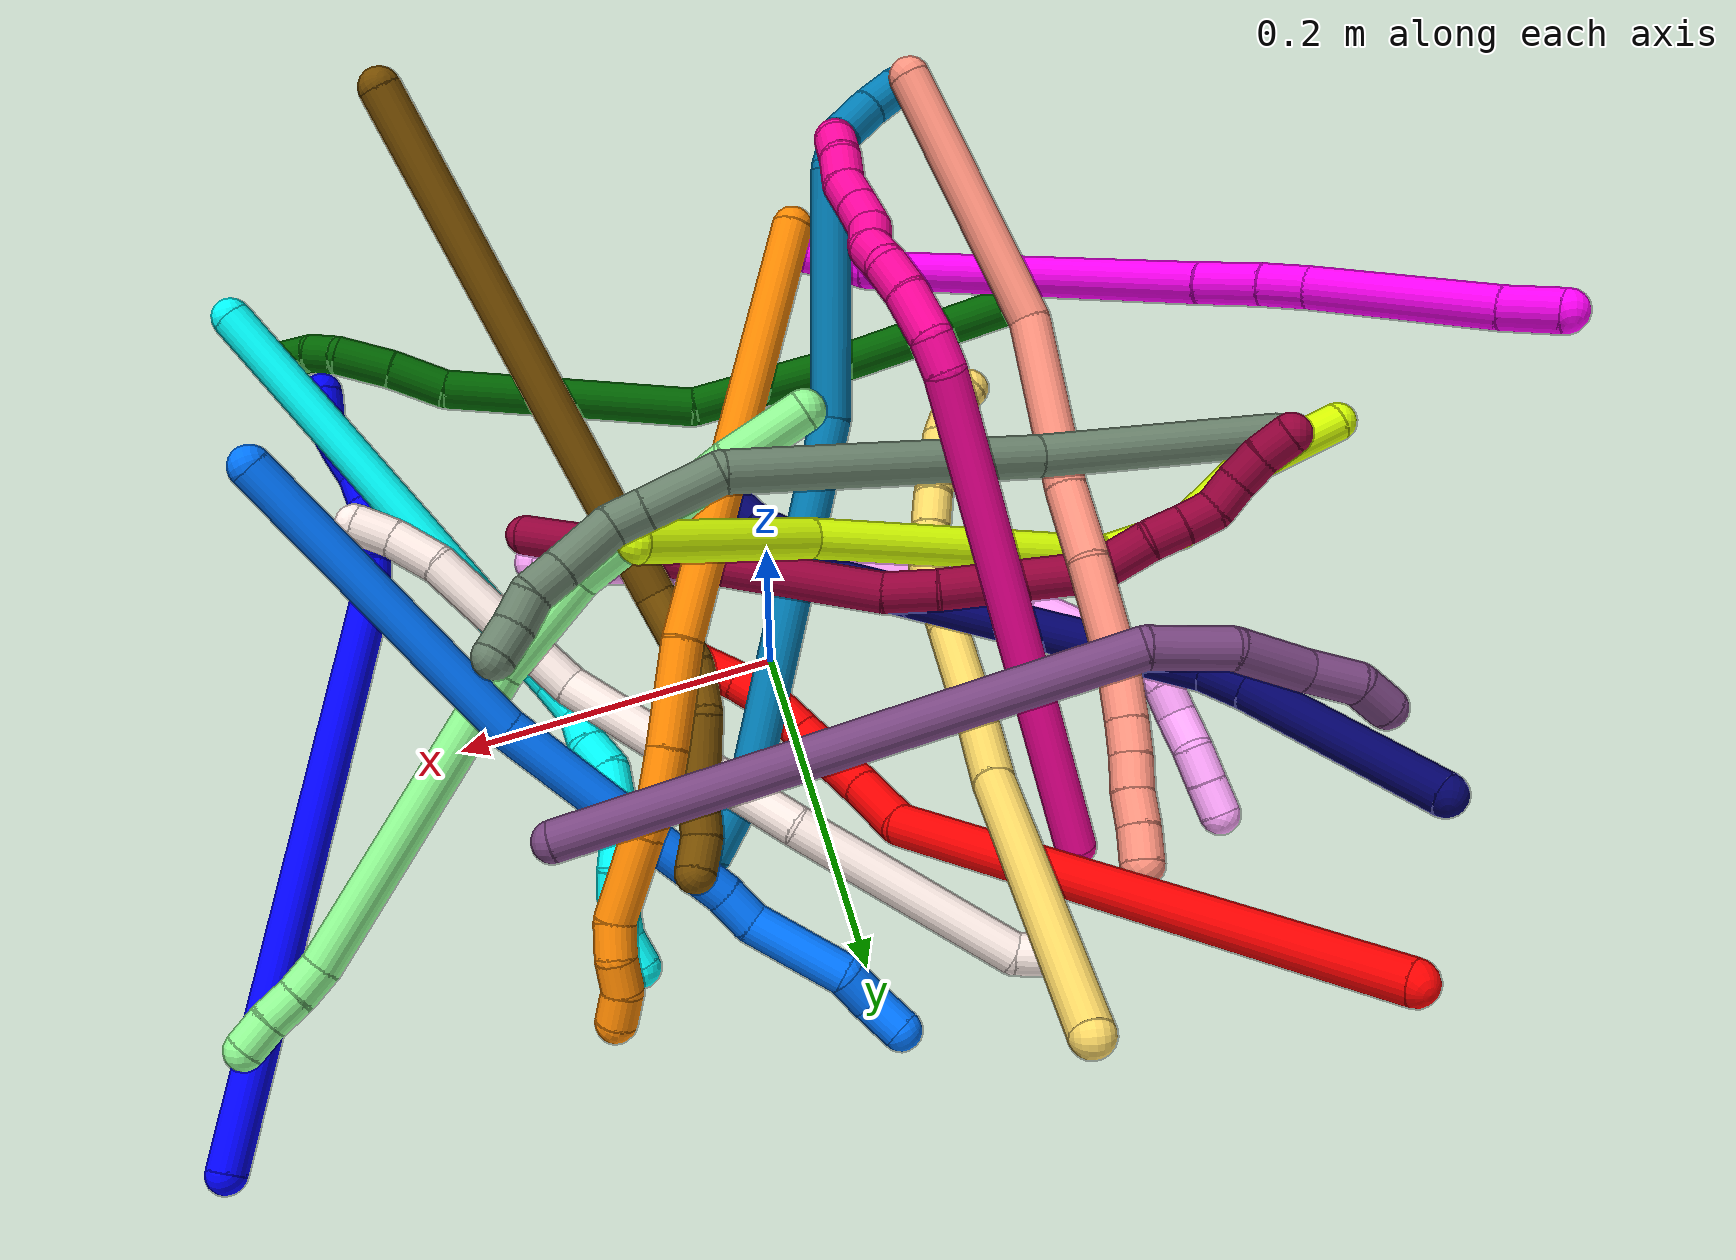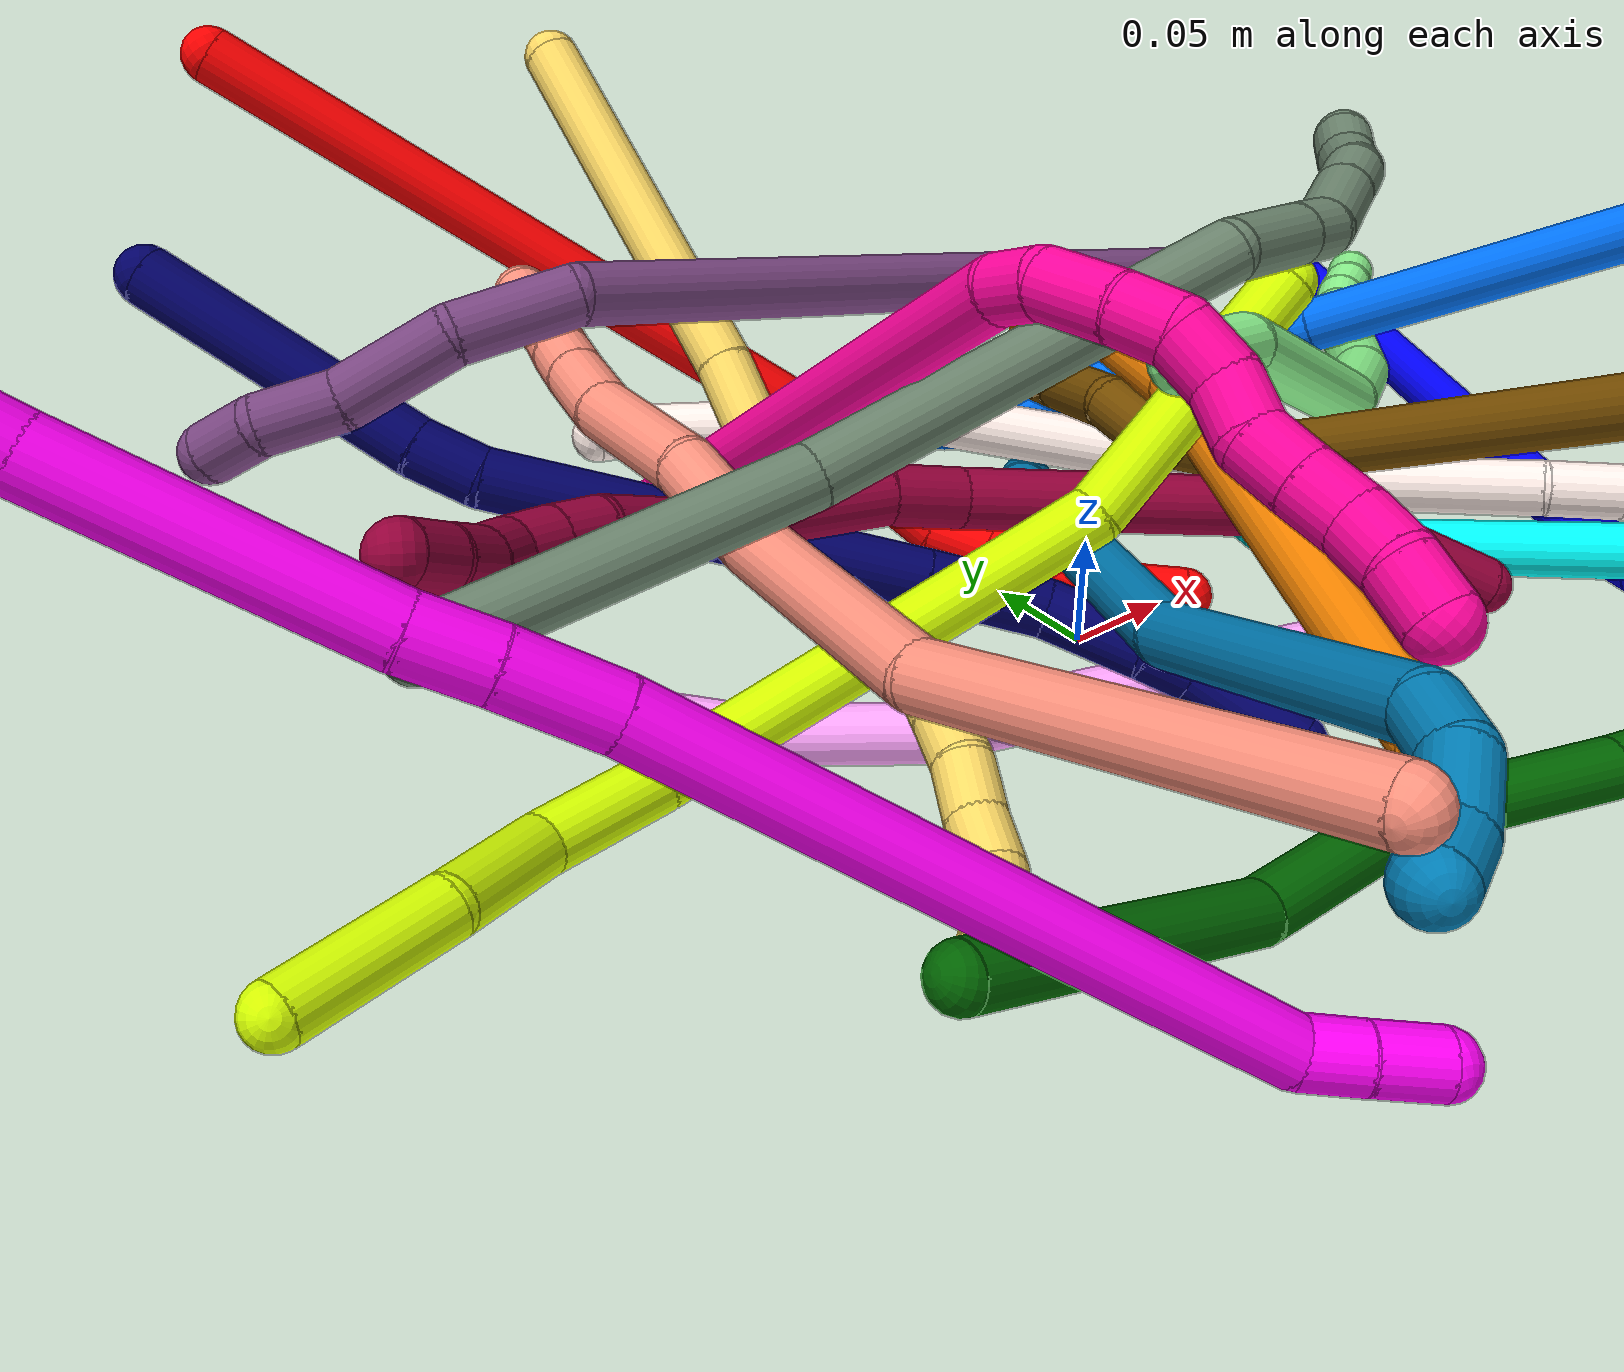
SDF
<sdf version="1.7">
 <world name="default">
  <plugin name="TubeGeneratorPlugin" filename="libtube_generator_plugin.so"/>
  <model name="photoneo_s_sensor">
   <static>1</static>
   <pose>0 0 2 1.57079 1.57079 3.14159</pose>
   <link name="link">
    <inertial><mass>0.1</mass></inertial>
    <sensor name="sensor" type="depth">
     <update_rate>30</update_rate>
     <camera>
      <horizontal_fov>1.22</horizontal_fov>
      <image><width>1920</width><height>1200</height><format>B8G8R8</format></image>
      <clip><near>0.1</near><far>4</far></clip>
      <depth_camera><output>points</output></depth_camera>
     </camera>
     <plugin name="camera_plugin" filename="libgazebo_ros_depth_camera.so">
      <baseline>0.2</baseline>
      <alwaysOn>1</alwaysOn>
      <updateRate>0.0</updateRate>
      <cameraName>camera_ir</cameraName>
      <imageTopicName>/camera/color/image_raw</imageTopicName>
      <cameraInfoTopicName>/camera/color/camera_info</cameraInfoTopicName>
      <depthImageTopicName>/camera/depth/image_raw</depthImageTopicName>
      <depthImageCameraInfoTopicName>/camera/depth/camera_info</depthImageCameraInfoTopicName>
      <pointCloudTopicName>/camera/depth/points</pointCloudTopicName>
      <frameName>fr_optical</frameName>
      <pointCloudCutoff>0.1</pointCloudCutoff>
      <pointCloudCutoffMax>2.0</pointCloudCutoffMax>
      <distortionK1>0</distortionK1>
      <distortionK2>0</distortionK2>
      <distortionK3>0</distortionK3>
      <distortionT1>0</distortionT1>
      <distortionT2>0</distortionT2>
      <CxPrime>0</CxPrime>
      <Cx>0</Cx>
      <Cy>0</Cy>
      <focalLength>0</focalLength>
      <hackBaseline>0</hackBaseline>
     </plugin>
    </sensor>
   </link>
  </model>
  <gravity>0 0 -9.8</gravity>
  <magnetic_field>6e-06 2.3e-05 -4.2e-05</magnetic_field>
  <atmosphere type="adiabatic"/>
  <physics name="default_physics" default="0" type="ode">
   <max_step_size>0.003</max_step_size>
   <real_time_factor>1</real_time_factor>
   <real_time_update_rate>1000</real_time_update_rate>
   <max_contacts>10000</max_contacts>
   <ode>
    <solver>
     <type>quick</type>
     <iters>100</iters>
     <sor>1.3</sor>
     <use_dynamic_moi_rescaling>0</use_dynamic_moi_rescaling>
    </solver>
    <constraints>
     <contact_max_correcting_vel>0</contact_max_correcting_vel>
     <contact_surface_layer>0.001</contact_surface_layer>
     <cfm>0</cfm>
     <erp>0.2</erp>
    </constraints>
   </ode>
  </physics>
  <scene><ambient>0.4 0.4 0.4 1</ambient><background>0.7 0.7 0.7 1</background><shadows>0</shadows></scene>
  <audio><device>default</device></audio>
  <spherical_coordinates>
   <surface_model>EARTH_WGS84</surface_model>
   <latitude_deg>0</latitude_deg>
   <longitude_deg>0</longitude_deg>
   <elevation>0</elevation>
   <heading_deg>0</heading_deg>
  </spherical_coordinates>
  <model name="bin">
   <static>1</static>
   <link name="bottom">
    <collision name="collision-bottom">
     <pose>0 0 -0.01 0 -0 0</pose>
     <geometry><box><size>0.8 0.6 0.02</size></box></geometry>
     <surface>
      <friction><ode><mu>100</mu><mu2>100</mu2></ode></friction>
      <contact><collide_bitmask>65535</collide_bitmask></contact>
     </surface>
    </collision>
   </link>
   <link name="west_wall">
    <collision name="collision-west_wall">
     <pose>-0.41 0 0.1 0 -0 0</pose>
     <geometry><box><size>0.02 0.6 0.2</size></box></geometry>
     <surface>
      <friction><ode><mu>100</mu><mu2>100</mu2></ode></friction>
      <contact><collide_bitmask>65535</collide_bitmask></contact>
     </surface>
    </collision>
   </link>
   <link name="east_wall">
    <collision name="collision-east_wall">
     <pose>0.41 0 0.1 0 -0 0</pose>
     <geometry><box><size>0.02 0.6 0.2</size></box></geometry>
     <surface>
      <friction><ode><mu>100</mu><mu2>100</mu2></ode></friction>
      <contact><collide_bitmask>65535</collide_bitmask></contact>
     </surface>
    </collision>
   </link>
   <link name="south_wall">
    <collision name="collision-south_wall">
     <pose>0 -0.31 0.1 0 -0 0</pose>
     <geometry><box><size>0.8 0.02 0.2</size></box></geometry>
     <surface>
      <friction><ode><mu>100</mu><mu2>100</mu2></ode></friction>
      <contact><collide_bitmask>65535</collide_bitmask></contact>
     </surface>
    </collision>
   </link>
   <link name="north_wall">
    <collision name="collision-north_wall">
     <pose>0 0.31 0.1 0 -0 0</pose>
     <geometry><box><size>0.8 0.02 0.2</size></box></geometry>
     <surface>
      <friction><ode><mu>100</mu><mu2>100</mu2></ode></friction>
      <contact><collide_bitmask>65535</collide_bitmask></contact>
     </surface>
    </collision>
   </link>
  </model>
  <model name="1">
   <static>0</static>
   <link name="1">
    <collision name="collision-cylinder-e_1_1_4">
     <pose>0.017924 -0.159601 -0.075649 2.01342 0.101137 0.159657</pose>
     <geometry><cylinder><radius>0.0125</radius><length>0.355057</length></cylinder></geometry>
     <surface>
      <friction><ode><mu>1.16</mu><mu2>1.16</mu2><slip1>0</slip1><slip2>0</slip2></ode></friction>
      <contact><ode><kp>1e+06</kp><kd>1</kd><max_vel>0</max_vel><min_depth>0.001</min_depth></ode></contact>
     </surface>
    </collision>
    <visual name="visual-cylinder-e_1_1_4">
     <pose>0.017924 -0.159601 -0.075649 2.01342 0.101137 0.159657</pose>
     <geometry><cylinder><radius>0.0125</radius><length>0.355057</length></cylinder></geometry>
     <material><ambient>0 0 1 1</ambient></material>
    </visual>
    <collision name="collision-cylinder-e_2_4_5">
     <pose>0.034107 -0.328337 -0.156055 2.05093 -0.167442 -0.274892</pose>
     <geometry><cylinder><radius>0.0125</radius><length>0.020891</length></cylinder></geometry>
     <surface>
      <friction><ode><mu>1.16</mu><mu2>1.16</mu2><slip1>0</slip1><slip2>0</slip2></ode></friction>
      <contact><ode><kp>1e+06</kp><kd>1</kd><max_vel>0</max_vel><min_depth>0.001</min_depth></ode></contact>
     </surface>
    </collision>
    <visual name="visual-cylinder-e_2_4_5">
     <pose>0.034107 -0.328337 -0.156055 2.05093 -0.167442 -0.274892</pose>
     <geometry><cylinder><radius>0.0125</radius><length>0.020891</length></cylinder></geometry>
     <material><ambient>0 0 1 1</ambient></material>
    </visual>
    <collision name="collision-cylinder-e_3_5_6">
     <pose>0.030085 -0.347567 -0.165247 1.98472 -0.204048 -0.311065</pose>
     <geometry><cylinder><radius>0.0125</radius><length>0.022521</length></cylinder></geometry>
     <surface>
      <friction><ode><mu>1.16</mu><mu2>1.16</mu2><slip1>0</slip1><slip2>0</slip2></ode></friction>
      <contact><ode><kp>1e+06</kp><kd>1</kd><max_vel>0</max_vel><min_depth>0.001</min_depth></ode></contact>
     </surface>
    </collision>
    <visual name="visual-cylinder-e_3_5_6">
     <pose>0.030085 -0.347567 -0.165247 1.98472 -0.204048 -0.311065</pose>
     <geometry><cylinder><radius>0.0125</radius><length>0.022521</length></cylinder></geometry>
     <material><ambient>0 0 1 1</ambient></material>
    </visual>
    <collision name="collision-cylinder-e_4_6_7">
     <pose>0.025389 -0.366908 -0.172884 1.90421 -0.24194 -0.338239</pose>
     <geometry><cylinder><radius>0.0125</radius><length>0.020154</length></cylinder></geometry>
     <surface>
      <friction><ode><mu>1.16</mu><mu2>1.16</mu2><slip1>0</slip1><slip2>0</slip2></ode></friction>
      <contact><ode><kp>1e+06</kp><kd>1</kd><max_vel>0</max_vel><min_depth>0.001</min_depth></ode></contact>
     </surface>
    </collision>
    <visual name="visual-cylinder-e_4_6_7">
     <pose>0.025389 -0.366908 -0.172884 1.90421 -0.24194 -0.338239</pose>
     <geometry><cylinder><radius>0.0125</radius><length>0.020154</length></cylinder></geometry>
     <material><ambient>0 0 1 1</ambient></material>
    </visual>
    <collision name="collision-cylinder-e_5_7_8">
     <pose>0.018314 -0.384344 -0.18056 2.07064 -0.46309 -0.75652</pose>
     <geometry><cylinder><radius>0.0125</radius><length>0.020864</length></cylinder></geometry>
     <surface>
      <friction><ode><mu>1.16</mu><mu2>1.16</mu2><slip1>0</slip1><slip2>0</slip2></ode></friction>
      <contact><ode><kp>1e+06</kp><kd>1</kd><max_vel>0</max_vel><min_depth>0.001</min_depth></ode></contact>
     </surface>
    </collision>
    <visual name="visual-cylinder-e_5_7_8">
     <pose>0.018314 -0.384344 -0.18056 2.07064 -0.46309 -0.75652</pose>
     <geometry><cylinder><radius>0.0125</radius><length>0.020864</length></cylinder></geometry>
     <material><ambient>0 0 1 1</ambient></material>
    </visual>
    <collision name="collision-cylinder-e_6_8_9">
     <pose>0.008273 -0.397789 -0.191763 2.47877 -0.562344 -1.39656</pose>
     <geometry><cylinder><radius>0.0125</radius><length>0.020184</length></cylinder></geometry>
     <surface>
      <friction><ode><mu>1.16</mu><mu2>1.16</mu2><slip1>0</slip1><slip2>0</slip2></ode></friction>
      <contact><ode><kp>1e+06</kp><kd>1</kd><max_vel>0</max_vel><min_depth>0.001</min_depth></ode></contact>
     </surface>
    </collision>
    <visual name="visual-cylinder-e_6_8_9">
     <pose>0.008273 -0.397789 -0.191763 2.47877 -0.562344 -1.39656</pose>
     <geometry><cylinder><radius>0.0125</radius><length>0.020184</length></cylinder></geometry>
     <material><ambient>0 0 1 1</ambient></material>
    </visual>
    <collision name="collision-cylinder-e_7_9_10">
     <pose>-0.001484 -0.407873 -0.206247 2.58448 -0.446725 -1.34247</pose>
     <geometry><cylinder><radius>0.0125</radius><length>0.020259</length></cylinder></geometry>
     <surface>
      <friction><ode><mu>1.16</mu><mu2>1.16</mu2><slip1>0</slip1><slip2>0</slip2></ode></friction>
      <contact><ode><kp>1e+06</kp><kd>1</kd><max_vel>0</max_vel><min_depth>0.001</min_depth></ode></contact>
     </surface>
    </collision>
    <visual name="visual-cylinder-e_7_9_10">
     <pose>-0.001484 -0.407873 -0.206247 2.58448 -0.446725 -1.34247</pose>
     <geometry><cylinder><radius>0.0125</radius><length>0.020259</length></cylinder></geometry>
     <material><ambient>0 0 1 1</ambient></material>
    </visual>
    <collision name="collision-cylinder-e_8_10_2">
     <pose>-0.007746 -0.420894 -0.219484 2.16067 -0.189071 -0.351475</pose>
     <geometry><cylinder><radius>0.0125</radius><length>0.020069</length></cylinder></geometry>
     <surface>
      <friction><ode><mu>1.16</mu><mu2>1.16</mu2><slip1>0</slip1><slip2>0</slip2></ode></friction>
      <contact><ode><kp>1e+06</kp><kd>1</kd><max_vel>0</max_vel><min_depth>0.001</min_depth></ode></contact>
     </surface>
    </collision>
    <visual name="visual-cylinder-e_8_10_2">
     <pose>-0.007746 -0.420894 -0.219484 2.16067 -0.189071 -0.351475</pose>
     <geometry><cylinder><radius>0.0125</radius><length>0.020069</length></cylinder></geometry>
     <material><ambient>0 0 1 1</ambient></material>
    </visual>
    <collision name="collision-sphere-2">
     <pose>-0.009632 -0.429084 -0.224966 0 -0 0</pose>
     <geometry><sphere><radius>0.0125</radius></sphere></geometry>
     <surface>
      <friction><ode><mu>1.16</mu><mu2>1.16</mu2><slip1>0</slip1><slip2>0</slip2></ode></friction>
      <contact><ode><kp>1e+06</kp><kd>1</kd><max_vel>0</max_vel><min_depth>0.001</min_depth></ode></contact>
     </surface>
    </collision>
    <visual name="visual-sphere-2">
     <pose>-0.009632 -0.429084 -0.224966 0 -0 0</pose>
     <geometry><sphere><radius>0.0125</radius></sphere></geometry>
     <material><ambient>0 0 1 1</ambient></material>
    </visual>
    <collision name="collision-sphere-10">
     <pose>-0.00586 -0.412704 -0.214001 0 -0 0</pose>
     <geometry><sphere><radius>0.0125</radius></sphere></geometry>
     <surface>
      <friction><ode><mu>1.16</mu><mu2>1.16</mu2><slip1>0</slip1><slip2>0</slip2></ode></friction>
      <contact><ode><kp>1e+06</kp><kd>1</kd><max_vel>0</max_vel><min_depth>0.001</min_depth></ode></contact>
     </surface>
    </collision>
    <visual name="visual-sphere-10">
     <pose>-0.00586 -0.412704 -0.214001 0 -0 0</pose>
     <geometry><sphere><radius>0.0125</radius></sphere></geometry>
     <material><ambient>0 0 1 1</ambient></material>
    </visual>
    <collision name="collision-sphere-9">
     <pose>0.002893 -0.403043 -0.198493 0 -0 0</pose>
     <geometry><sphere><radius>0.0125</radius></sphere></geometry>
     <surface>
      <friction><ode><mu>1.16</mu><mu2>1.16</mu2><slip1>0</slip1><slip2>0</slip2></ode></friction>
      <contact><ode><kp>1e+06</kp><kd>1</kd><max_vel>0</max_vel><min_depth>0.001</min_depth></ode></contact>
     </surface>
    </collision>
    <visual name="visual-sphere-9">
     <pose>0.002893 -0.403043 -0.198493 0 -0 0</pose>
     <geometry><sphere><radius>0.0125</radius></sphere></geometry>
     <material><ambient>0 0 1 1</ambient></material>
    </visual>
    <collision name="collision-sphere-4">
     <pose>0.035848 -0.319202 -0.151297 0 -0 0</pose>
     <geometry><sphere><radius>0.0125</radius></sphere></geometry>
     <surface>
      <friction><ode><mu>1.16</mu><mu2>1.16</mu2><slip1>0</slip1><slip2>0</slip2></ode></friction>
      <contact><ode><kp>1e+06</kp><kd>1</kd><max_vel>0</max_vel><min_depth>0.001</min_depth></ode></contact>
     </surface>
    </collision>
    <visual name="visual-sphere-4">
     <pose>0.035848 -0.319202 -0.151297 0 -0 0</pose>
     <geometry><sphere><radius>0.0125</radius></sphere></geometry>
     <material><ambient>0 0 1 1</ambient></material>
    </visual>
    <collision name="collision-sphere-1">
     <geometry><sphere><radius>0.0125</radius></sphere></geometry>
     <surface>
      <friction><ode><mu>1.16</mu><mu2>1.16</mu2><slip1>0</slip1><slip2>0</slip2></ode></friction>
      <contact><ode><kp>1e+06</kp><kd>1</kd><max_vel>0</max_vel><min_depth>0.001</min_depth></ode></contact>
     </surface>
    </collision>
    <visual name="visual-sphere-1">
     <geometry><sphere><radius>0.0125</radius></sphere></geometry>
     <material><ambient>0 0 1 1</ambient></material>
    </visual>
    <collision name="collision-sphere-8">
     <pose>0.013654 -0.392536 -0.185033 0 -0 0</pose>
     <geometry><sphere><radius>0.0125</radius></sphere></geometry>
     <surface>
      <friction><ode><mu>1.16</mu><mu2>1.16</mu2><slip1>0</slip1><slip2>0</slip2></ode></friction>
      <contact><ode><kp>1e+06</kp><kd>1</kd><max_vel>0</max_vel><min_depth>0.001</min_depth></ode></contact>
     </surface>
    </collision>
    <visual name="visual-sphere-8">
     <pose>0.013654 -0.392536 -0.185033 0 -0 0</pose>
     <geometry><sphere><radius>0.0125</radius></sphere></geometry>
     <material><ambient>0 0 1 1</ambient></material>
    </visual>
    <collision name="collision-sphere-5">
     <pose>0.032367 -0.337472 -0.160812 0 -0 0</pose>
     <geometry><sphere><radius>0.0125</radius></sphere></geometry>
     <surface>
      <friction><ode><mu>1.16</mu><mu2>1.16</mu2><slip1>0</slip1><slip2>0</slip2></ode></friction>
      <contact><ode><kp>1e+06</kp><kd>1</kd><max_vel>0</max_vel><min_depth>0.001</min_depth></ode></contact>
     </surface>
    </collision>
    <visual name="visual-sphere-5">
     <pose>0.032367 -0.337472 -0.160812 0 -0 0</pose>
     <geometry><sphere><radius>0.0125</radius></sphere></geometry>
     <material><ambient>0 0 1 1</ambient></material>
    </visual>
    <collision name="collision-sphere-6">
     <pose>0.027803 -0.357663 -0.169682 0 -0 0</pose>
     <geometry><sphere><radius>0.0125</radius></sphere></geometry>
     <surface>
      <friction><ode><mu>1.16</mu><mu2>1.16</mu2><slip1>0</slip1><slip2>0</slip2></ode></friction>
      <contact><ode><kp>1e+06</kp><kd>1</kd><max_vel>0</max_vel><min_depth>0.001</min_depth></ode></contact>
     </surface>
    </collision>
    <visual name="visual-sphere-6">
     <pose>0.027803 -0.357663 -0.169682 0 -0 0</pose>
     <geometry><sphere><radius>0.0125</radius></sphere></geometry>
     <material><ambient>0 0 1 1</ambient></material>
    </visual>
    <collision name="collision-sphere-7">
     <pose>0.022974 -0.376152 -0.176086 0 -0 0</pose>
     <geometry><sphere><radius>0.0125</radius></sphere></geometry>
     <surface>
      <friction><ode><mu>1.16</mu><mu2>1.16</mu2><slip1>0</slip1><slip2>0</slip2></ode></friction>
      <contact><ode><kp>1e+06</kp><kd>1</kd><max_vel>0</max_vel><min_depth>0.001</min_depth></ode></contact>
     </surface>
    </collision>
    <visual name="visual-sphere-7">
     <pose>0.022974 -0.376152 -0.176086 0 -0 0</pose>
     <geometry><sphere><radius>0.0125</radius></sphere></geometry>
     <material><ambient>0 0 1 1</ambient></material>
    </visual>
    <inertial>
     <pose>0.017259 -0.223014 -0.107093 0 -0 0</pose>
     <mass>0.5</mass>
     <inertia>
      <ixx>0.004271</ixx>
      <ixy>0</ixy>
      <ixz>0</ixz>
      <iyy>-0.000978</iyy>
      <iyz>0</iyz>
      <izz>0.002982</izz>
     </inertia>
    </inertial>
   </link>
   <pose>0.388076 0.206232 0.011498 2.69488 -0.195207 2.77231</pose>
  </model>
  <model name="2">
   <static>0</static>
   <link name="2">
    <collision name="collision-cylinder-e_1_1_4">
     <pose>0.056912 -0.052504 -0.1352 2.77117 0.373935 1.58046</pose>
     <geometry><cylinder><radius>0.0125</radius><length>0.311606</length></cylinder></geometry>
     <surface>
      <friction><ode><mu>1.16</mu><mu2>1.16</mu2><slip1>0</slip1><slip2>0</slip2></ode></friction>
      <contact><ode><kp>1e+06</kp><kd>1</kd><max_vel>0</max_vel><min_depth>0.001</min_depth></ode></contact>
     </surface>
    </collision>
    <visual name="visual-cylinder-e_1_1_4">
     <pose>0.056912 -0.052504 -0.1352 2.77117 0.373935 1.58046</pose>
     <geometry><cylinder><radius>0.0125</radius><length>0.311606</length></cylinder></geometry>
     <material><ambient>1 0 0 1</ambient></material>
    </visual>
    <collision name="collision-cylinder-e_2_4_5">
     <pose>0.113718 -0.1092 -0.290119 2.93216 -0.00525 -0.049944</pose>
     <geometry><cylinder><radius>0.0125</radius><length>0.04032</length></cylinder></geometry>
     <surface>
      <friction><ode><mu>1.16</mu><mu2>1.16</mu2><slip1>0</slip1><slip2>0</slip2></ode></friction>
      <contact><ode><kp>1e+06</kp><kd>1</kd><max_vel>0</max_vel><min_depth>0.001</min_depth></ode></contact>
     </surface>
    </collision>
    <visual name="visual-cylinder-e_2_4_5">
     <pose>0.113718 -0.1092 -0.290119 2.93216 -0.00525 -0.049944</pose>
     <geometry><cylinder><radius>0.0125</radius><length>0.04032</length></cylinder></geometry>
     <material><ambient>1 0 0 1</ambient></material>
    </visual>
    <collision name="collision-cylinder-e_3_5_6">
     <pose>0.113702 -0.118371 -0.324545 2.81514 0.00579 0.035154</pose>
     <geometry><cylinder><radius>0.0125</radius><length>0.031054</length></cylinder></geometry>
     <surface>
      <friction><ode><mu>1.16</mu><mu2>1.16</mu2><slip1>0</slip1><slip2>0</slip2></ode></friction>
      <contact><ode><kp>1e+06</kp><kd>1</kd><max_vel>0</max_vel><min_depth>0.001</min_depth></ode></contact>
     </surface>
    </collision>
    <visual name="visual-cylinder-e_3_5_6">
     <pose>0.113702 -0.118371 -0.324545 2.81514 0.00579 0.035154</pose>
     <geometry><cylinder><radius>0.0125</radius><length>0.031054</length></cylinder></geometry>
     <material><ambient>1 0 0 1</ambient></material>
    </visual>
    <collision name="collision-cylinder-e_4_6_7">
     <pose>0.113038 -0.131911 -0.349971 2.46769 -0.054934 -0.156535</pose>
     <geometry><cylinder><radius>0.0125</radius><length>0.027479</length></cylinder></geometry>
     <surface>
      <friction><ode><mu>1.16</mu><mu2>1.16</mu2><slip1>0</slip1><slip2>0</slip2></ode></friction>
      <contact><ode><kp>1e+06</kp><kd>1</kd><max_vel>0</max_vel><min_depth>0.001</min_depth></ode></contact>
     </surface>
    </collision>
    <visual name="visual-cylinder-e_4_6_7">
     <pose>0.113038 -0.131911 -0.349971 2.46769 -0.054934 -0.156535</pose>
     <geometry><cylinder><radius>0.0125</radius><length>0.027479</length></cylinder></geometry>
     <material><ambient>1 0 0 1</ambient></material>
    </visual>
    <collision name="collision-cylinder-e_5_7_8">
     <pose>0.111442 -0.149664 -0.372385 2.47542 -0.056488 -0.162954</pose>
     <geometry><cylinder><radius>0.0125</radius><length>0.029795</length></cylinder></geometry>
     <surface>
      <friction><ode><mu>1.16</mu><mu2>1.16</mu2><slip1>0</slip1><slip2>0</slip2></ode></friction>
      <contact><ode><kp>1e+06</kp><kd>1</kd><max_vel>0</max_vel><min_depth>0.001</min_depth></ode></contact>
     </surface>
    </collision>
    <visual name="visual-cylinder-e_5_7_8">
     <pose>0.111442 -0.149664 -0.372385 2.47542 -0.056488 -0.162954</pose>
     <geometry><cylinder><radius>0.0125</radius><length>0.029795</length></cylinder></geometry>
     <material><ambient>1 0 0 1</ambient></material>
    </visual>
    <collision name="collision-cylinder-e_6_8_9">
     <pose>0.112231 -0.166586 -0.393238 2.44061 0.135182 0.366188</pose>
     <geometry><cylinder><radius>0.0125</radius><length>0.024192</length></cylinder></geometry>
     <surface>
      <friction><ode><mu>1.16</mu><mu2>1.16</mu2><slip1>0</slip1><slip2>0</slip2></ode></friction>
      <contact><ode><kp>1e+06</kp><kd>1</kd><max_vel>0</max_vel><min_depth>0.001</min_depth></ode></contact>
     </surface>
    </collision>
    <visual name="visual-cylinder-e_6_8_9">
     <pose>0.112231 -0.166586 -0.393238 2.44061 0.135182 0.366188</pose>
     <geometry><cylinder><radius>0.0125</radius><length>0.024192</length></cylinder></geometry>
     <material><ambient>1 0 0 1</ambient></material>
    </visual>
    <collision name="collision-cylinder-e_7_9_2">
     <pose>0.117793 -0.187781 -0.413317 2.25217 0.223019 0.461567</pose>
     <geometry><cylinder><radius>0.0125</radius><length>0.035553</length></cylinder></geometry>
     <surface>
      <friction><ode><mu>1.16</mu><mu2>1.16</mu2><slip1>0</slip1><slip2>0</slip2></ode></friction>
      <contact><ode><kp>1e+06</kp><kd>1</kd><max_vel>0</max_vel><min_depth>0.001</min_depth></ode></contact>
     </surface>
    </collision>
    <visual name="visual-cylinder-e_7_9_2">
     <pose>0.117793 -0.187781 -0.413317 2.25217 0.223019 0.461567</pose>
     <geometry><cylinder><radius>0.0125</radius><length>0.035553</length></cylinder></geometry>
     <material><ambient>1 0 0 1</ambient></material>
    </visual>
    <collision name="collision-sphere-2">
     <pose>0.121725 -0.201246 -0.424237 0 -0 0</pose>
     <geometry><sphere><radius>0.0125</radius></sphere></geometry>
     <surface>
      <friction><ode><mu>1.16</mu><mu2>1.16</mu2><slip1>0</slip1><slip2>0</slip2></ode></friction>
      <contact><ode><kp>1e+06</kp><kd>1</kd><max_vel>0</max_vel><min_depth>0.001</min_depth></ode></contact>
     </surface>
    </collision>
    <visual name="visual-sphere-2">
     <pose>0.121725 -0.201246 -0.424237 0 -0 0</pose>
     <geometry><sphere><radius>0.0125</radius></sphere></geometry>
     <material><ambient>1 0 0 1</ambient></material>
    </visual>
    <collision name="collision-sphere-9">
     <pose>0.113862 -0.174316 -0.402397 0 -0 0</pose>
     <geometry><sphere><radius>0.0125</radius></sphere></geometry>
     <surface>
      <friction><ode><mu>1.16</mu><mu2>1.16</mu2><slip1>0</slip1><slip2>0</slip2></ode></friction>
      <contact><ode><kp>1e+06</kp><kd>1</kd><max_vel>0</max_vel><min_depth>0.001</min_depth></ode></contact>
     </surface>
    </collision>
    <visual name="visual-sphere-9">
     <pose>0.113862 -0.174316 -0.402397 0 -0 0</pose>
     <geometry><sphere><radius>0.0125</radius></sphere></geometry>
     <material><ambient>1 0 0 1</ambient></material>
    </visual>
    <collision name="collision-sphere-4">
     <pose>0.113824 -0.105009 -0.270399 0 -0 0</pose>
     <geometry><sphere><radius>0.0125</radius></sphere></geometry>
     <surface>
      <friction><ode><mu>1.16</mu><mu2>1.16</mu2><slip1>0</slip1><slip2>0</slip2></ode></friction>
      <contact><ode><kp>1e+06</kp><kd>1</kd><max_vel>0</max_vel><min_depth>0.001</min_depth></ode></contact>
     </surface>
    </collision>
    <visual name="visual-sphere-4">
     <pose>0.113824 -0.105009 -0.270399 0 -0 0</pose>
     <geometry><sphere><radius>0.0125</radius></sphere></geometry>
     <material><ambient>1 0 0 1</ambient></material>
    </visual>
    <collision name="collision-sphere-1">
     <geometry><sphere><radius>0.0125</radius></sphere></geometry>
     <surface>
      <friction><ode><mu>1.16</mu><mu2>1.16</mu2><slip1>0</slip1><slip2>0</slip2></ode></friction>
      <contact><ode><kp>1e+06</kp><kd>1</kd><max_vel>0</max_vel><min_depth>0.001</min_depth></ode></contact>
     </surface>
    </collision>
    <visual name="visual-sphere-1">
     <geometry><sphere><radius>0.0125</radius></sphere></geometry>
     <material><ambient>1 0 0 1</ambient></material>
    </visual>
    <collision name="collision-sphere-8">
     <pose>0.110601 -0.158855 -0.384078 0 -0 0</pose>
     <geometry><sphere><radius>0.0125</radius></sphere></geometry>
     <surface>
      <friction><ode><mu>1.16</mu><mu2>1.16</mu2><slip1>0</slip1><slip2>0</slip2></ode></friction>
      <contact><ode><kp>1e+06</kp><kd>1</kd><max_vel>0</max_vel><min_depth>0.001</min_depth></ode></contact>
     </surface>
    </collision>
    <visual name="visual-sphere-8">
     <pose>0.110601 -0.158855 -0.384078 0 -0 0</pose>
     <geometry><sphere><radius>0.0125</radius></sphere></geometry>
     <material><ambient>1 0 0 1</ambient></material>
    </visual>
    <collision name="collision-sphere-5">
     <pose>0.113612 -0.113391 -0.309838 0 -0 0</pose>
     <geometry><sphere><radius>0.0125</radius></sphere></geometry>
     <surface>
      <friction><ode><mu>1.16</mu><mu2>1.16</mu2><slip1>0</slip1><slip2>0</slip2></ode></friction>
      <contact><ode><kp>1e+06</kp><kd>1</kd><max_vel>0</max_vel><min_depth>0.001</min_depth></ode></contact>
     </surface>
    </collision>
    <visual name="visual-sphere-5">
     <pose>0.113612 -0.113391 -0.309838 0 -0 0</pose>
     <geometry><sphere><radius>0.0125</radius></sphere></geometry>
     <material><ambient>1 0 0 1</ambient></material>
    </visual>
    <collision name="collision-sphere-6">
     <pose>0.113792 -0.12335 -0.339251 0 -0 0</pose>
     <geometry><sphere><radius>0.0125</radius></sphere></geometry>
     <surface>
      <friction><ode><mu>1.16</mu><mu2>1.16</mu2><slip1>0</slip1><slip2>0</slip2></ode></friction>
      <contact><ode><kp>1e+06</kp><kd>1</kd><max_vel>0</max_vel><min_depth>0.001</min_depth></ode></contact>
     </surface>
    </collision>
    <visual name="visual-sphere-6">
     <pose>0.113792 -0.12335 -0.339251 0 -0 0</pose>
     <geometry><sphere><radius>0.0125</radius></sphere></geometry>
     <material><ambient>1 0 0 1</ambient></material>
    </visual>
    <collision name="collision-sphere-7">
     <pose>0.112283 -0.140472 -0.360691 0 -0 0</pose>
     <geometry><sphere><radius>0.0125</radius></sphere></geometry>
     <surface>
      <friction><ode><mu>1.16</mu><mu2>1.16</mu2><slip1>0</slip1><slip2>0</slip2></ode></friction>
      <contact><ode><kp>1e+06</kp><kd>1</kd><max_vel>0</max_vel><min_depth>0.001</min_depth></ode></contact>
     </surface>
    </collision>
    <visual name="visual-sphere-7">
     <pose>0.112283 -0.140472 -0.360691 0 -0 0</pose>
     <geometry><sphere><radius>0.0125</radius></sphere></geometry>
     <material><ambient>1 0 0 1</ambient></material>
    </visual>
    <inertial>
     <pose>0.07836 -0.08646 -0.21765 0 -0 0</pose>
     <mass>0.5</mass>
     <inertia>
      <ixx>0.00237</ixx>
      <ixy>0</ixy>
      <ixz>0</ixz>
      <iyy>0.002683</iyy>
      <iyz>0</iyz>
      <izz>-9.4e-05</izz>
     </inertia>
    </inertial>
   </link>
   <pose>-0.23195 0.314606 0.229115 -0.716888 0.343386 0.58934</pose>
  </model>
  <model name="3">
   <static>0</static>
   <link name="3">
    <collision name="collision-cylinder-e_1_1_4">
     <pose>-0.061737 0.026901 -0.135378 -2.94543 -0.420601 2.27773</pose>
     <geometry><cylinder><radius>0.0125</radius><length>0.302406</length></cylinder></geometry>
     <surface>
      <friction><ode><mu>1.16</mu><mu2>1.16</mu2><slip1>0</slip1><slip2>0</slip2></ode></friction>
      <contact><ode><kp>1e+06</kp><kd>1</kd><max_vel>0</max_vel><min_depth>0.001</min_depth></ode></contact>
     </surface>
    </collision>
    <visual name="visual-cylinder-e_1_1_4">
     <pose>-0.061737 0.026901 -0.135378 -2.94543 -0.420601 2.27773</pose>
     <geometry><cylinder><radius>0.0125</radius><length>0.302406</length></cylinder></geometry>
     <material><ambient>0.003922 1 0.996078 1</ambient></material>
    </visual>
    <collision name="collision-cylinder-e_2_4_5">
     <pose>-0.127552 0.059668 -0.282516 -2.67899 -0.300785 1.14347</pose>
     <geometry><cylinder><radius>0.0125</radius><length>0.027519</length></cylinder></geometry>
     <surface>
      <friction><ode><mu>1.16</mu><mu2>1.16</mu2><slip1>0</slip1><slip2>0</slip2></ode></friction>
      <contact><ode><kp>1e+06</kp><kd>1</kd><max_vel>0</max_vel><min_depth>0.001</min_depth></ode></contact>
     </surface>
    </collision>
    <visual name="visual-cylinder-e_2_4_5">
     <pose>-0.127552 0.059668 -0.282516 -2.67899 -0.300785 1.14347</pose>
     <geometry><cylinder><radius>0.0125</radius><length>0.027519</length></cylinder></geometry>
     <material><ambient>0.003922 1 0.996078 1</ambient></material>
    </visual>
    <collision name="collision-cylinder-e_3_5_6">
     <pose>-0.130274 0.07104 -0.303441 -2.60047 0.126007 -0.447296</pose>
     <geometry><cylinder><radius>0.0125</radius><length>0.021557</length></cylinder></geometry>
     <surface>
      <friction><ode><mu>1.16</mu><mu2>1.16</mu2><slip1>0</slip1><slip2>0</slip2></ode></friction>
      <contact><ode><kp>1e+06</kp><kd>1</kd><max_vel>0</max_vel><min_depth>0.001</min_depth></ode></contact>
     </surface>
    </collision>
    <visual name="visual-cylinder-e_3_5_6">
     <pose>-0.130274 0.07104 -0.303441 -2.60047 0.126007 -0.447296</pose>
     <geometry><cylinder><radius>0.0125</radius><length>0.021557</length></cylinder></geometry>
     <material><ambient>0.003922 1 0.996078 1</ambient></material>
    </visual>
    <collision name="collision-cylinder-e_4_6_7">
     <pose>-0.131926 0.08194 -0.321656 -2.60429 -0.278089 0.940589</pose>
     <geometry><cylinder><radius>0.0125</radius><length>0.021911</length></cylinder></geometry>
     <surface>
      <friction><ode><mu>1.16</mu><mu2>1.16</mu2><slip1>0</slip1><slip2>0</slip2></ode></friction>
      <contact><ode><kp>1e+06</kp><kd>1</kd><max_vel>0</max_vel><min_depth>0.001</min_depth></ode></contact>
     </surface>
    </collision>
    <visual name="visual-cylinder-e_4_6_7">
     <pose>-0.131926 0.08194 -0.321656 -2.60429 -0.278089 0.940589</pose>
     <geometry><cylinder><radius>0.0125</radius><length>0.021911</length></cylinder></geometry>
     <material><ambient>0.003922 1 0.996078 1</ambient></material>
    </visual>
    <collision name="collision-cylinder-e_5_7_8">
     <pose>-0.129969 0.098059 -0.350254 -2.63971 0.219076 -0.810546</pose>
     <geometry><cylinder><radius>0.0125</radius><length>0.045687</length></cylinder></geometry>
     <surface>
      <friction><ode><mu>1.16</mu><mu2>1.16</mu2><slip1>0</slip1><slip2>0</slip2></ode></friction>
      <contact><ode><kp>1e+06</kp><kd>1</kd><max_vel>0</max_vel><min_depth>0.001</min_depth></ode></contact>
     </surface>
    </collision>
    <visual name="visual-cylinder-e_5_7_8">
     <pose>-0.129969 0.098059 -0.350254 -2.63971 0.219076 -0.810546</pose>
     <geometry><cylinder><radius>0.0125</radius><length>0.045687</length></cylinder></geometry>
     <material><ambient>0.003922 1 0.996078 1</ambient></material>
    </visual>
    <collision name="collision-cylinder-e_6_8_9">
     <pose>-0.120952 0.109809 -0.379103 -3.03204 0.408707 -2.62429</pose>
     <geometry><cylinder><radius>0.0125</radius><length>0.020394</length></cylinder></geometry>
     <surface>
      <friction><ode><mu>1.16</mu><mu2>1.16</mu2><slip1>0</slip1><slip2>0</slip2></ode></friction>
      <contact><ode><kp>1e+06</kp><kd>1</kd><max_vel>0</max_vel><min_depth>0.001</min_depth></ode></contact>
     </surface>
    </collision>
    <visual name="visual-cylinder-e_6_8_9">
     <pose>-0.120952 0.109809 -0.379103 -3.03204 0.408707 -2.62429</pose>
     <geometry><cylinder><radius>0.0125</radius><length>0.020394</length></cylinder></geometry>
     <material><ambient>0.003922 1 0.996078 1</ambient></material>
    </visual>
    <collision name="collision-cylinder-e_7_9_10">
     <pose>-0.114624 0.109588 -0.398258 3.01607 0.225199 2.12707</pose>
     <geometry><cylinder><radius>0.0125</radius><length>0.020378</length></cylinder></geometry>
     <surface>
      <friction><ode><mu>1.16</mu><mu2>1.16</mu2><slip1>0</slip1><slip2>0</slip2></ode></friction>
      <contact><ode><kp>1e+06</kp><kd>1</kd><max_vel>0</max_vel><min_depth>0.001</min_depth></ode></contact>
     </surface>
    </collision>
    <visual name="visual-cylinder-e_7_9_10">
     <pose>-0.114624 0.109588 -0.398258 3.01607 0.225199 2.12707</pose>
     <geometry><cylinder><radius>0.0125</radius><length>0.020378</length></cylinder></geometry>
     <material><ambient>0.003922 1 0.996078 1</ambient></material>
    </visual>
    <collision name="collision-cylinder-e_8_10_11">
     <pose>-0.111482 0.108258 -0.41812 3.1329 0.086389 2.94111</pose>
     <geometry><cylinder><radius>0.0125</radius><length>0.020095</length></cylinder></geometry>
     <surface>
      <friction><ode><mu>1.16</mu><mu2>1.16</mu2><slip1>0</slip1><slip2>0</slip2></ode></friction>
      <contact><ode><kp>1e+06</kp><kd>1</kd><max_vel>0</max_vel><min_depth>0.001</min_depth></ode></contact>
     </surface>
    </collision>
    <visual name="visual-cylinder-e_8_10_11">
     <pose>-0.111482 0.108258 -0.41812 3.1329 0.086389 2.94111</pose>
     <geometry><cylinder><radius>0.0125</radius><length>0.020095</length></cylinder></geometry>
     <material><ambient>0.003922 1 0.996078 1</ambient></material>
    </visual>
    <collision name="collision-cylinder-e_9_11_2">
     <pose>-0.113032 0.108838 -0.437839 -3.07294 -0.243431 2.59418</pose>
     <geometry><cylinder><radius>0.0125</radius><length>0.020055</length></cylinder></geometry>
     <surface>
      <friction><ode><mu>1.16</mu><mu2>1.16</mu2><slip1>0</slip1><slip2>0</slip2></ode></friction>
      <contact><ode><kp>1e+06</kp><kd>1</kd><max_vel>0</max_vel><min_depth>0.001</min_depth></ode></contact>
     </surface>
    </collision>
    <visual name="visual-cylinder-e_9_11_2">
     <pose>-0.113032 0.108838 -0.437839 -3.07294 -0.243431 2.59418</pose>
     <geometry><cylinder><radius>0.0125</radius><length>0.020055</length></cylinder></geometry>
     <material><ambient>0.003922 1 0.996078 1</ambient></material>
    </visual>
    <collision name="collision-sphere-2">
     <pose>-0.115449 0.109506 -0.447548 0 -0 0</pose>
     <geometry><sphere><radius>0.0125</radius></sphere></geometry>
     <surface>
      <friction><ode><mu>1.16</mu><mu2>1.16</mu2><slip1>0</slip1><slip2>0</slip2></ode></friction>
      <contact><ode><kp>1e+06</kp><kd>1</kd><max_vel>0</max_vel><min_depth>0.001</min_depth></ode></contact>
     </surface>
    </collision>
    <visual name="visual-sphere-2">
     <pose>-0.115449 0.109506 -0.447548 0 -0 0</pose>
     <geometry><sphere><radius>0.0125</radius></sphere></geometry>
     <material><ambient>0.003922 1 0.996078 1</ambient></material>
    </visual>
    <collision name="collision-sphere-11">
     <pose>-0.110615 0.108171 -0.42813 0 -0 0</pose>
     <geometry><sphere><radius>0.0125</radius></sphere></geometry>
     <surface>
      <friction><ode><mu>1.16</mu><mu2>1.16</mu2><slip1>0</slip1><slip2>0</slip2></ode></friction>
      <contact><ode><kp>1e+06</kp><kd>1</kd><max_vel>0</max_vel><min_depth>0.001</min_depth></ode></contact>
     </surface>
    </collision>
    <visual name="visual-sphere-11">
     <pose>-0.110615 0.108171 -0.42813 0 -0 0</pose>
     <geometry><sphere><radius>0.0125</radius></sphere></geometry>
     <material><ambient>0.003922 1 0.996078 1</ambient></material>
    </visual>
    <collision name="collision-sphere-10">
     <pose>-0.112349 0.108345 -0.408111 0 -0 0</pose>
     <geometry><sphere><radius>0.0125</radius></sphere></geometry>
     <surface>
      <friction><ode><mu>1.16</mu><mu2>1.16</mu2><slip1>0</slip1><slip2>0</slip2></ode></friction>
      <contact><ode><kp>1e+06</kp><kd>1</kd><max_vel>0</max_vel><min_depth>0.001</min_depth></ode></contact>
     </surface>
    </collision>
    <visual name="visual-sphere-10">
     <pose>-0.112349 0.108345 -0.408111 0 -0 0</pose>
     <geometry><sphere><radius>0.0125</radius></sphere></geometry>
     <material><ambient>0.003922 1 0.996078 1</ambient></material>
    </visual>
    <collision name="collision-sphere-9">
     <pose>-0.1169 0.110832 -0.388404 0 -0 0</pose>
     <geometry><sphere><radius>0.0125</radius></sphere></geometry>
     <surface>
      <friction><ode><mu>1.16</mu><mu2>1.16</mu2><slip1>0</slip1><slip2>0</slip2></ode></friction>
      <contact><ode><kp>1e+06</kp><kd>1</kd><max_vel>0</max_vel><min_depth>0.001</min_depth></ode></contact>
     </surface>
    </collision>
    <visual name="visual-sphere-9">
     <pose>-0.1169 0.110832 -0.388404 0 -0 0</pose>
     <geometry><sphere><radius>0.0125</radius></sphere></geometry>
     <material><ambient>0.003922 1 0.996078 1</ambient></material>
    </visual>
    <collision name="collision-sphere-4">
     <pose>-0.123475 0.053803 -0.270755 0 -0 0</pose>
     <geometry><sphere><radius>0.0125</radius></sphere></geometry>
     <surface>
      <friction><ode><mu>1.16</mu><mu2>1.16</mu2><slip1>0</slip1><slip2>0</slip2></ode></friction>
      <contact><ode><kp>1e+06</kp><kd>1</kd><max_vel>0</max_vel><min_depth>0.001</min_depth></ode></contact>
     </surface>
    </collision>
    <visual name="visual-sphere-4">
     <pose>-0.123475 0.053803 -0.270755 0 -0 0</pose>
     <geometry><sphere><radius>0.0125</radius></sphere></geometry>
     <material><ambient>0.003922 1 0.996078 1</ambient></material>
    </visual>
    <collision name="collision-sphere-1">
     <geometry><sphere><radius>0.0125</radius></sphere></geometry>
     <surface>
      <friction><ode><mu>1.16</mu><mu2>1.16</mu2><slip1>0</slip1><slip2>0</slip2></ode></friction>
      <contact><ode><kp>1e+06</kp><kd>1</kd><max_vel>0</max_vel><min_depth>0.001</min_depth></ode></contact>
     </surface>
    </collision>
    <visual name="visual-sphere-1">
     <geometry><sphere><radius>0.0125</radius></sphere></geometry>
     <material><ambient>0.003922 1 0.996078 1</ambient></material>
    </visual>
    <collision name="collision-sphere-8">
     <pose>-0.125005 0.108785 -0.369802 0 -0 0</pose>
     <geometry><sphere><radius>0.0125</radius></sphere></geometry>
     <surface>
      <friction><ode><mu>1.16</mu><mu2>1.16</mu2><slip1>0</slip1><slip2>0</slip2></ode></friction>
      <contact><ode><kp>1e+06</kp><kd>1</kd><max_vel>0</max_vel><min_depth>0.001</min_depth></ode></contact>
     </surface>
    </collision>
    <visual name="visual-sphere-8">
     <pose>-0.125005 0.108785 -0.369802 0 -0 0</pose>
     <geometry><sphere><radius>0.0125</radius></sphere></geometry>
     <material><ambient>0.003922 1 0.996078 1</ambient></material>
    </visual>
    <collision name="collision-sphere-5">
     <pose>-0.131628 0.065532 -0.294276 0 -0 0</pose>
     <geometry><sphere><radius>0.0125</radius></sphere></geometry>
     <surface>
      <friction><ode><mu>1.16</mu><mu2>1.16</mu2><slip1>0</slip1><slip2>0</slip2></ode></friction>
      <contact><ode><kp>1e+06</kp><kd>1</kd><max_vel>0</max_vel><min_depth>0.001</min_depth></ode></contact>
     </surface>
    </collision>
    <visual name="visual-sphere-5">
     <pose>-0.131628 0.065532 -0.294276 0 -0 0</pose>
     <geometry><sphere><radius>0.0125</radius></sphere></geometry>
     <material><ambient>0.003922 1 0.996078 1</ambient></material>
    </visual>
    <collision name="collision-sphere-6">
     <pose>-0.128919 0.076548 -0.312606 0 -0 0</pose>
     <geometry><sphere><radius>0.0125</radius></sphere></geometry>
     <surface>
      <friction><ode><mu>1.16</mu><mu2>1.16</mu2><slip1>0</slip1><slip2>0</slip2></ode></friction>
      <contact><ode><kp>1e+06</kp><kd>1</kd><max_vel>0</max_vel><min_depth>0.001</min_depth></ode></contact>
     </surface>
    </collision>
    <visual name="visual-sphere-6">
     <pose>-0.128919 0.076548 -0.312606 0 -0 0</pose>
     <geometry><sphere><radius>0.0125</radius></sphere></geometry>
     <material><ambient>0.003922 1 0.996078 1</ambient></material>
    </visual>
    <collision name="collision-sphere-7">
     <pose>-0.134934 0.087332 -0.330707 0 -0 0</pose>
     <geometry><sphere><radius>0.0125</radius></sphere></geometry>
     <surface>
      <friction><ode><mu>1.16</mu><mu2>1.16</mu2><slip1>0</slip1><slip2>0</slip2></ode></friction>
      <contact><ode><kp>1e+06</kp><kd>1</kd><max_vel>0</max_vel><min_depth>0.001</min_depth></ode></contact>
     </surface>
    </collision>
    <visual name="visual-sphere-7">
     <pose>-0.134934 0.087332 -0.330707 0 -0 0</pose>
     <geometry><sphere><radius>0.0125</radius></sphere></geometry>
     <material><ambient>0.003922 1 0.996078 1</ambient></material>
    </visual>
    <inertial>
     <pose>-0.086252 0.052829 -0.222668 0 -0 0</pose>
     <mass>0.5</mass>
     <inertia>
      <ixx>0.000229</ixx>
      <ixy>0</ixy>
      <ixz>0</ixz>
      <iyy>0.003227</iyy>
      <iyz>0</iyz>
      <izz>0.000489</izz>
     </inertia>
    </inertial>
   </link>
   <pose>0.262472 -0.288504 0.080603 1.24943 -0.292055 0.073301</pose>
  </model>
  <model name="4">
   <static>0</static>
   <link name="4">
    <collision name="collision-cylinder-e_1_1_4">
     <pose>-0.091717 0.075022 -0.028552 -1.93445 -0.851851 1.16412</pose>
     <geometry><cylinder><radius>0.0125</radius><length>0.243766</length></cylinder></geometry>
     <surface>
      <friction><ode><mu>1.16</mu><mu2>1.16</mu2><slip1>0</slip1><slip2>0</slip2></ode></friction>
      <contact><ode><kp>1e+06</kp><kd>1</kd><max_vel>0</max_vel><min_depth>0.001</min_depth></ode></contact>
     </surface>
    </collision>
    <visual name="visual-cylinder-e_1_1_4">
     <pose>-0.091717 0.075022 -0.028552 -1.93445 -0.851851 1.16412</pose>
     <geometry><cylinder><radius>0.0125</radius><length>0.243766</length></cylinder></geometry>
     <material><ambient>1 0.65098 0.996078 1</ambient></material>
    </visual>
    <collision name="collision-cylinder-e_2_4_5">
     <pose>-0.211495 0.174098 -0.053996 -1.44233 -0.858024 0.764697</pose>
     <geometry><cylinder><radius>0.0125</radius><length>0.07418</length></cylinder></geometry>
     <surface>
      <friction><ode><mu>1.16</mu><mu2>1.16</mu2><slip1>0</slip1><slip2>0</slip2></ode></friction>
      <contact><ode><kp>1e+06</kp><kd>1</kd><max_vel>0</max_vel><min_depth>0.001</min_depth></ode></contact>
     </surface>
    </collision>
    <visual name="visual-cylinder-e_2_4_5">
     <pose>-0.211495 0.174098 -0.053996 -1.44233 -0.858024 0.764697</pose>
     <geometry><cylinder><radius>0.0125</radius><length>0.07418</length></cylinder></geometry>
     <material><ambient>1 0.65098 0.996078 1</ambient></material>
    </visual>
    <collision name="collision-cylinder-e_3_5_6">
     <pose>-0.252053 0.207229 -0.047215 -1.18619 -0.906194 0.634214</pose>
     <geometry><cylinder><radius>0.0125</radius><length>0.031753</length></cylinder></geometry>
     <surface>
      <friction><ode><mu>1.16</mu><mu2>1.16</mu2><slip1>0</slip1><slip2>0</slip2></ode></friction>
      <contact><ode><kp>1e+06</kp><kd>1</kd><max_vel>0</max_vel><min_depth>0.001</min_depth></ode></contact>
     </surface>
    </collision>
    <visual name="visual-cylinder-e_3_5_6">
     <pose>-0.252053 0.207229 -0.047215 -1.18619 -0.906194 0.634214</pose>
     <geometry><cylinder><radius>0.0125</radius><length>0.031753</length></cylinder></geometry>
     <material><ambient>1 0.65098 0.996078 1</ambient></material>
    </visual>
    <collision name="collision-cylinder-e_4_6_7">
     <pose>-0.279636 0.226404 -0.037139 -1.00575 -0.900569 0.519761</pose>
     <geometry><cylinder><radius>0.0125</radius><length>0.0385</length></cylinder></geometry>
     <surface>
      <friction><ode><mu>1.16</mu><mu2>1.16</mu2><slip1>0</slip1><slip2>0</slip2></ode></friction>
      <contact><ode><kp>1e+06</kp><kd>1</kd><max_vel>0</max_vel><min_depth>0.001</min_depth></ode></contact>
     </surface>
    </collision>
    <visual name="visual-cylinder-e_4_6_7">
     <pose>-0.279636 0.226404 -0.037139 -1.00575 -0.900569 0.519761</pose>
     <geometry><cylinder><radius>0.0125</radius><length>0.0385</length></cylinder></geometry>
     <material><ambient>1 0.65098 0.996078 1</ambient></material>
    </visual>
    <collision name="collision-cylinder-e_5_7_8">
     <pose>-0.303027 0.242753 -0.024388 -0.777605 -0.750311 0.319894</pose>
     <geometry><cylinder><radius>0.0125</radius><length>0.024357</length></cylinder></geometry>
     <surface>
      <friction><ode><mu>1.16</mu><mu2>1.16</mu2><slip1>0</slip1><slip2>0</slip2></ode></friction>
      <contact><ode><kp>1e+06</kp><kd>1</kd><max_vel>0</max_vel><min_depth>0.001</min_depth></ode></contact>
     </surface>
    </collision>
    <visual name="visual-cylinder-e_5_7_8">
     <pose>-0.303027 0.242753 -0.024388 -0.777605 -0.750311 0.319894</pose>
     <geometry><cylinder><radius>0.0125</radius><length>0.024357</length></cylinder></geometry>
     <material><ambient>1 0.65098 0.996078 1</ambient></material>
    </visual>
    <collision name="collision-cylinder-e_6_8_9">
     <pose>-0.314064 0.255449 -0.010525 -0.708946 -0.2694 0.10023</pose>
     <geometry><cylinder><radius>0.0125</radius><length>0.020541</length></cylinder></geometry>
     <surface>
      <friction><ode><mu>1.16</mu><mu2>1.16</mu2><slip1>0</slip1><slip2>0</slip2></ode></friction>
      <contact><ode><kp>1e+06</kp><kd>1</kd><max_vel>0</max_vel><min_depth>0.001</min_depth></ode></contact>
     </surface>
    </collision>
    <visual name="visual-cylinder-e_6_8_9">
     <pose>-0.314064 0.255449 -0.010525 -0.708946 -0.2694 0.10023</pose>
     <geometry><cylinder><radius>0.0125</radius><length>0.020541</length></cylinder></geometry>
     <material><ambient>1 0.65098 0.996078 1</ambient></material>
    </visual>
    <collision name="collision-cylinder-e_7_9_10">
     <pose>-0.322522 0.265164 0.006978 -0.316373 -0.498715 0.081201</pose>
     <geometry><cylinder><radius>0.0125</radius><length>0.023936</length></cylinder></geometry>
     <surface>
      <friction><ode><mu>1.16</mu><mu2>1.16</mu2><slip1>0</slip1><slip2>0</slip2></ode></friction>
      <contact><ode><kp>1e+06</kp><kd>1</kd><max_vel>0</max_vel><min_depth>0.001</min_depth></ode></contact>
     </surface>
    </collision>
    <visual name="visual-cylinder-e_7_9_10">
     <pose>-0.322522 0.265164 0.006978 -0.316373 -0.498715 0.081201</pose>
     <geometry><cylinder><radius>0.0125</radius><length>0.023936</length></cylinder></geometry>
     <material><ambient>1 0.65098 0.996078 1</ambient></material>
    </visual>
    <collision name="collision-cylinder-e_8_10_11">
     <pose>-0.331457 0.274528 0.025655 -0.611657 -0.293752 0.093352</pose>
     <geometry><cylinder><radius>0.0125</radius><length>0.022175</length></cylinder></geometry>
     <surface>
      <friction><ode><mu>1.16</mu><mu2>1.16</mu2><slip1>0</slip1><slip2>0</slip2></ode></friction>
      <contact><ode><kp>1e+06</kp><kd>1</kd><max_vel>0</max_vel><min_depth>0.001</min_depth></ode></contact>
     </surface>
    </collision>
    <visual name="visual-cylinder-e_8_10_11">
     <pose>-0.331457 0.274528 0.025655 -0.611657 -0.293752 0.093352</pose>
     <geometry><cylinder><radius>0.0125</radius><length>0.022175</length></cylinder></geometry>
     <material><ambient>1 0.65098 0.996078 1</ambient></material>
    </visual>
    <collision name="collision-cylinder-e_9_11_2">
     <pose>-0.337589 0.286704 0.042252 -0.655586 -0.284915 0.097472</pose>
     <geometry><cylinder><radius>0.0125</radius><length>0.02079</length></cylinder></geometry>
     <surface>
      <friction><ode><mu>1.16</mu><mu2>1.16</mu2><slip1>0</slip1><slip2>0</slip2></ode></friction>
      <contact><ode><kp>1e+06</kp><kd>1</kd><max_vel>0</max_vel><min_depth>0.001</min_depth></ode></contact>
     </surface>
    </collision>
    <visual name="visual-cylinder-e_9_11_2">
     <pose>-0.337589 0.286704 0.042252 -0.655586 -0.284915 0.097472</pose>
     <geometry><cylinder><radius>0.0125</radius><length>0.02079</length></cylinder></geometry>
     <material><ambient>1 0.65098 0.996078 1</ambient></material>
    </visual>
    <collision name="collision-sphere-2">
     <pose>-0.340511 0.292785 0.05016 0 -0 0</pose>
     <geometry><sphere><radius>0.0125</radius></sphere></geometry>
     <surface>
      <friction><ode><mu>1.16</mu><mu2>1.16</mu2><slip1>0</slip1><slip2>0</slip2></ode></friction>
      <contact><ode><kp>1e+06</kp><kd>1</kd><max_vel>0</max_vel><min_depth>0.001</min_depth></ode></contact>
     </surface>
    </collision>
    <visual name="visual-sphere-2">
     <pose>-0.340511 0.292785 0.05016 0 -0 0</pose>
     <geometry><sphere><radius>0.0125</radius></sphere></geometry>
     <material><ambient>1 0.65098 0.996078 1</ambient></material>
    </visual>
    <collision name="collision-sphere-11">
     <pose>-0.334667 0.280622 0.034344 0 -0 0</pose>
     <geometry><sphere><radius>0.0125</radius></sphere></geometry>
     <surface>
      <friction><ode><mu>1.16</mu><mu2>1.16</mu2><slip1>0</slip1><slip2>0</slip2></ode></friction>
      <contact><ode><kp>1e+06</kp><kd>1</kd><max_vel>0</max_vel><min_depth>0.001</min_depth></ode></contact>
     </surface>
    </collision>
    <visual name="visual-sphere-11">
     <pose>-0.334667 0.280622 0.034344 0 -0 0</pose>
     <geometry><sphere><radius>0.0125</radius></sphere></geometry>
     <material><ambient>1 0.65098 0.996078 1</ambient></material>
    </visual>
    <collision name="collision-sphere-10">
     <pose>-0.328247 0.268434 0.016967 0 -0 0</pose>
     <geometry><sphere><radius>0.0125</radius></sphere></geometry>
     <surface>
      <friction><ode><mu>1.16</mu><mu2>1.16</mu2><slip1>0</slip1><slip2>0</slip2></ode></friction>
      <contact><ode><kp>1e+06</kp><kd>1</kd><max_vel>0</max_vel><min_depth>0.001</min_depth></ode></contact>
     </surface>
    </collision>
    <visual name="visual-sphere-10">
     <pose>-0.328247 0.268434 0.016967 0 -0 0</pose>
     <geometry><sphere><radius>0.0125</radius></sphere></geometry>
     <material><ambient>1 0.65098 0.996078 1</ambient></material>
    </visual>
    <collision name="collision-sphere-9">
     <pose>-0.316798 0.261894 -0.003011 0 -0 0</pose>
     <geometry><sphere><radius>0.0125</radius></sphere></geometry>
     <surface>
      <friction><ode><mu>1.16</mu><mu2>1.16</mu2><slip1>0</slip1><slip2>0</slip2></ode></friction>
      <contact><ode><kp>1e+06</kp><kd>1</kd><max_vel>0</max_vel><min_depth>0.001</min_depth></ode></contact>
     </surface>
    </collision>
    <visual name="visual-sphere-9">
     <pose>-0.316798 0.261894 -0.003011 0 -0 0</pose>
     <geometry><sphere><radius>0.0125</radius></sphere></geometry>
     <material><ambient>1 0.65098 0.996078 1</ambient></material>
    </visual>
    <collision name="collision-sphere-4">
     <pose>-0.183434 0.150043 -0.057104 0 -0 0</pose>
     <geometry><sphere><radius>0.0125</radius></sphere></geometry>
     <surface>
      <friction><ode><mu>1.16</mu><mu2>1.16</mu2><slip1>0</slip1><slip2>0</slip2></ode></friction>
      <contact><ode><kp>1e+06</kp><kd>1</kd><max_vel>0</max_vel><min_depth>0.001</min_depth></ode></contact>
     </surface>
    </collision>
    <visual name="visual-sphere-4">
     <pose>-0.183434 0.150043 -0.057104 0 -0 0</pose>
     <geometry><sphere><radius>0.0125</radius></sphere></geometry>
     <material><ambient>1 0.65098 0.996078 1</ambient></material>
    </visual>
    <collision name="collision-sphere-1">
     <geometry><sphere><radius>0.0125</radius></sphere></geometry>
     <surface>
      <friction><ode><mu>1.16</mu><mu2>1.16</mu2><slip1>0</slip1><slip2>0</slip2></ode></friction>
      <contact><ode><kp>1e+06</kp><kd>1</kd><max_vel>0</max_vel><min_depth>0.001</min_depth></ode></contact>
     </surface>
    </collision>
    <visual name="visual-sphere-1">
     <geometry><sphere><radius>0.0125</radius></sphere></geometry>
     <material><ambient>1 0.65098 0.996078 1</ambient></material>
    </visual>
    <collision name="collision-sphere-8">
     <pose>-0.311331 0.249003 -0.01804 0 -0 0</pose>
     <geometry><sphere><radius>0.0125</radius></sphere></geometry>
     <surface>
      <friction><ode><mu>1.16</mu><mu2>1.16</mu2><slip1>0</slip1><slip2>0</slip2></ode></friction>
      <contact><ode><kp>1e+06</kp><kd>1</kd><max_vel>0</max_vel><min_depth>0.001</min_depth></ode></contact>
     </surface>
    </collision>
    <visual name="visual-sphere-8">
     <pose>-0.311331 0.249003 -0.01804 0 -0 0</pose>
     <geometry><sphere><radius>0.0125</radius></sphere></geometry>
     <material><ambient>1 0.65098 0.996078 1</ambient></material>
    </visual>
    <collision name="collision-sphere-5">
     <pose>-0.239555 0.198152 -0.050889 0 -0 0</pose>
     <geometry><sphere><radius>0.0125</radius></sphere></geometry>
     <surface>
      <friction><ode><mu>1.16</mu><mu2>1.16</mu2><slip1>0</slip1><slip2>0</slip2></ode></friction>
      <contact><ode><kp>1e+06</kp><kd>1</kd><max_vel>0</max_vel><min_depth>0.001</min_depth></ode></contact>
     </surface>
    </collision>
    <visual name="visual-sphere-5">
     <pose>-0.239555 0.198152 -0.050889 0 -0 0</pose>
     <geometry><sphere><radius>0.0125</radius></sphere></geometry>
     <material><ambient>1 0.65098 0.996078 1</ambient></material>
    </visual>
    <collision name="collision-sphere-6">
     <pose>-0.26455 0.216306 -0.043542 0 -0 0</pose>
     <geometry><sphere><radius>0.0125</radius></sphere></geometry>
     <surface>
      <friction><ode><mu>1.16</mu><mu2>1.16</mu2><slip1>0</slip1><slip2>0</slip2></ode></friction>
      <contact><ode><kp>1e+06</kp><kd>1</kd><max_vel>0</max_vel><min_depth>0.001</min_depth></ode></contact>
     </surface>
    </collision>
    <visual name="visual-sphere-6">
     <pose>-0.26455 0.216306 -0.043542 0 -0 0</pose>
     <geometry><sphere><radius>0.0125</radius></sphere></geometry>
     <material><ambient>1 0.65098 0.996078 1</ambient></material>
    </visual>
    <collision name="collision-sphere-7">
     <pose>-0.294722 0.236503 -0.030736 0 -0 0</pose>
     <geometry><sphere><radius>0.0125</radius></sphere></geometry>
     <surface>
      <friction><ode><mu>1.16</mu><mu2>1.16</mu2><slip1>0</slip1><slip2>0</slip2></ode></friction>
      <contact><ode><kp>1e+06</kp><kd>1</kd><max_vel>0</max_vel><min_depth>0.001</min_depth></ode></contact>
     </surface>
    </collision>
    <visual name="visual-sphere-7">
     <pose>-0.294722 0.236503 -0.030736 0 -0 0</pose>
     <geometry><sphere><radius>0.0125</radius></sphere></geometry>
     <material><ambient>1 0.65098 0.996078 1</ambient></material>
    </visual>
    <inertial>
     <pose>-0.185473 0.152109 -0.026181 0 -0 0</pose>
     <mass>0.5</mass>
     <inertia>
      <ixx>0.001078</ixx>
      <ixy>0</ixy>
      <ixz>0</ixz>
      <iyy>0.001433</iyy>
      <iyz>0</iyz>
      <izz>0.000176</izz>
     </inertia>
    </inertial>
   </link>
   <pose>0.124974 -0.10189 0.01458 -1.42362 0.694418 -0.4574</pose>
  </model>
  <model name="5">
   <static>0</static>
   <link name="5">
    <collision name="collision-cylinder-e_1_1_4">
     <pose>0.01465 -0.089816 0.007468 1.48784 0.16114 0.148347</pose>
     <geometry><cylinder><radius>0.0125</radius><length>0.182617</length></cylinder></geometry>
     <surface>
      <friction><ode><mu>1.16</mu><mu2>1.16</mu2><slip1>0</slip1><slip2>0</slip2></ode></friction>
      <contact><ode><kp>1e+06</kp><kd>1</kd><max_vel>0</max_vel><min_depth>0.001</min_depth></ode></contact>
     </surface>
    </collision>
    <visual name="visual-cylinder-e_1_1_4">
     <pose>0.01465 -0.089816 0.007468 1.48784 0.16114 0.148347</pose>
     <geometry><cylinder><radius>0.0125</radius><length>0.182617</length></cylinder></geometry>
     <material><ambient>1 0.858824 0.4 1</ambient></material>
    </visual>
    <collision name="collision-cylinder-e_2_4_5">
     <pose>0.033686 -0.203258 0.014895 1.57252 0.18354 0.183854</pose>
     <geometry><cylinder><radius>0.0125</radius><length>0.048061</length></cylinder></geometry>
     <surface>
      <friction><ode><mu>1.16</mu><mu2>1.16</mu2><slip1>0</slip1><slip2>0</slip2></ode></friction>
      <contact><ode><kp>1e+06</kp><kd>1</kd><max_vel>0</max_vel><min_depth>0.001</min_depth></ode></contact>
     </surface>
    </collision>
    <visual name="visual-cylinder-e_2_4_5">
     <pose>0.033686 -0.203258 0.014895 1.57252 0.18354 0.183854</pose>
     <geometry><cylinder><radius>0.0125</radius><length>0.048061</length></cylinder></geometry>
     <material><ambient>1 0.858824 0.4 1</ambient></material>
    </visual>
    <collision name="collision-cylinder-e_3_5_6">
     <pose>0.040466 -0.267543 0.017334 1.50989 0.058729 0.055259</pose>
     <geometry><cylinder><radius>0.0125</radius><length>0.081607</length></cylinder></geometry>
     <surface>
      <friction><ode><mu>1.16</mu><mu2>1.16</mu2><slip1>0</slip1><slip2>0</slip2></ode></friction>
      <contact><ode><kp>1e+06</kp><kd>1</kd><max_vel>0</max_vel><min_depth>0.001</min_depth></ode></contact>
     </surface>
    </collision>
    <visual name="visual-cylinder-e_3_5_6">
     <pose>0.040466 -0.267543 0.017334 1.50989 0.058729 0.055259</pose>
     <geometry><cylinder><radius>0.0125</radius><length>0.081607</length></cylinder></geometry>
     <material><ambient>1 0.858824 0.4 1</ambient></material>
    </visual>
    <collision name="collision-cylinder-e_4_6_7">
     <pose>0.037486 -0.331367 0.022909 1.43796 -0.226055 -0.198055</pose>
     <geometry><cylinder><radius>0.0125</radius><length>0.047964</length></cylinder></geometry>
     <surface>
      <friction><ode><mu>1.16</mu><mu2>1.16</mu2><slip1>0</slip1><slip2>0</slip2></ode></friction>
      <contact><ode><kp>1e+06</kp><kd>1</kd><max_vel>0</max_vel><min_depth>0.001</min_depth></ode></contact>
     </surface>
    </collision>
    <visual name="visual-cylinder-e_4_6_7">
     <pose>0.037486 -0.331367 0.022909 1.43796 -0.226055 -0.198055</pose>
     <geometry><cylinder><radius>0.0125</radius><length>0.047964</length></cylinder></geometry>
     <material><ambient>1 0.858824 0.4 1</ambient></material>
    </visual>
    <collision name="collision-cylinder-e_5_7_8">
     <pose>0.028463 -0.366654 0.023465 1.77727 -0.286437 -0.351417</pose>
     <geometry><cylinder><radius>0.0125</radius><length>0.02582</length></cylinder></geometry>
     <surface>
      <friction><ode><mu>1.16</mu><mu2>1.16</mu2><slip1>0</slip1><slip2>0</slip2></ode></friction>
      <contact><ode><kp>1e+06</kp><kd>1</kd><max_vel>0</max_vel><min_depth>0.001</min_depth></ode></contact>
     </surface>
    </collision>
    <visual name="visual-cylinder-e_5_7_8">
     <pose>0.028463 -0.366654 0.023465 1.77727 -0.286437 -0.351417</pose>
     <geometry><cylinder><radius>0.0125</radius><length>0.02582</length></cylinder></geometry>
     <material><ambient>1 0.858824 0.4 1</ambient></material>
    </visual>
    <collision name="collision-cylinder-e_6_8_9">
     <pose>0.021839 -0.389876 0.018534 1.7831 -0.256353 -0.316576</pose>
     <geometry><cylinder><radius>0.0125</radius><length>0.02348</length></cylinder></geometry>
     <surface>
      <friction><ode><mu>1.16</mu><mu2>1.16</mu2><slip1>0</slip1><slip2>0</slip2></ode></friction>
      <contact><ode><kp>1e+06</kp><kd>1</kd><max_vel>0</max_vel><min_depth>0.001</min_depth></ode></contact>
     </surface>
    </collision>
    <visual name="visual-cylinder-e_6_8_9">
     <pose>0.021839 -0.389876 0.018534 1.7831 -0.256353 -0.316576</pose>
     <geometry><cylinder><radius>0.0125</radius><length>0.02348</length></cylinder></geometry>
     <material><ambient>1 0.858824 0.4 1</ambient></material>
    </visual>
    <collision name="collision-cylinder-e_7_9_10">
     <pose>0.018237 -0.413039 0.01264 1.85327 -0.049775 -0.066266</pose>
     <geometry><cylinder><radius>0.0125</radius><length>0.02515</length></cylinder></geometry>
     <surface>
      <friction><ode><mu>1.16</mu><mu2>1.16</mu2><slip1>0</slip1><slip2>0</slip2></ode></friction>
      <contact><ode><kp>1e+06</kp><kd>1</kd><max_vel>0</max_vel><min_depth>0.001</min_depth></ode></contact>
     </surface>
    </collision>
    <visual name="visual-cylinder-e_7_9_10">
     <pose>0.018237 -0.413039 0.01264 1.85327 -0.049775 -0.066266</pose>
     <geometry><cylinder><radius>0.0125</radius><length>0.02515</length></cylinder></geometry>
     <material><ambient>1 0.858824 0.4 1</ambient></material>
    </visual>
    <collision name="collision-cylinder-e_8_10_11">
     <pose>0.015644 -0.436715 0.006358 1.80586 -0.163249 -0.206683</pose>
     <geometry><cylinder><radius>0.0125</radius><length>0.024209</length></cylinder></geometry>
     <surface>
      <friction><ode><mu>1.16</mu><mu2>1.16</mu2><slip1>0</slip1><slip2>0</slip2></ode></friction>
      <contact><ode><kp>1e+06</kp><kd>1</kd><max_vel>0</max_vel><min_depth>0.001</min_depth></ode></contact>
     </surface>
    </collision>
    <visual name="visual-cylinder-e_8_10_11">
     <pose>0.015644 -0.436715 0.006358 1.80586 -0.163249 -0.206683</pose>
     <geometry><cylinder><radius>0.0125</radius><length>0.024209</length></cylinder></geometry>
     <material><ambient>1 0.858824 0.4 1</ambient></material>
    </visual>
    <collision name="collision-cylinder-e_9_11_12">
     <pose>0.010069 -0.457112 -0.000892 2.04144 -0.350998 -0.562986</pose>
     <geometry><cylinder><radius>0.0125</radius><length>0.020986</length></cylinder></geometry>
     <surface>
      <friction><ode><mu>1.16</mu><mu2>1.16</mu2><slip1>0</slip1><slip2>0</slip2></ode></friction>
      <contact><ode><kp>1e+06</kp><kd>1</kd><max_vel>0</max_vel><min_depth>0.001</min_depth></ode></contact>
     </surface>
    </collision>
    <visual name="visual-cylinder-e_9_11_12">
     <pose>0.010069 -0.457112 -0.000892 2.04144 -0.350998 -0.562986</pose>
     <geometry><cylinder><radius>0.0125</radius><length>0.020986</length></cylinder></geometry>
     <material><ambient>1 0.858824 0.4 1</ambient></material>
    </visual>
    <collision name="collision-cylinder-e_10_12_2">
     <pose>0.003822 -0.472792 -0.012181 2.35056 -0.265579 -0.619274</pose>
     <geometry><cylinder><radius>0.0125</radius><length>0.020106</length></cylinder></geometry>
     <surface>
      <friction><ode><mu>1.16</mu><mu2>1.16</mu2><slip1>0</slip1><slip2>0</slip2></ode></friction>
      <contact><ode><kp>1e+06</kp><kd>1</kd><max_vel>0</max_vel><min_depth>0.001</min_depth></ode></contact>
     </surface>
    </collision>
    <visual name="visual-cylinder-e_10_12_2">
     <pose>0.003822 -0.472792 -0.012181 2.35056 -0.265579 -0.619274</pose>
     <geometry><cylinder><radius>0.0125</radius><length>0.020106</length></cylinder></geometry>
     <material><ambient>1 0.858824 0.4 1</ambient></material>
    </visual>
    <collision name="collision-sphere-2">
     <pose>0.001184 -0.47969 -0.019001 0 -0 0</pose>
     <geometry><sphere><radius>0.0125</radius></sphere></geometry>
     <surface>
      <friction><ode><mu>1.16</mu><mu2>1.16</mu2><slip1>0</slip1><slip2>0</slip2></ode></friction>
      <contact><ode><kp>1e+06</kp><kd>1</kd><max_vel>0</max_vel><min_depth>0.001</min_depth></ode></contact>
     </surface>
    </collision>
    <visual name="visual-sphere-2">
     <pose>0.001184 -0.47969 -0.019001 0 -0 0</pose>
     <geometry><sphere><radius>0.0125</radius></sphere></geometry>
     <material><ambient>1 0.858824 0.4 1</ambient></material>
    </visual>
    <collision name="collision-sphere-12">
     <pose>0.006461 -0.465894 -0.00536 0 -0 0</pose>
     <geometry><sphere><radius>0.0125</radius></sphere></geometry>
     <surface>
      <friction><ode><mu>1.16</mu><mu2>1.16</mu2><slip1>0</slip1><slip2>0</slip2></ode></friction>
      <contact><ode><kp>1e+06</kp><kd>1</kd><max_vel>0</max_vel><min_depth>0.001</min_depth></ode></contact>
     </surface>
    </collision>
    <visual name="visual-sphere-12">
     <pose>0.006461 -0.465894 -0.00536 0 -0 0</pose>
     <geometry><sphere><radius>0.0125</radius></sphere></geometry>
     <material><ambient>1 0.858824 0.4 1</ambient></material>
    </visual>
    <collision name="collision-sphere-11">
     <pose>0.013677 -0.44833 0.003576 0 -0 0</pose>
     <geometry><sphere><radius>0.0125</radius></sphere></geometry>
     <surface>
      <friction><ode><mu>1.16</mu><mu2>1.16</mu2><slip1>0</slip1><slip2>0</slip2></ode></friction>
      <contact><ode><kp>1e+06</kp><kd>1</kd><max_vel>0</max_vel><min_depth>0.001</min_depth></ode></contact>
     </surface>
    </collision>
    <visual name="visual-sphere-11">
     <pose>0.013677 -0.44833 0.003576 0 -0 0</pose>
     <geometry><sphere><radius>0.0125</radius></sphere></geometry>
     <material><ambient>1 0.858824 0.4 1</ambient></material>
    </visual>
    <collision name="collision-sphere-10">
     <pose>0.017611 -0.425101 0.009139 0 -0 0</pose>
     <geometry><sphere><radius>0.0125</radius></sphere></geometry>
     <surface>
      <friction><ode><mu>1.16</mu><mu2>1.16</mu2><slip1>0</slip1><slip2>0</slip2></ode></friction>
      <contact><ode><kp>1e+06</kp><kd>1</kd><max_vel>0</max_vel><min_depth>0.001</min_depth></ode></contact>
     </surface>
    </collision>
    <visual name="visual-sphere-10">
     <pose>0.017611 -0.425101 0.009139 0 -0 0</pose>
     <geometry><sphere><radius>0.0125</radius></sphere></geometry>
     <material><ambient>1 0.858824 0.4 1</ambient></material>
    </visual>
    <collision name="collision-sphere-9">
     <pose>0.018862 -0.400977 0.016141 0 -0 0</pose>
     <geometry><sphere><radius>0.0125</radius></sphere></geometry>
     <surface>
      <friction><ode><mu>1.16</mu><mu2>1.16</mu2><slip1>0</slip1><slip2>0</slip2></ode></friction>
      <contact><ode><kp>1e+06</kp><kd>1</kd><max_vel>0</max_vel><min_depth>0.001</min_depth></ode></contact>
     </surface>
    </collision>
    <visual name="visual-sphere-9">
     <pose>0.018862 -0.400977 0.016141 0 -0 0</pose>
     <geometry><sphere><radius>0.0125</radius></sphere></geometry>
     <material><ambient>1 0.858824 0.4 1</ambient></material>
    </visual>
    <collision name="collision-sphere-4">
     <pose>0.0293 -0.179631 0.014936 0 -0 0</pose>
     <geometry><sphere><radius>0.0125</radius></sphere></geometry>
     <surface>
      <friction><ode><mu>1.16</mu><mu2>1.16</mu2><slip1>0</slip1><slip2>0</slip2></ode></friction>
      <contact><ode><kp>1e+06</kp><kd>1</kd><max_vel>0</max_vel><min_depth>0.001</min_depth></ode></contact>
     </surface>
    </collision>
    <visual name="visual-sphere-4">
     <pose>0.0293 -0.179631 0.014936 0 -0 0</pose>
     <geometry><sphere><radius>0.0125</radius></sphere></geometry>
     <material><ambient>1 0.858824 0.4 1</ambient></material>
    </visual>
    <collision name="collision-sphere-1">
     <geometry><sphere><radius>0.0125</radius></sphere></geometry>
     <surface>
      <friction><ode><mu>1.16</mu><mu2>1.16</mu2><slip1>0</slip1><slip2>0</slip2></ode></friction>
      <contact><ode><kp>1e+06</kp><kd>1</kd><max_vel>0</max_vel><min_depth>0.001</min_depth></ode></contact>
     </surface>
    </collision>
    <visual name="visual-sphere-1">
     <geometry><sphere><radius>0.0125</radius></sphere></geometry>
     <material><ambient>1 0.858824 0.4 1</ambient></material>
    </visual>
    <collision name="collision-sphere-8">
     <pose>0.024816 -0.378775 0.020926 0 -0 0</pose>
     <geometry><sphere><radius>0.0125</radius></sphere></geometry>
     <surface>
      <friction><ode><mu>1.16</mu><mu2>1.16</mu2><slip1>0</slip1><slip2>0</slip2></ode></friction>
      <contact><ode><kp>1e+06</kp><kd>1</kd><max_vel>0</max_vel><min_depth>0.001</min_depth></ode></contact>
     </surface>
    </collision>
    <visual name="visual-sphere-8">
     <pose>0.024816 -0.378775 0.020926 0 -0 0</pose>
     <geometry><sphere><radius>0.0125</radius></sphere></geometry>
     <material><ambient>1 0.858824 0.4 1</ambient></material>
    </visual>
    <collision name="collision-sphere-5">
     <pose>0.038071 -0.226885 0.014855 0 -0 0</pose>
     <geometry><sphere><radius>0.0125</radius></sphere></geometry>
     <surface>
      <friction><ode><mu>1.16</mu><mu2>1.16</mu2><slip1>0</slip1><slip2>0</slip2></ode></friction>
      <contact><ode><kp>1e+06</kp><kd>1</kd><max_vel>0</max_vel><min_depth>0.001</min_depth></ode></contact>
     </surface>
    </collision>
    <visual name="visual-sphere-5">
     <pose>0.038071 -0.226885 0.014855 0 -0 0</pose>
     <geometry><sphere><radius>0.0125</radius></sphere></geometry>
     <material><ambient>1 0.858824 0.4 1</ambient></material>
    </visual>
    <collision name="collision-sphere-6">
     <pose>0.042861 -0.3082 0.019813 0 -0 0</pose>
     <geometry><sphere><radius>0.0125</radius></sphere></geometry>
     <surface>
      <friction><ode><mu>1.16</mu><mu2>1.16</mu2><slip1>0</slip1><slip2>0</slip2></ode></friction>
      <contact><ode><kp>1e+06</kp><kd>1</kd><max_vel>0</max_vel><min_depth>0.001</min_depth></ode></contact>
     </surface>
    </collision>
    <visual name="visual-sphere-6">
     <pose>0.042861 -0.3082 0.019813 0 -0 0</pose>
     <geometry><sphere><radius>0.0125</radius></sphere></geometry>
     <material><ambient>1 0.858824 0.4 1</ambient></material>
    </visual>
    <collision name="collision-sphere-7">
     <pose>0.032111 -0.354533 0.026004 0 -0 0</pose>
     <geometry><sphere><radius>0.0125</radius></sphere></geometry>
     <surface>
      <friction><ode><mu>1.16</mu><mu2>1.16</mu2><slip1>0</slip1><slip2>0</slip2></ode></friction>
      <contact><ode><kp>1e+06</kp><kd>1</kd><max_vel>0</max_vel><min_depth>0.001</min_depth></ode></contact>
     </surface>
    </collision>
    <visual name="visual-sphere-7">
     <pose>0.032111 -0.354533 0.026004 0 -0 0</pose>
     <geometry><sphere><radius>0.0125</radius></sphere></geometry>
     <material><ambient>1 0.858824 0.4 1</ambient></material>
    </visual>
    <inertial>
     <pose>0.023536 -0.245156 0.011684 0 -0 0</pose>
     <mass>0.5</mass>
     <inertia>
      <ixx>0.000657</ixx>
      <ixy>0</ixy>
      <ixz>0</ixz>
      <iyy>9.4e-05</iyy>
      <iyz>0</iyz>
      <izz>0.000503</izz>
     </inertia>
    </inertial>
   </link>
   <pose>-0.078487 0.290875 0.206991 1.48806 1.15587 1.29722</pose>
  </model>
  <model name="6">
   <static>0</static>
   <link name="6">
    <collision name="collision-cylinder-e_1_1_4">
     <pose>0.0078 -0.01296 0.06814 0.187953 0.111979 0.010565</pose>
     <geometry><cylinder><radius>0.0125</radius><length>0.139598</length></cylinder></geometry>
     <surface>
      <friction><ode><mu>1.16</mu><mu2>1.16</mu2><slip1>0</slip1><slip2>0</slip2></ode></friction>
      <contact><ode><kp>1e+06</kp><kd>1</kd><max_vel>0</max_vel><min_depth>0.001</min_depth></ode></contact>
     </surface>
    </collision>
    <visual name="visual-cylinder-e_1_1_4">
     <pose>0.0078 -0.01296 0.06814 0.187953 0.111979 0.010565</pose>
     <geometry><cylinder><radius>0.0125</radius><length>0.139598</length></cylinder></geometry>
     <material><ambient>0 0.392157 0.003922 1</ambient></material>
    </visual>
    <collision name="collision-cylinder-e_2_4_5">
     <pose>0.027641 -0.043288 0.17346 0.437014 0.285429 0.063792</pose>
     <geometry><cylinder><radius>0.0125</radius><length>0.085531</length></cylinder></geometry>
     <surface>
      <friction><ode><mu>1.16</mu><mu2>1.16</mu2><slip1>0</slip1><slip2>0</slip2></ode></friction>
      <contact><ode><kp>1e+06</kp><kd>1</kd><max_vel>0</max_vel><min_depth>0.001</min_depth></ode></contact>
     </surface>
    </collision>
    <visual name="visual-cylinder-e_2_4_5">
     <pose>0.027641 -0.043288 0.17346 0.437014 0.285429 0.063792</pose>
     <geometry><cylinder><radius>0.0125</radius><length>0.085531</length></cylinder></geometry>
     <material><ambient>0 0.392157 0.003922 1</ambient></material>
    </visual>
    <collision name="collision-cylinder-e_3_5_6">
     <pose>0.062736 -0.066532 0.247714 0.157191 0.550753 0.0445</pose>
     <geometry><cylinder><radius>0.0125</radius><length>0.088104</length></cylinder></geometry>
     <surface>
      <friction><ode><mu>1.16</mu><mu2>1.16</mu2><slip1>0</slip1><slip2>0</slip2></ode></friction>
      <contact><ode><kp>1e+06</kp><kd>1</kd><max_vel>0</max_vel><min_depth>0.001</min_depth></ode></contact>
     </surface>
    </collision>
    <visual name="visual-cylinder-e_3_5_6">
     <pose>0.062736 -0.066532 0.247714 0.157191 0.550753 0.0445</pose>
     <geometry><cylinder><radius>0.0125</radius><length>0.088104</length></cylinder></geometry>
     <material><ambient>0 0.392157 0.003922 1</ambient></material>
    </visual>
    <collision name="collision-cylinder-e_4_6_7">
     <pose>0.105326 -0.078592 0.314625 0.204374 0.570126 0.060082</pose>
     <geometry><cylinder><radius>0.0125</radius><length>0.07239</length></cylinder></geometry>
     <surface>
      <friction><ode><mu>1.16</mu><mu2>1.16</mu2><slip1>0</slip1><slip2>0</slip2></ode></friction>
      <contact><ode><kp>1e+06</kp><kd>1</kd><max_vel>0</max_vel><min_depth>0.001</min_depth></ode></contact>
     </surface>
    </collision>
    <visual name="visual-cylinder-e_4_6_7">
     <pose>0.105326 -0.078592 0.314625 0.204374 0.570126 0.060082</pose>
     <geometry><cylinder><radius>0.0125</radius><length>0.07239</length></cylinder></geometry>
     <material><ambient>0 0.392157 0.003922 1</ambient></material>
    </visual>
    <collision name="collision-cylinder-e_5_7_8">
     <pose>0.137677 -0.084081 0.357441 -0.053559 0.77831 -0.021967</pose>
     <geometry><cylinder><radius>0.0125</radius><length>0.036508</length></cylinder></geometry>
     <surface>
      <friction><ode><mu>1.16</mu><mu2>1.16</mu2><slip1>0</slip1><slip2>0</slip2></ode></friction>
      <contact><ode><kp>1e+06</kp><kd>1</kd><max_vel>0</max_vel><min_depth>0.001</min_depth></ode></contact>
     </surface>
    </collision>
    <visual name="visual-cylinder-e_5_7_8">
     <pose>0.137677 -0.084081 0.357441 -0.053559 0.77831 -0.021967</pose>
     <geometry><cylinder><radius>0.0125</radius><length>0.036508</length></cylinder></geometry>
     <material><ambient>0 0.392157 0.003922 1</ambient></material>
    </visual>
    <collision name="collision-cylinder-e_6_8_9">
     <pose>0.161973 -0.083451 0.384445 0.004694 0.685999 0.001676</pose>
     <geometry><cylinder><radius>0.0125</radius><length>0.036248</length></cylinder></geometry>
     <surface>
      <friction><ode><mu>1.16</mu><mu2>1.16</mu2><slip1>0</slip1><slip2>0</slip2></ode></friction>
      <contact><ode><kp>1e+06</kp><kd>1</kd><max_vel>0</max_vel><min_depth>0.001</min_depth></ode></contact>
     </surface>
    </collision>
    <visual name="visual-cylinder-e_6_8_9">
     <pose>0.161973 -0.083451 0.384445 0.004694 0.685999 0.001676</pose>
     <geometry><cylinder><radius>0.0125</radius><length>0.036248</length></cylinder></geometry>
     <material><ambient>0 0.392157 0.003922 1</ambient></material>
    </visual>
    <collision name="collision-cylinder-e_7_9_10">
     <pose>0.176751 -0.081425 0.407676 -0.223326 0.335989 -0.038028</pose>
     <geometry><cylinder><radius>0.0125</radius><length>0.020001</length></cylinder></geometry>
     <surface>
      <friction><ode><mu>1.16</mu><mu2>1.16</mu2><slip1>0</slip1><slip2>0</slip2></ode></friction>
      <contact><ode><kp>1e+06</kp><kd>1</kd><max_vel>0</max_vel><min_depth>0.001</min_depth></ode></contact>
     </surface>
    </collision>
    <visual name="visual-cylinder-e_7_9_10">
     <pose>0.176751 -0.081425 0.407676 -0.223326 0.335989 -0.038028</pose>
     <geometry><cylinder><radius>0.0125</radius><length>0.020001</length></cylinder></geometry>
     <material><ambient>0 0.392157 0.003922 1</ambient></material>
    </visual>
    <collision name="collision-cylinder-e_8_10_2">
     <pose>0.180658 -0.077241 0.42747 -0.19519 0.056471 -0.00553</pose>
     <geometry><cylinder><radius>0.0125</radius><length>0.02162</length></cylinder></geometry>
     <surface>
      <friction><ode><mu>1.16</mu><mu2>1.16</mu2><slip1>0</slip1><slip2>0</slip2></ode></friction>
      <contact><ode><kp>1e+06</kp><kd>1</kd><max_vel>0</max_vel><min_depth>0.001</min_depth></ode></contact>
     </surface>
    </collision>
    <visual name="visual-cylinder-e_8_10_2">
     <pose>0.180658 -0.077241 0.42747 -0.19519 0.056471 -0.00553</pose>
     <geometry><cylinder><radius>0.0125</radius><length>0.02162</length></cylinder></geometry>
     <material><ambient>0 0.392157 0.003922 1</ambient></material>
    </visual>
    <collision name="collision-sphere-2">
     <pose>0.181268 -0.075148 0.438058 0 -0 0</pose>
     <geometry><sphere><radius>0.0125</radius></sphere></geometry>
     <surface>
      <friction><ode><mu>1.16</mu><mu2>1.16</mu2><slip1>0</slip1><slip2>0</slip2></ode></friction>
      <contact><ode><kp>1e+06</kp><kd>1</kd><max_vel>0</max_vel><min_depth>0.001</min_depth></ode></contact>
     </surface>
    </collision>
    <visual name="visual-sphere-2">
     <pose>0.181268 -0.075148 0.438058 0 -0 0</pose>
     <geometry><sphere><radius>0.0125</radius></sphere></geometry>
     <material><ambient>0 0.392157 0.003922 1</ambient></material>
    </visual>
    <collision name="collision-sphere-10">
     <pose>0.180048 -0.079334 0.416882 0 -0 0</pose>
     <geometry><sphere><radius>0.0125</radius></sphere></geometry>
     <surface>
      <friction><ode><mu>1.16</mu><mu2>1.16</mu2><slip1>0</slip1><slip2>0</slip2></ode></friction>
      <contact><ode><kp>1e+06</kp><kd>1</kd><max_vel>0</max_vel><min_depth>0.001</min_depth></ode></contact>
     </surface>
    </collision>
    <visual name="visual-sphere-10">
     <pose>0.180048 -0.079334 0.416882 0 -0 0</pose>
     <geometry><sphere><radius>0.0125</radius></sphere></geometry>
     <material><ambient>0 0.392157 0.003922 1</ambient></material>
    </visual>
    <collision name="collision-sphere-9">
     <pose>0.173454 -0.083516 0.398469 0 -0 0</pose>
     <geometry><sphere><radius>0.0125</radius></sphere></geometry>
     <surface>
      <friction><ode><mu>1.16</mu><mu2>1.16</mu2><slip1>0</slip1><slip2>0</slip2></ode></friction>
      <contact><ode><kp>1e+06</kp><kd>1</kd><max_vel>0</max_vel><min_depth>0.001</min_depth></ode></contact>
     </surface>
    </collision>
    <visual name="visual-sphere-9">
     <pose>0.173454 -0.083516 0.398469 0 -0 0</pose>
     <geometry><sphere><radius>0.0125</radius></sphere></geometry>
     <material><ambient>0 0.392157 0.003922 1</ambient></material>
    </visual>
    <collision name="collision-sphere-4">
     <pose>0.015599 -0.02592 0.136281 0 -0 0</pose>
     <geometry><sphere><radius>0.0125</radius></sphere></geometry>
     <surface>
      <friction><ode><mu>1.16</mu><mu2>1.16</mu2><slip1>0</slip1><slip2>0</slip2></ode></friction>
      <contact><ode><kp>1e+06</kp><kd>1</kd><max_vel>0</max_vel><min_depth>0.001</min_depth></ode></contact>
     </surface>
    </collision>
    <visual name="visual-sphere-4">
     <pose>0.015599 -0.02592 0.136281 0 -0 0</pose>
     <geometry><sphere><radius>0.0125</radius></sphere></geometry>
     <material><ambient>0 0.392157 0.003922 1</ambient></material>
    </visual>
    <collision name="collision-sphere-1">
     <geometry><sphere><radius>0.0125</radius></sphere></geometry>
     <surface>
      <friction><ode><mu>1.16</mu><mu2>1.16</mu2><slip1>0</slip1><slip2>0</slip2></ode></friction>
      <contact><ode><kp>1e+06</kp><kd>1</kd><max_vel>0</max_vel><min_depth>0.001</min_depth></ode></contact>
     </surface>
    </collision>
    <visual name="visual-sphere-1">
     <geometry><sphere><radius>0.0125</radius></sphere></geometry>
     <material><ambient>0 0.392157 0.003922 1</ambient></material>
    </visual>
    <collision name="collision-sphere-8">
     <pose>0.150493 -0.083385 0.370421 0 -0 0</pose>
     <geometry><sphere><radius>0.0125</radius></sphere></geometry>
     <surface>
      <friction><ode><mu>1.16</mu><mu2>1.16</mu2><slip1>0</slip1><slip2>0</slip2></ode></friction>
      <contact><ode><kp>1e+06</kp><kd>1</kd><max_vel>0</max_vel><min_depth>0.001</min_depth></ode></contact>
     </surface>
    </collision>
    <visual name="visual-sphere-8">
     <pose>0.150493 -0.083385 0.370421 0 -0 0</pose>
     <geometry><sphere><radius>0.0125</radius></sphere></geometry>
     <material><ambient>0 0.392157 0.003922 1</ambient></material>
    </visual>
    <collision name="collision-sphere-5">
     <pose>0.039682 -0.060656 0.210638 0 -0 0</pose>
     <geometry><sphere><radius>0.0125</radius></sphere></geometry>
     <surface>
      <friction><ode><mu>1.16</mu><mu2>1.16</mu2><slip1>0</slip1><slip2>0</slip2></ode></friction>
      <contact><ode><kp>1e+06</kp><kd>1</kd><max_vel>0</max_vel><min_depth>0.001</min_depth></ode></contact>
     </surface>
    </collision>
    <visual name="visual-sphere-5">
     <pose>0.039682 -0.060656 0.210638 0 -0 0</pose>
     <geometry><sphere><radius>0.0125</radius></sphere></geometry>
     <material><ambient>0 0.392157 0.003922 1</ambient></material>
    </visual>
    <collision name="collision-sphere-6">
     <pose>0.08579 -0.072408 0.284789 0 -0 0</pose>
     <geometry><sphere><radius>0.0125</radius></sphere></geometry>
     <surface>
      <friction><ode><mu>1.16</mu><mu2>1.16</mu2><slip1>0</slip1><slip2>0</slip2></ode></friction>
      <contact><ode><kp>1e+06</kp><kd>1</kd><max_vel>0</max_vel><min_depth>0.001</min_depth></ode></contact>
     </surface>
    </collision>
    <visual name="visual-sphere-6">
     <pose>0.08579 -0.072408 0.284789 0 -0 0</pose>
     <geometry><sphere><radius>0.0125</radius></sphere></geometry>
     <material><ambient>0 0.392157 0.003922 1</ambient></material>
    </visual>
    <collision name="collision-sphere-7">
     <pose>0.124861 -0.084776 0.344461 0 -0 0</pose>
     <geometry><sphere><radius>0.0125</radius></sphere></geometry>
     <surface>
      <friction><ode><mu>1.16</mu><mu2>1.16</mu2><slip1>0</slip1><slip2>0</slip2></ode></friction>
      <contact><ode><kp>1e+06</kp><kd>1</kd><max_vel>0</max_vel><min_depth>0.001</min_depth></ode></contact>
     </surface>
    </collision>
    <visual name="visual-sphere-7">
     <pose>0.124861 -0.084776 0.344461 0 -0 0</pose>
     <geometry><sphere><radius>0.0125</radius></sphere></geometry>
     <material><ambient>0 0.392157 0.003922 1</ambient></material>
    </visual>
    <inertial>
     <pose>0.069887 -0.052911 0.226658 0 -0 0</pose>
     <mass>0.5</mass>
     <inertia><ixx>0.000399</ixx><ixy>0</ixy><ixz>0</ixz><iyy>0.00039</iyy><iyz>0</iyz><izz>1.3e-05</izz></inertia>
    </inertial>
   </link>
   <pose>-0.220424 -0.169494 0.050625 -2.28943 -0.776976 -1.16418</pose>
  </model>
  <model name="7">
   <static>0</static>
   <link name="7">
    <collision name="collision-cylinder-e_1_1_4">
     <pose>0.042694 -0.023139 0.040736 0.516577 0.739033 0.203935</pose>
     <geometry><cylinder><radius>0.0125</radius><length>0.126769</length></cylinder></geometry>
     <surface>
      <friction><ode><mu>1.16</mu><mu2>1.16</mu2><slip1>0</slip1><slip2>0</slip2></ode></friction>
      <contact><ode><kp>1e+06</kp><kd>1</kd><max_vel>0</max_vel><min_depth>0.001</min_depth></ode></contact>
     </surface>
    </collision>
    <visual name="visual-cylinder-e_1_1_4">
     <pose>0.042694 -0.023139 0.040736 0.516577 0.739033 0.203935</pose>
     <geometry><cylinder><radius>0.0125</radius><length>0.126769</length></cylinder></geometry>
     <material><ambient>0.003922 0 0.403922 1</ambient></material>
    </visual>
    <collision name="collision-cylinder-e_2_4_5">
     <pose>0.095898 -0.051461 0.088917 0.608167 0.858667 0.285386</pose>
     <geometry><cylinder><radius>0.0125</radius><length>0.027768</length></cylinder></geometry>
     <surface>
      <friction><ode><mu>1.16</mu><mu2>1.16</mu2><slip1>0</slip1><slip2>0</slip2></ode></friction>
      <contact><ode><kp>1e+06</kp><kd>1</kd><max_vel>0</max_vel><min_depth>0.001</min_depth></ode></contact>
     </surface>
    </collision>
    <visual name="visual-cylinder-e_2_4_5">
     <pose>0.095898 -0.051461 0.088917 0.608167 0.858667 0.285386</pose>
     <geometry><cylinder><radius>0.0125</radius><length>0.027768</length></cylinder></geometry>
     <material><ambient>0.003922 0 0.403922 1</ambient></material>
    </visual>
    <collision name="collision-cylinder-e_3_5_6">
     <pose>0.183192 -0.094901 0.124327 0.93958 1.01787 0.55209</pose>
     <geometry><cylinder><radius>0.0125</radius><length>0.180459</length></cylinder></geometry>
     <surface>
      <friction><ode><mu>1.16</mu><mu2>1.16</mu2><slip1>0</slip1><slip2>0</slip2></ode></friction>
      <contact><ode><kp>1e+06</kp><kd>1</kd><max_vel>0</max_vel><min_depth>0.001</min_depth></ode></contact>
     </surface>
    </collision>
    <visual name="visual-cylinder-e_3_5_6">
     <pose>0.183192 -0.094901 0.124327 0.93958 1.01787 0.55209</pose>
     <geometry><cylinder><radius>0.0125</radius><length>0.180459</length></cylinder></geometry>
     <material><ambient>0.003922 0 0.403922 1</ambient></material>
    </visual>
    <collision name="collision-cylinder-e_4_6_7">
     <pose>0.281688 -0.144211 0.160617 0.925265 1.00334 0.534019</pose>
     <geometry><cylinder><radius>0.0125</radius><length>0.051494</length></cylinder></geometry>
     <surface>
      <friction><ode><mu>1.16</mu><mu2>1.16</mu2><slip1>0</slip1><slip2>0</slip2></ode></friction>
      <contact><ode><kp>1e+06</kp><kd>1</kd><max_vel>0</max_vel><min_depth>0.001</min_depth></ode></contact>
     </surface>
    </collision>
    <visual name="visual-cylinder-e_4_6_7">
     <pose>0.281688 -0.144211 0.160617 0.925265 1.00334 0.534019</pose>
     <geometry><cylinder><radius>0.0125</radius><length>0.051494</length></cylinder></geometry>
     <material><ambient>0.003922 0 0.403922 1</ambient></material>
    </visual>
    <collision name="collision-cylinder-e_5_7_8">
     <pose>0.320127 -0.157965 0.182168 0.201367 0.891809 0.096508</pose>
     <geometry><cylinder><radius>0.0125</radius><length>0.042987</length></cylinder></geometry>
     <surface>
      <friction><ode><mu>1.16</mu><mu2>1.16</mu2><slip1>0</slip1><slip2>0</slip2></ode></friction>
      <contact><ode><kp>1e+06</kp><kd>1</kd><max_vel>0</max_vel><min_depth>0.001</min_depth></ode></contact>
     </surface>
    </collision>
    <visual name="visual-cylinder-e_5_7_8">
     <pose>0.320127 -0.157965 0.182168 0.201367 0.891809 0.096508</pose>
     <geometry><cylinder><radius>0.0125</radius><length>0.042987</length></cylinder></geometry>
     <material><ambient>0.003922 0 0.403922 1</ambient></material>
    </visual>
    <collision name="collision-cylinder-e_6_8_9">
     <pose>0.345127 -0.164586 0.201145 0.598373 0.871333 0.285211</pose>
     <geometry><cylinder><radius>0.0125</radius><length>0.021626</length></cylinder></geometry>
     <surface>
      <friction><ode><mu>1.16</mu><mu2>1.16</mu2><slip1>0</slip1><slip2>0</slip2></ode></friction>
      <contact><ode><kp>1e+06</kp><kd>1</kd><max_vel>0</max_vel><min_depth>0.001</min_depth></ode></contact>
     </surface>
    </collision>
    <visual name="visual-cylinder-e_6_8_9">
     <pose>0.345127 -0.164586 0.201145 0.598373 0.871333 0.285211</pose>
     <geometry><cylinder><radius>0.0125</radius><length>0.021626</length></cylinder></geometry>
     <material><ambient>0.003922 0 0.403922 1</ambient></material>
    </visual>
    <collision name="collision-cylinder-e_7_9_2">
     <pose>0.369147 -0.174069 0.224754 0.301928 0.699799 0.110909</pose>
     <geometry><cylinder><radius>0.0125</radius><length>0.048897</length></cylinder></geometry>
     <surface>
      <friction><ode><mu>1.16</mu><mu2>1.16</mu2><slip1>0</slip1><slip2>0</slip2></ode></friction>
      <contact><ode><kp>1e+06</kp><kd>1</kd><max_vel>0</max_vel><min_depth>0.001</min_depth></ode></contact>
     </surface>
    </collision>
    <visual name="visual-cylinder-e_7_9_2">
     <pose>0.369147 -0.174069 0.224754 0.301928 0.699799 0.110909</pose>
     <geometry><cylinder><radius>0.0125</radius><length>0.048897</length></cylinder></geometry>
     <material><ambient>0.003922 0 0.403922 1</ambient></material>
    </visual>
    <collision name="collision-sphere-2">
     <pose>0.384894 -0.17963 0.24261 0 -0 0</pose>
     <geometry><sphere><radius>0.0125</radius></sphere></geometry>
     <surface>
      <friction><ode><mu>1.16</mu><mu2>1.16</mu2><slip1>0</slip1><slip2>0</slip2></ode></friction>
      <contact><ode><kp>1e+06</kp><kd>1</kd><max_vel>0</max_vel><min_depth>0.001</min_depth></ode></contact>
     </surface>
    </collision>
    <visual name="visual-sphere-2">
     <pose>0.384894 -0.17963 0.24261 0 -0 0</pose>
     <geometry><sphere><radius>0.0125</radius></sphere></geometry>
     <material><ambient>0.003922 0 0.403922 1</ambient></material>
    </visual>
    <collision name="collision-sphere-9">
     <pose>0.353401 -0.168507 0.206897 0 -0 0</pose>
     <geometry><sphere><radius>0.0125</radius></sphere></geometry>
     <surface>
      <friction><ode><mu>1.16</mu><mu2>1.16</mu2><slip1>0</slip1><slip2>0</slip2></ode></friction>
      <contact><ode><kp>1e+06</kp><kd>1</kd><max_vel>0</max_vel><min_depth>0.001</min_depth></ode></contact>
     </surface>
    </collision>
    <visual name="visual-sphere-9">
     <pose>0.353401 -0.168507 0.206897 0 -0 0</pose>
     <geometry><sphere><radius>0.0125</radius></sphere></geometry>
     <material><ambient>0.003922 0 0.403922 1</ambient></material>
    </visual>
    <collision name="collision-sphere-4">
     <pose>0.085388 -0.046278 0.081471 0 -0 0</pose>
     <geometry><sphere><radius>0.0125</radius></sphere></geometry>
     <surface>
      <friction><ode><mu>1.16</mu><mu2>1.16</mu2><slip1>0</slip1><slip2>0</slip2></ode></friction>
      <contact><ode><kp>1e+06</kp><kd>1</kd><max_vel>0</max_vel><min_depth>0.001</min_depth></ode></contact>
     </surface>
    </collision>
    <visual name="visual-sphere-4">
     <pose>0.085388 -0.046278 0.081471 0 -0 0</pose>
     <geometry><sphere><radius>0.0125</radius></sphere></geometry>
     <material><ambient>0.003922 0 0.403922 1</ambient></material>
    </visual>
    <collision name="collision-sphere-1">
     <geometry><sphere><radius>0.0125</radius></sphere></geometry>
     <surface>
      <friction><ode><mu>1.16</mu><mu2>1.16</mu2><slip1>0</slip1><slip2>0</slip2></ode></friction>
      <contact><ode><kp>1e+06</kp><kd>1</kd><max_vel>0</max_vel><min_depth>0.001</min_depth></ode></contact>
     </surface>
    </collision>
    <visual name="visual-sphere-1">
     <geometry><sphere><radius>0.0125</radius></sphere></geometry>
     <material><ambient>0.003922 0 0.403922 1</ambient></material>
    </visual>
    <collision name="collision-sphere-8">
     <pose>0.336853 -0.160665 0.195394 0 -0 0</pose>
     <geometry><sphere><radius>0.0125</radius></sphere></geometry>
     <surface>
      <friction><ode><mu>1.16</mu><mu2>1.16</mu2><slip1>0</slip1><slip2>0</slip2></ode></friction>
      <contact><ode><kp>1e+06</kp><kd>1</kd><max_vel>0</max_vel><min_depth>0.001</min_depth></ode></contact>
     </surface>
    </collision>
    <visual name="visual-sphere-8">
     <pose>0.336853 -0.160665 0.195394 0 -0 0</pose>
     <geometry><sphere><radius>0.0125</radius></sphere></geometry>
     <material><ambient>0.003922 0 0.403922 1</ambient></material>
    </visual>
    <collision name="collision-sphere-5">
     <pose>0.106408 -0.056645 0.096363 0 -0 0</pose>
     <geometry><sphere><radius>0.0125</radius></sphere></geometry>
     <surface>
      <friction><ode><mu>1.16</mu><mu2>1.16</mu2><slip1>0</slip1><slip2>0</slip2></ode></friction>
      <contact><ode><kp>1e+06</kp><kd>1</kd><max_vel>0</max_vel><min_depth>0.001</min_depth></ode></contact>
     </surface>
    </collision>
    <visual name="visual-sphere-5">
     <pose>0.106408 -0.056645 0.096363 0 -0 0</pose>
     <geometry><sphere><radius>0.0125</radius></sphere></geometry>
     <material><ambient>0.003922 0 0.403922 1</ambient></material>
    </visual>
    <collision name="collision-sphere-6">
     <pose>0.259976 -0.133157 0.152291 0 -0 0</pose>
     <geometry><sphere><radius>0.0125</radius></sphere></geometry>
     <surface>
      <friction><ode><mu>1.16</mu><mu2>1.16</mu2><slip1>0</slip1><slip2>0</slip2></ode></friction>
      <contact><ode><kp>1e+06</kp><kd>1</kd><max_vel>0</max_vel><min_depth>0.001</min_depth></ode></contact>
     </surface>
    </collision>
    <visual name="visual-sphere-6">
     <pose>0.259976 -0.133157 0.152291 0 -0 0</pose>
     <geometry><sphere><radius>0.0125</radius></sphere></geometry>
     <material><ambient>0.003922 0 0.403922 1</ambient></material>
    </visual>
    <collision name="collision-sphere-7">
     <pose>0.3034 -0.155265 0.168943 0 -0 0</pose>
     <geometry><sphere><radius>0.0125</radius></sphere></geometry>
     <surface>
      <friction><ode><mu>1.16</mu><mu2>1.16</mu2><slip1>0</slip1><slip2>0</slip2></ode></friction>
      <contact><ode><kp>1e+06</kp><kd>1</kd><max_vel>0</max_vel><min_depth>0.001</min_depth></ode></contact>
     </surface>
    </collision>
    <visual name="visual-sphere-7">
     <pose>0.3034 -0.155265 0.168943 0 -0 0</pose>
     <geometry><sphere><radius>0.0125</radius></sphere></geometry>
     <material><ambient>0.003922 0 0.403922 1</ambient></material>
    </visual>
    <inertial>
     <pose>0.189829 -0.09555 0.123021 0 -0 0</pose>
     <mass>0.5</mass>
     <inertia>
      <ixx>0.000571</ixx>
      <ixy>0</ixy>
      <ixz>0</ixz>
      <iyy>0.000779</iyy>
      <iyz>0</iyz>
      <izz>-0.000265</izz>
     </inertia>
    </inertial>
   </link>
   <pose>-0.303926 0.225783 0.174409 2.15368 -0.289337 -0.62125</pose>
  </model>
  <model name="8">
   <static>0</static>
   <link name="8">
    <collision name="collision-cylinder-e_1_1_4">
     <pose>0.001214 0.018005 -0.039533 -2.71422 0.027941 -0.128591</pose>
     <geometry><cylinder><radius>0.0125</radius><length>0.086914</length></cylinder></geometry>
     <surface>
      <friction><ode><mu>1.16</mu><mu2>1.16</mu2><slip1>0</slip1><slip2>0</slip2></ode></friction>
      <contact><ode><kp>1e+06</kp><kd>1</kd><max_vel>0</max_vel><min_depth>0.001</min_depth></ode></contact>
     </surface>
    </collision>
    <visual name="visual-cylinder-e_1_1_4">
     <pose>0.001214 0.018005 -0.039533 -2.71422 0.027941 -0.128591</pose>
     <geometry><cylinder><radius>0.0125</radius><length>0.086914</length></cylinder></geometry>
     <material><ambient>0.584314 0 0.227451 1</ambient></material>
    </visual>
    <collision name="collision-cylinder-e_2_4_5">
     <pose>0.011508 0.04126 -0.15348 -3.07117 0.121125 -2.08901</pose>
     <geometry><cylinder><radius>0.0125</radius><length>0.150299</length></cylinder></geometry>
     <surface>
      <friction><ode><mu>1.16</mu><mu2>1.16</mu2><slip1>0</slip1><slip2>0</slip2></ode></friction>
      <contact><ode><kp>1e+06</kp><kd>1</kd><max_vel>0</max_vel><min_depth>0.001</min_depth></ode></contact>
     </surface>
    </collision>
    <visual name="visual-cylinder-e_2_4_5">
     <pose>0.011508 0.04126 -0.15348 -3.07117 0.121125 -2.08901</pose>
     <geometry><cylinder><radius>0.0125</radius><length>0.150299</length></cylinder></geometry>
     <material><ambient>0.584314 0 0.227451 1</ambient></material>
    </visual>
    <collision name="collision-cylinder-e_3_5_6">
     <pose>0.018946 0.04769 -0.244231 -3.06943 -0.099934 1.89116</pose>
     <geometry><cylinder><radius>0.0125</radius><length>0.032923</length></cylinder></geometry>
     <surface>
      <friction><ode><mu>1.16</mu><mu2>1.16</mu2><slip1>0</slip1><slip2>0</slip2></ode></friction>
      <contact><ode><kp>1e+06</kp><kd>1</kd><max_vel>0</max_vel><min_depth>0.001</min_depth></ode></contact>
     </surface>
    </collision>
    <visual name="visual-cylinder-e_3_5_6">
     <pose>0.018946 0.04769 -0.244231 -3.06943 -0.099934 1.89116</pose>
     <geometry><cylinder><radius>0.0125</radius><length>0.032923</length></cylinder></geometry>
     <material><ambient>0.584314 0 0.227451 1</ambient></material>
    </visual>
    <collision name="collision-cylinder-e_4_6_7">
     <pose>0.011381 0.043768 -0.305995 3.02972 -0.128849 -1.71197</pose>
     <geometry><cylinder><radius>0.0125</radius><length>0.092189</length></cylinder></geometry>
     <surface>
      <friction><ode><mu>1.16</mu><mu2>1.16</mu2><slip1>0</slip1><slip2>0</slip2></ode></friction>
      <contact><ode><kp>1e+06</kp><kd>1</kd><max_vel>0</max_vel><min_depth>0.001</min_depth></ode></contact>
     </surface>
    </collision>
    <visual name="visual-cylinder-e_4_6_7">
     <pose>0.011381 0.043768 -0.305995 3.02972 -0.128849 -1.71197</pose>
     <geometry><cylinder><radius>0.0125</radius><length>0.092189</length></cylinder></geometry>
     <material><ambient>0.584314 0 0.227451 1</ambient></material>
    </visual>
    <collision name="collision-cylinder-e_5_7_8">
     <pose>-0.004282 0.039383 -0.366112 -3.09271 -0.584926 2.97957</pose>
     <geometry><cylinder><radius>0.0125</radius><length>0.035284</length></cylinder></geometry>
     <surface>
      <friction><ode><mu>1.16</mu><mu2>1.16</mu2><slip1>0</slip1><slip2>0</slip2></ode></friction>
      <contact><ode><kp>1e+06</kp><kd>1</kd><max_vel>0</max_vel><min_depth>0.001</min_depth></ode></contact>
     </surface>
    </collision>
    <visual name="visual-cylinder-e_5_7_8">
     <pose>-0.004282 0.039383 -0.366112 -3.09271 -0.584926 2.97957</pose>
     <geometry><cylinder><radius>0.0125</radius><length>0.035284</length></cylinder></geometry>
     <material><ambient>0.584314 0 0.227451 1</ambient></material>
    </visual>
    <collision name="collision-cylinder-e_6_8_9">
     <pose>-0.018486 0.038575 -0.390237 2.98107 -0.436928 -2.44642</pose>
     <geometry><cylinder><radius>0.0125</radius><length>0.021093</length></cylinder></geometry>
     <surface>
      <friction><ode><mu>1.16</mu><mu2>1.16</mu2><slip1>0</slip1><slip2>0</slip2></ode></friction>
      <contact><ode><kp>1e+06</kp><kd>1</kd><max_vel>0</max_vel><min_depth>0.001</min_depth></ode></contact>
     </surface>
    </collision>
    <visual name="visual-cylinder-e_6_8_9">
     <pose>-0.018486 0.038575 -0.390237 2.98107 -0.436928 -2.44642</pose>
     <geometry><cylinder><radius>0.0125</radius><length>0.021093</length></cylinder></geometry>
     <material><ambient>0.584314 0 0.227451 1</ambient></material>
    </visual>
    <collision name="collision-cylinder-e_7_9_10">
     <pose>-0.027541 0.035155 -0.408372 2.92752 -0.476117 -2.30792</pose>
     <geometry><cylinder><radius>0.0125</radius><length>0.020039</length></cylinder></geometry>
     <surface>
      <friction><ode><mu>1.16</mu><mu2>1.16</mu2><slip1>0</slip1><slip2>0</slip2></ode></friction>
      <contact><ode><kp>1e+06</kp><kd>1</kd><max_vel>0</max_vel><min_depth>0.001</min_depth></ode></contact>
     </surface>
    </collision>
    <visual name="visual-cylinder-e_7_9_10">
     <pose>-0.027541 0.035155 -0.408372 2.92752 -0.476117 -2.30792</pose>
     <geometry><cylinder><radius>0.0125</radius><length>0.020039</length></cylinder></geometry>
     <material><ambient>0.584314 0 0.227451 1</ambient></material>
    </visual>
    <collision name="collision-cylinder-e_8_10_11">
     <pose>-0.040327 0.031749 -0.42316 2.89765 -0.917459 -2.65502</pose>
     <geometry><cylinder><radius>0.0125</radius><length>0.020637</length></cylinder></geometry>
     <surface>
      <friction><ode><mu>1.16</mu><mu2>1.16</mu2><slip1>0</slip1><slip2>0</slip2></ode></friction>
      <contact><ode><kp>1e+06</kp><kd>1</kd><max_vel>0</max_vel><min_depth>0.001</min_depth></ode></contact>
     </surface>
    </collision>
    <visual name="visual-cylinder-e_8_10_11">
     <pose>-0.040327 0.031749 -0.42316 2.89765 -0.917459 -2.65502</pose>
     <geometry><cylinder><radius>0.0125</radius><length>0.020637</length></cylinder></geometry>
     <material><ambient>0.584314 0 0.227451 1</ambient></material>
    </visual>
    <collision name="collision-cylinder-e_9_11_12">
     <pose>-0.056215 0.03084 -0.43584 -3.04986 -0.860239 2.94215</pose>
     <geometry><cylinder><radius>0.0125</radius><length>0.020302</length></cylinder></geometry>
     <surface>
      <friction><ode><mu>1.16</mu><mu2>1.16</mu2><slip1>0</slip1><slip2>0</slip2></ode></friction>
      <contact><ode><kp>1e+06</kp><kd>1</kd><max_vel>0</max_vel><min_depth>0.001</min_depth></ode></contact>
     </surface>
    </collision>
    <visual name="visual-cylinder-e_9_11_12">
     <pose>-0.056215 0.03084 -0.43584 -3.04986 -0.860239 2.94215</pose>
     <geometry><cylinder><radius>0.0125</radius><length>0.020302</length></cylinder></geometry>
     <material><ambient>0.584314 0 0.227451 1</ambient></material>
    </visual>
    <collision name="collision-cylinder-e_10_12_2">
     <pose>-0.07041 0.032502 -0.450169 -3.00602 -0.69425 2.77059</pose>
     <geometry><cylinder><radius>0.0125</radius><length>0.020319</length></cylinder></geometry>
     <surface>
      <friction><ode><mu>1.16</mu><mu2>1.16</mu2><slip1>0</slip1><slip2>0</slip2></ode></friction>
      <contact><ode><kp>1e+06</kp><kd>1</kd><max_vel>0</max_vel><min_depth>0.001</min_depth></ode></contact>
     </surface>
    </collision>
    <visual name="visual-cylinder-e_10_12_2">
     <pose>-0.07041 0.032502 -0.450169 -3.00602 -0.69425 2.77059</pose>
     <geometry><cylinder><radius>0.0125</radius><length>0.020319</length></cylinder></geometry>
     <material><ambient>0.584314 0 0.227451 1</ambient></material>
    </visual>
    <collision name="collision-sphere-2">
     <pose>-0.07691 0.033557 -0.457906 0 -0 0</pose>
     <geometry><sphere><radius>0.0125</radius></sphere></geometry>
     <surface>
      <friction><ode><mu>1.16</mu><mu2>1.16</mu2><slip1>0</slip1><slip2>0</slip2></ode></friction>
      <contact><ode><kp>1e+06</kp><kd>1</kd><max_vel>0</max_vel><min_depth>0.001</min_depth></ode></contact>
     </surface>
    </collision>
    <visual name="visual-sphere-2">
     <pose>-0.07691 0.033557 -0.457906 0 -0 0</pose>
     <geometry><sphere><radius>0.0125</radius></sphere></geometry>
     <material><ambient>0.584314 0 0.227451 1</ambient></material>
    </visual>
    <collision name="collision-sphere-12">
     <pose>-0.063909 0.031447 -0.442433 0 -0 0</pose>
     <geometry><sphere><radius>0.0125</radius></sphere></geometry>
     <surface>
      <friction><ode><mu>1.16</mu><mu2>1.16</mu2><slip1>0</slip1><slip2>0</slip2></ode></friction>
      <contact><ode><kp>1e+06</kp><kd>1</kd><max_vel>0</max_vel><min_depth>0.001</min_depth></ode></contact>
     </surface>
    </collision>
    <visual name="visual-sphere-12">
     <pose>-0.063909 0.031447 -0.442433 0 -0 0</pose>
     <geometry><sphere><radius>0.0125</radius></sphere></geometry>
     <material><ambient>0.584314 0 0.227451 1</ambient></material>
    </visual>
    <collision name="collision-sphere-11">
     <pose>-0.048521 0.030234 -0.429247 0 -0 0</pose>
     <geometry><sphere><radius>0.0125</radius></sphere></geometry>
     <surface>
      <friction><ode><mu>1.16</mu><mu2>1.16</mu2><slip1>0</slip1><slip2>0</slip2></ode></friction>
      <contact><ode><kp>1e+06</kp><kd>1</kd><max_vel>0</max_vel><min_depth>0.001</min_depth></ode></contact>
     </surface>
    </collision>
    <visual name="visual-sphere-11">
     <pose>-0.048521 0.030234 -0.429247 0 -0 0</pose>
     <geometry><sphere><radius>0.0125</radius></sphere></geometry>
     <material><ambient>0.584314 0 0.227451 1</ambient></material>
    </visual>
    <collision name="collision-sphere-10">
     <pose>-0.032133 0.033264 -0.417074 0 -0 0</pose>
     <geometry><sphere><radius>0.0125</radius></sphere></geometry>
     <surface>
      <friction><ode><mu>1.16</mu><mu2>1.16</mu2><slip1>0</slip1><slip2>0</slip2></ode></friction>
      <contact><ode><kp>1e+06</kp><kd>1</kd><max_vel>0</max_vel><min_depth>0.001</min_depth></ode></contact>
     </surface>
    </collision>
    <visual name="visual-sphere-10">
     <pose>-0.032133 0.033264 -0.417074 0 -0 0</pose>
     <geometry><sphere><radius>0.0125</radius></sphere></geometry>
     <material><ambient>0.584314 0 0.227451 1</ambient></material>
    </visual>
    <collision name="collision-sphere-9">
     <pose>-0.022949 0.037047 -0.39967 0 -0 0</pose>
     <geometry><sphere><radius>0.0125</radius></sphere></geometry>
     <surface>
      <friction><ode><mu>1.16</mu><mu2>1.16</mu2><slip1>0</slip1><slip2>0</slip2></ode></friction>
      <contact><ode><kp>1e+06</kp><kd>1</kd><max_vel>0</max_vel><min_depth>0.001</min_depth></ode></contact>
     </surface>
    </collision>
    <visual name="visual-sphere-9">
     <pose>-0.022949 0.037047 -0.39967 0 -0 0</pose>
     <geometry><sphere><radius>0.0125</radius></sphere></geometry>
     <material><ambient>0.584314 0 0.227451 1</ambient></material>
    </visual>
    <collision name="collision-sphere-4">
     <pose>0.002428 0.03601 -0.079066 0 -0 0</pose>
     <geometry><sphere><radius>0.0125</radius></sphere></geometry>
     <surface>
      <friction><ode><mu>1.16</mu><mu2>1.16</mu2><slip1>0</slip1><slip2>0</slip2></ode></friction>
      <contact><ode><kp>1e+06</kp><kd>1</kd><max_vel>0</max_vel><min_depth>0.001</min_depth></ode></contact>
     </surface>
    </collision>
    <visual name="visual-sphere-4">
     <pose>0.002428 0.03601 -0.079066 0 -0 0</pose>
     <geometry><sphere><radius>0.0125</radius></sphere></geometry>
     <material><ambient>0.584314 0 0.227451 1</ambient></material>
    </visual>
    <collision name="collision-sphere-1">
     <geometry><sphere><radius>0.0125</radius></sphere></geometry>
     <surface>
      <friction><ode><mu>1.16</mu><mu2>1.16</mu2><slip1>0</slip1><slip2>0</slip2></ode></friction>
      <contact><ode><kp>1e+06</kp><kd>1</kd><max_vel>0</max_vel><min_depth>0.001</min_depth></ode></contact>
     </surface>
    </collision>
    <visual name="visual-sphere-1">
     <geometry><sphere><radius>0.0125</radius></sphere></geometry>
     <material><ambient>0.584314 0 0.227451 1</ambient></material>
    </visual>
    <collision name="collision-sphere-8">
     <pose>-0.014023 0.040102 -0.380804 0 -0 0</pose>
     <geometry><sphere><radius>0.0125</radius></sphere></geometry>
     <surface>
      <friction><ode><mu>1.16</mu><mu2>1.16</mu2><slip1>0</slip1><slip2>0</slip2></ode></friction>
      <contact><ode><kp>1e+06</kp><kd>1</kd><max_vel>0</max_vel><min_depth>0.001</min_depth></ode></contact>
     </surface>
    </collision>
    <visual name="visual-sphere-8">
     <pose>-0.014023 0.040102 -0.380804 0 -0 0</pose>
     <geometry><sphere><radius>0.0125</radius></sphere></geometry>
     <material><ambient>0.584314 0 0.227451 1</ambient></material>
    </visual>
    <collision name="collision-sphere-5">
     <pose>0.020589 0.046509 -0.227894 0 -0 0</pose>
     <geometry><sphere><radius>0.0125</radius></sphere></geometry>
     <surface>
      <friction><ode><mu>1.16</mu><mu2>1.16</mu2><slip1>0</slip1><slip2>0</slip2></ode></friction>
      <contact><ode><kp>1e+06</kp><kd>1</kd><max_vel>0</max_vel><min_depth>0.001</min_depth></ode></contact>
     </surface>
    </collision>
    <visual name="visual-sphere-5">
     <pose>0.020589 0.046509 -0.227894 0 -0 0</pose>
     <geometry><sphere><radius>0.0125</radius></sphere></geometry>
     <material><ambient>0.584314 0 0.227451 1</ambient></material>
    </visual>
    <collision name="collision-sphere-6">
     <pose>0.017304 0.048871 -0.260568 0 -0 0</pose>
     <geometry><sphere><radius>0.0125</radius></sphere></geometry>
     <surface>
      <friction><ode><mu>1.16</mu><mu2>1.16</mu2><slip1>0</slip1><slip2>0</slip2></ode></friction>
      <contact><ode><kp>1e+06</kp><kd>1</kd><max_vel>0</max_vel><min_depth>0.001</min_depth></ode></contact>
     </surface>
    </collision>
    <visual name="visual-sphere-6">
     <pose>0.017304 0.048871 -0.260568 0 -0 0</pose>
     <geometry><sphere><radius>0.0125</radius></sphere></geometry>
     <material><ambient>0.584314 0 0.227451 1</ambient></material>
    </visual>
    <collision name="collision-sphere-7">
     <pose>0.005458 0.038664 -0.351421 0 -0 0</pose>
     <geometry><sphere><radius>0.0125</radius></sphere></geometry>
     <surface>
      <friction><ode><mu>1.16</mu><mu2>1.16</mu2><slip1>0</slip1><slip2>0</slip2></ode></friction>
      <contact><ode><kp>1e+06</kp><kd>1</kd><max_vel>0</max_vel><min_depth>0.001</min_depth></ode></contact>
     </surface>
    </collision>
    <visual name="visual-sphere-7">
     <pose>0.005458 0.038664 -0.351421 0 -0 0</pose>
     <geometry><sphere><radius>0.0125</radius></sphere></geometry>
     <material><ambient>0.584314 0 0.227451 1</ambient></material>
    </visual>
    <inertial>
     <pose>-0.001978 0.036441 -0.23763 0 -0 0</pose>
     <mass>0.5</mass>
     <inertia>
      <ixx>-0.000431</ixx>
      <ixy>0</ixy>
      <ixz>0</ixz>
      <iyy>-0.000202</iyy>
      <iyz>0</iyz>
      <izz>-9.2e-05</izz>
     </inertia>
    </inertial>
   </link>
   <pose>0.124777 -0.112696 0.036433 1.69788 0.514664 1.26306</pose>
  </model>
  <model name="9">
   <static>0</static>
   <link name="9">
    <collision name="collision-cylinder-e_1_1_4">
     <pose>0.005251 0.003628 0.024157 -0.149067 0.211746 -0.01587</pose>
     <geometry><cylinder><radius>0.0125</radius><length>0.049971</length></cylinder></geometry>
     <surface>
      <friction><ode><mu>1.16</mu><mu2>1.16</mu2><slip1>0</slip1><slip2>0</slip2></ode></friction>
      <contact><ode><kp>1e+06</kp><kd>1</kd><max_vel>0</max_vel><min_depth>0.001</min_depth></ode></contact>
     </surface>
    </collision>
    <visual name="visual-cylinder-e_1_1_4">
     <pose>0.005251 0.003628 0.024157 -0.149067 0.211746 -0.01587</pose>
     <geometry><cylinder><radius>0.0125</radius><length>0.049971</length></cylinder></geometry>
     <material><ambient>0 0.490196 0.709804 1</ambient></material>
    </visual>
    <collision name="collision-cylinder-e_2_4_5">
     <pose>0.005868 0.002665 0.160765 0.040797 -0.041154 -0.00084</pose>
     <geometry><cylinder><radius>0.0125</radius><length>0.225281</length></cylinder></geometry>
     <surface>
      <friction><ode><mu>1.16</mu><mu2>1.16</mu2><slip1>0</slip1><slip2>0</slip2></ode></friction>
      <contact><ode><kp>1e+06</kp><kd>1</kd><max_vel>0</max_vel><min_depth>0.001</min_depth></ode></contact>
     </surface>
    </collision>
    <visual name="visual-cylinder-e_2_4_5">
     <pose>0.005868 0.002665 0.160765 0.040797 -0.041154 -0.00084</pose>
     <geometry><cylinder><radius>0.0125</radius><length>0.225281</length></cylinder></geometry>
     <material><ambient>0 0.490196 0.709804 1</ambient></material>
    </visual>
    <collision name="collision-cylinder-e_3_5_6">
     <pose>0.002549 -0.023379 0.344683 0.291643 0.017629 0.002589</pose>
     <geometry><cylinder><radius>0.0125</radius><length>0.149258</length></cylinder></geometry>
     <surface>
      <friction><ode><mu>1.16</mu><mu2>1.16</mu2><slip1>0</slip1><slip2>0</slip2></ode></friction>
      <contact><ode><kp>1e+06</kp><kd>1</kd><max_vel>0</max_vel><min_depth>0.001</min_depth></ode></contact>
     </surface>
    </collision>
    <visual name="visual-cylinder-e_3_5_6">
     <pose>0.002549 -0.023379 0.344683 0.291643 0.017629 0.002589</pose>
     <geometry><cylinder><radius>0.0125</radius><length>0.149258</length></cylinder></geometry>
     <material><ambient>0 0.490196 0.709804 1</ambient></material>
    </visual>
    <collision name="collision-cylinder-e_4_6_7">
     <pose>0.000834 -0.044043 0.427839 -0.067553 -0.253122 0.008599</pose>
     <geometry><cylinder><radius>0.0125</radius><length>0.024203</length></cylinder></geometry>
     <surface>
      <friction><ode><mu>1.16</mu><mu2>1.16</mu2><slip1>0</slip1><slip2>0</slip2></ode></friction>
      <contact><ode><kp>1e+06</kp><kd>1</kd><max_vel>0</max_vel><min_depth>0.001</min_depth></ode></contact>
     </surface>
    </collision>
    <visual name="visual-cylinder-e_4_6_7">
     <pose>0.000834 -0.044043 0.427839 -0.067553 -0.253122 0.008599</pose>
     <geometry><cylinder><radius>0.0125</radius><length>0.024203</length></cylinder></geometry>
     <material><ambient>0 0.490196 0.709804 1</ambient></material>
    </visual>
    <collision name="collision-cylinder-e_5_7_8">
     <pose>-0.006208 -0.035771 0.451491 -0.558854 -0.277008 0.079953</pose>
     <geometry><cylinder><radius>0.0125</radius><length>0.029337</length></cylinder></geometry>
     <surface>
      <friction><ode><mu>1.16</mu><mu2>1.16</mu2><slip1>0</slip1><slip2>0</slip2></ode></friction>
      <contact><ode><kp>1e+06</kp><kd>1</kd><max_vel>0</max_vel><min_depth>0.001</min_depth></ode></contact>
     </surface>
    </collision>
    <visual name="visual-cylinder-e_5_7_8">
     <pose>-0.006208 -0.035771 0.451491 -0.558854 -0.277008 0.079953</pose>
     <geometry><cylinder><radius>0.0125</radius><length>0.029337</length></cylinder></geometry>
     <material><ambient>0 0.490196 0.709804 1</ambient></material>
    </visual>
    <collision name="collision-cylinder-e_6_8_2">
     <pose>-0.009718 -0.021863 0.472336 -0.626359 0.045683 -0.014796</pose>
     <geometry><cylinder><radius>0.0125</radius><length>0.021949</length></cylinder></geometry>
     <surface>
      <friction><ode><mu>1.16</mu><mu2>1.16</mu2><slip1>0</slip1><slip2>0</slip2></ode></friction>
      <contact><ode><kp>1e+06</kp><kd>1</kd><max_vel>0</max_vel><min_depth>0.001</min_depth></ode></contact>
     </surface>
    </collision>
    <visual name="visual-cylinder-e_6_8_2">
     <pose>-0.009718 -0.021863 0.472336 -0.626359 0.045683 -0.014796</pose>
     <geometry><cylinder><radius>0.0125</radius><length>0.021949</length></cylinder></geometry>
     <material><ambient>0 0.490196 0.709804 1</ambient></material>
    </visual>
    <collision name="collision-sphere-2">
     <pose>-0.009217 -0.015437 0.481218 0 -0 0</pose>
     <geometry><sphere><radius>0.0125</radius></sphere></geometry>
     <surface>
      <friction><ode><mu>1.16</mu><mu2>1.16</mu2><slip1>0</slip1><slip2>0</slip2></ode></friction>
      <contact><ode><kp>1e+06</kp><kd>1</kd><max_vel>0</max_vel><min_depth>0.001</min_depth></ode></contact>
     </surface>
    </collision>
    <visual name="visual-sphere-2">
     <pose>-0.009217 -0.015437 0.481218 0 -0 0</pose>
     <geometry><sphere><radius>0.0125</radius></sphere></geometry>
     <material><ambient>0 0.490196 0.709804 1</ambient></material>
    </visual>
    <collision name="collision-sphere-4">
     <pose>0.010502 0.007256 0.048313 0 -0 0</pose>
     <geometry><sphere><radius>0.0125</radius></sphere></geometry>
     <surface>
      <friction><ode><mu>1.16</mu><mu2>1.16</mu2><slip1>0</slip1><slip2>0</slip2></ode></friction>
      <contact><ode><kp>1e+06</kp><kd>1</kd><max_vel>0</max_vel><min_depth>0.001</min_depth></ode></contact>
     </surface>
    </collision>
    <visual name="visual-sphere-4">
     <pose>0.010502 0.007256 0.048313 0 -0 0</pose>
     <geometry><sphere><radius>0.0125</radius></sphere></geometry>
     <material><ambient>0 0.490196 0.709804 1</ambient></material>
    </visual>
    <collision name="collision-sphere-1">
     <geometry><sphere><radius>0.0125</radius></sphere></geometry>
     <surface>
      <friction><ode><mu>1.16</mu><mu2>1.16</mu2><slip1>0</slip1><slip2>0</slip2></ode></friction>
      <contact><ode><kp>1e+06</kp><kd>1</kd><max_vel>0</max_vel><min_depth>0.001</min_depth></ode></contact>
     </surface>
    </collision>
    <visual name="visual-sphere-1">
     <geometry><sphere><radius>0.0125</radius></sphere></geometry>
     <material><ambient>0 0.490196 0.709804 1</ambient></material>
    </visual>
    <collision name="collision-sphere-8">
     <pose>-0.010219 -0.02829 0.463454 0 -0 0</pose>
     <geometry><sphere><radius>0.0125</radius></sphere></geometry>
     <surface>
      <friction><ode><mu>1.16</mu><mu2>1.16</mu2><slip1>0</slip1><slip2>0</slip2></ode></friction>
      <contact><ode><kp>1e+06</kp><kd>1</kd><max_vel>0</max_vel><min_depth>0.001</min_depth></ode></contact>
     </surface>
    </collision>
    <visual name="visual-sphere-8">
     <pose>-0.010219 -0.02829 0.463454 0 -0 0</pose>
     <geometry><sphere><radius>0.0125</radius></sphere></geometry>
     <material><ambient>0 0.490196 0.709804 1</ambient></material>
    </visual>
    <collision name="collision-sphere-5">
     <pose>0.001234 -0.001925 0.273216 0 -0 0</pose>
     <geometry><sphere><radius>0.0125</radius></sphere></geometry>
     <surface>
      <friction><ode><mu>1.16</mu><mu2>1.16</mu2><slip1>0</slip1><slip2>0</slip2></ode></friction>
      <contact><ode><kp>1e+06</kp><kd>1</kd><max_vel>0</max_vel><min_depth>0.001</min_depth></ode></contact>
     </surface>
    </collision>
    <visual name="visual-sphere-5">
     <pose>0.001234 -0.001925 0.273216 0 -0 0</pose>
     <geometry><sphere><radius>0.0125</radius></sphere></geometry>
     <material><ambient>0 0.490196 0.709804 1</ambient></material>
    </visual>
    <collision name="collision-sphere-6">
     <pose>0.003865 -0.044834 0.41615 0 -0 0</pose>
     <geometry><sphere><radius>0.0125</radius></sphere></geometry>
     <surface>
      <friction><ode><mu>1.16</mu><mu2>1.16</mu2><slip1>0</slip1><slip2>0</slip2></ode></friction>
      <contact><ode><kp>1e+06</kp><kd>1</kd><max_vel>0</max_vel><min_depth>0.001</min_depth></ode></contact>
     </surface>
    </collision>
    <visual name="visual-sphere-6">
     <pose>0.003865 -0.044834 0.41615 0 -0 0</pose>
     <geometry><sphere><radius>0.0125</radius></sphere></geometry>
     <material><ambient>0 0.490196 0.709804 1</ambient></material>
    </visual>
    <collision name="collision-sphere-7">
     <pose>-0.002196 -0.043252 0.439528 0 -0 0</pose>
     <geometry><sphere><radius>0.0125</radius></sphere></geometry>
     <surface>
      <friction><ode><mu>1.16</mu><mu2>1.16</mu2><slip1>0</slip1><slip2>0</slip2></ode></friction>
      <contact><ode><kp>1e+06</kp><kd>1</kd><max_vel>0</max_vel><min_depth>0.001</min_depth></ode></contact>
     </surface>
    </collision>
    <visual name="visual-sphere-7">
     <pose>-0.002196 -0.043252 0.439528 0 -0 0</pose>
     <geometry><sphere><radius>0.0125</radius></sphere></geometry>
     <material><ambient>0 0.490196 0.709804 1</ambient></material>
    </visual>
    <inertial>
     <pose>0.003179 -0.010606 0.245678 0 -0 0</pose>
     <mass>0.5</mass>
     <inertia>
      <ixx>0.001262</ixx>
      <ixy>0</ixy>
      <ixz>0</ixz>
      <iyy>0.001249</iyy>
      <iyz>0</iyz>
      <izz>0.000187</izz>
     </inertia>
    </inertial>
   </link>
   <pose>0.069715 0.109229 0.011458 -0.961759 -1.07323 2.0128</pose>
  </model>
  <model name="10">
   <static>0</static>
   <link name="10">
    <collision name="collision-cylinder-e_1_1_4">
     <pose>-0.005451 0.010828 -0.004735 -1.983 -0.432194 0.647545</pose>
     <geometry><cylinder><radius>0.0125</radius><length>0.026029</length></cylinder></geometry>
     <surface>
      <friction><ode><mu>1.16</mu><mu2>1.16</mu2><slip1>0</slip1><slip2>0</slip2></ode></friction>
      <contact><ode><kp>1e+06</kp><kd>1</kd><max_vel>0</max_vel><min_depth>0.001</min_depth></ode></contact>
     </surface>
    </collision>
    <visual name="visual-cylinder-e_1_1_4">
     <pose>-0.005451 0.010828 -0.004735 -1.983 -0.432194 0.647545</pose>
     <geometry><cylinder><radius>0.0125</radius><length>0.026029</length></cylinder></geometry>
     <material><ambient>1 0 0.964706 1</ambient></material>
    </visual>
    <collision name="collision-cylinder-e_2_4_5">
     <pose>-0.016096 0.030688 -0.014173 -2.05098 -0.471599 0.75419</pose>
     <geometry><cylinder><radius>0.0125</radius><length>0.022863</length></cylinder></geometry>
     <surface>
      <friction><ode><mu>1.16</mu><mu2>1.16</mu2><slip1>0</slip1><slip2>0</slip2></ode></friction>
      <contact><ode><kp>1e+06</kp><kd>1</kd><max_vel>0</max_vel><min_depth>0.001</min_depth></ode></contact>
     </surface>
    </collision>
    <visual name="visual-cylinder-e_2_4_5">
     <pose>-0.016096 0.030688 -0.014173 -2.05098 -0.471599 0.75419</pose>
     <geometry><cylinder><radius>0.0125</radius><length>0.022863</length></cylinder></geometry>
     <material><ambient>1 0 0.964706 1</ambient></material>
    </visual>
    <collision name="collision-cylinder-e_3_5_6">
     <pose>-0.024485 0.14683 -0.07444 -2.04933 -0.026473 0.043552</pose>
     <geometry><cylinder><radius>0.0125</radius><length>0.241412</length></cylinder></geometry>
     <surface>
      <friction><ode><mu>1.16</mu><mu2>1.16</mu2><slip1>0</slip1><slip2>0</slip2></ode></friction>
      <contact><ode><kp>1e+06</kp><kd>1</kd><max_vel>0</max_vel><min_depth>0.001</min_depth></ode></contact>
     </surface>
    </collision>
    <visual name="visual-cylinder-e_3_5_6">
     <pose>-0.024485 0.14683 -0.07444 -2.04933 -0.026473 0.043552</pose>
     <geometry><cylinder><radius>0.0125</radius><length>0.241412</length></cylinder></geometry>
     <material><ambient>1 0 0.964706 1</ambient></material>
    </visual>
    <collision name="collision-cylinder-e_4_6_7">
     <pose>-0.029381 0.271209 -0.137689 -1.98955 -0.089785 0.13811</pose>
     <geometry><cylinder><radius>0.0125</radius><length>0.037956</length></cylinder></geometry>
     <surface>
      <friction><ode><mu>1.16</mu><mu2>1.16</mu2><slip1>0</slip1><slip2>0</slip2></ode></friction>
      <contact><ode><kp>1e+06</kp><kd>1</kd><max_vel>0</max_vel><min_depth>0.001</min_depth></ode></contact>
     </surface>
    </collision>
    <visual name="visual-cylinder-e_4_6_7">
     <pose>-0.029381 0.271209 -0.137689 -1.98955 -0.089785 0.13811</pose>
     <geometry><cylinder><radius>0.0125</radius><length>0.037956</length></cylinder></geometry>
     <material><ambient>1 0 0.964706 1</ambient></material>
    </visual>
    <collision name="collision-cylinder-e_5_7_8">
     <pose>-0.033053 0.300862 -0.151136 -2.00622 -0.143242 0.224061</pose>
     <geometry><cylinder><radius>0.0125</radius><length>0.027602</length></cylinder></geometry>
     <surface>
      <friction><ode><mu>1.16</mu><mu2>1.16</mu2><slip1>0</slip1><slip2>0</slip2></ode></friction>
      <contact><ode><kp>1e+06</kp><kd>1</kd><max_vel>0</max_vel><min_depth>0.001</min_depth></ode></contact>
     </surface>
    </collision>
    <visual name="visual-cylinder-e_5_7_8">
     <pose>-0.033053 0.300862 -0.151136 -2.00622 -0.143242 0.224061</pose>
     <geometry><cylinder><radius>0.0125</radius><length>0.027602</length></cylinder></geometry>
     <material><ambient>1 0 0.964706 1</ambient></material>
    </visual>
    <collision name="collision-cylinder-e_6_8_9">
     <pose>-0.039561 0.360976 -0.183888 -2.08546 -0.082571 0.141397</pose>
     <geometry><cylinder><radius>0.0125</radius><length>0.110038</length></cylinder></geometry>
     <surface>
      <friction><ode><mu>1.16</mu><mu2>1.16</mu2><slip1>0</slip1><slip2>0</slip2></ode></friction>
      <contact><ode><kp>1e+06</kp><kd>1</kd><max_vel>0</max_vel><min_depth>0.001</min_depth></ode></contact>
     </surface>
    </collision>
    <visual name="visual-cylinder-e_6_8_9">
     <pose>-0.039561 0.360976 -0.183888 -2.08546 -0.082571 0.141397</pose>
     <geometry><cylinder><radius>0.0125</radius><length>0.110038</length></cylinder></geometry>
     <material><ambient>1 0 0.964706 1</ambient></material>
    </visual>
    <collision name="collision-cylinder-e_7_9_2">
     <pose>-0.044494 0.423788 -0.218816 -2.05524 -0.023171 0.038374</pose>
     <geometry><cylinder><radius>0.0125</radius><length>0.0341</length></cylinder></geometry>
     <surface>
      <friction><ode><mu>1.16</mu><mu2>1.16</mu2><slip1>0</slip1><slip2>0</slip2></ode></friction>
      <contact><ode><kp>1e+06</kp><kd>1</kd><max_vel>0</max_vel><min_depth>0.001</min_depth></ode></contact>
     </surface>
    </collision>
    <visual name="visual-cylinder-e_7_9_2">
     <pose>-0.044494 0.423788 -0.218816 -2.05524 -0.023171 0.038374</pose>
     <geometry><cylinder><radius>0.0125</radius><length>0.0341</length></cylinder></geometry>
     <material><ambient>1 0 0.964706 1</ambient></material>
    </visual>
    <collision name="collision-sphere-2">
     <pose>-0.044889 0.438872 -0.226755 0 -0 0</pose>
     <geometry><sphere><radius>0.0125</radius></sphere></geometry>
     <surface>
      <friction><ode><mu>1.16</mu><mu2>1.16</mu2><slip1>0</slip1><slip2>0</slip2></ode></friction>
      <contact><ode><kp>1e+06</kp><kd>1</kd><max_vel>0</max_vel><min_depth>0.001</min_depth></ode></contact>
     </surface>
    </collision>
    <visual name="visual-sphere-2">
     <pose>-0.044889 0.438872 -0.226755 0 -0 0</pose>
     <geometry><sphere><radius>0.0125</radius></sphere></geometry>
     <material><ambient>1 0 0.964706 1</ambient></material>
    </visual>
    <collision name="collision-sphere-9">
     <pose>-0.044099 0.408704 -0.210878 0 -0 0</pose>
     <geometry><sphere><radius>0.0125</radius></sphere></geometry>
     <surface>
      <friction><ode><mu>1.16</mu><mu2>1.16</mu2><slip1>0</slip1><slip2>0</slip2></ode></friction>
      <contact><ode><kp>1e+06</kp><kd>1</kd><max_vel>0</max_vel><min_depth>0.001</min_depth></ode></contact>
     </surface>
    </collision>
    <visual name="visual-sphere-9">
     <pose>-0.044099 0.408704 -0.210878 0 -0 0</pose>
     <geometry><sphere><radius>0.0125</radius></sphere></geometry>
     <material><ambient>1 0 0.964706 1</ambient></material>
    </visual>
    <collision name="collision-sphere-4">
     <pose>-0.010903 0.021656 -0.009469 0 -0 0</pose>
     <geometry><sphere><radius>0.0125</radius></sphere></geometry>
     <surface>
      <friction><ode><mu>1.16</mu><mu2>1.16</mu2><slip1>0</slip1><slip2>0</slip2></ode></friction>
      <contact><ode><kp>1e+06</kp><kd>1</kd><max_vel>0</max_vel><min_depth>0.001</min_depth></ode></contact>
     </surface>
    </collision>
    <visual name="visual-sphere-4">
     <pose>-0.010903 0.021656 -0.009469 0 -0 0</pose>
     <geometry><sphere><radius>0.0125</radius></sphere></geometry>
     <material><ambient>1 0 0.964706 1</ambient></material>
    </visual>
    <collision name="collision-sphere-1">
     <geometry><sphere><radius>0.0125</radius></sphere></geometry>
     <surface>
      <friction><ode><mu>1.16</mu><mu2>1.16</mu2><slip1>0</slip1><slip2>0</slip2></ode></friction>
      <contact><ode><kp>1e+06</kp><kd>1</kd><max_vel>0</max_vel><min_depth>0.001</min_depth></ode></contact>
     </surface>
    </collision>
    <visual name="visual-sphere-1">
     <geometry><sphere><radius>0.0125</radius></sphere></geometry>
     <material><ambient>1 0 0.964706 1</ambient></material>
    </visual>
    <collision name="collision-sphere-8">
     <pose>-0.035023 0.313247 -0.156897 0 -0 0</pose>
     <geometry><sphere><radius>0.0125</radius></sphere></geometry>
     <surface>
      <friction><ode><mu>1.16</mu><mu2>1.16</mu2><slip1>0</slip1><slip2>0</slip2></ode></friction>
      <contact><ode><kp>1e+06</kp><kd>1</kd><max_vel>0</max_vel><min_depth>0.001</min_depth></ode></contact>
     </surface>
    </collision>
    <visual name="visual-sphere-8">
     <pose>-0.035023 0.313247 -0.156897 0 -0 0</pose>
     <geometry><sphere><radius>0.0125</radius></sphere></geometry>
     <material><ambient>1 0 0.964706 1</ambient></material>
    </visual>
    <collision name="collision-sphere-5">
     <pose>-0.02129 0.03972 -0.018878 0 -0 0</pose>
     <geometry><sphere><radius>0.0125</radius></sphere></geometry>
     <surface>
      <friction><ode><mu>1.16</mu><mu2>1.16</mu2><slip1>0</slip1><slip2>0</slip2></ode></friction>
      <contact><ode><kp>1e+06</kp><kd>1</kd><max_vel>0</max_vel><min_depth>0.001</min_depth></ode></contact>
     </surface>
    </collision>
    <visual name="visual-sphere-5">
     <pose>-0.02129 0.03972 -0.018878 0 -0 0</pose>
     <geometry><sphere><radius>0.0125</radius></sphere></geometry>
     <material><ambient>1 0 0.964706 1</ambient></material>
    </visual>
    <collision name="collision-sphere-6">
     <pose>-0.02768 0.25394 -0.130003 0 -0 0</pose>
     <geometry><sphere><radius>0.0125</radius></sphere></geometry>
     <surface>
      <friction><ode><mu>1.16</mu><mu2>1.16</mu2><slip1>0</slip1><slip2>0</slip2></ode></friction>
      <contact><ode><kp>1e+06</kp><kd>1</kd><max_vel>0</max_vel><min_depth>0.001</min_depth></ode></contact>
     </surface>
    </collision>
    <visual name="visual-sphere-6">
     <pose>-0.02768 0.25394 -0.130003 0 -0 0</pose>
     <geometry><sphere><radius>0.0125</radius></sphere></geometry>
     <material><ambient>1 0 0.964706 1</ambient></material>
    </visual>
    <collision name="collision-sphere-7">
     <pose>-0.031083 0.288477 -0.145375 0 -0 0</pose>
     <geometry><sphere><radius>0.0125</radius></sphere></geometry>
     <surface>
      <friction><ode><mu>1.16</mu><mu2>1.16</mu2><slip1>0</slip1><slip2>0</slip2></ode></friction>
      <contact><ode><kp>1e+06</kp><kd>1</kd><max_vel>0</max_vel><min_depth>0.001</min_depth></ode></contact>
     </surface>
    </collision>
    <visual name="visual-sphere-7">
     <pose>-0.031083 0.288477 -0.145375 0 -0 0</pose>
     <geometry><sphere><radius>0.0125</radius></sphere></geometry>
     <material><ambient>1 0 0.964706 1</ambient></material>
    </visual>
    <inertial>
     <pose>-0.028638 0.218401 -0.111024 0 -0 0</pose>
     <mass>0.5</mass>
     <inertia>
      <ixx>0.001379</ixx>
      <ixy>0</ixy>
      <ixz>0</ixz>
      <iyy>-0.000497</iyy>
      <iyz>0</iyz>
      <izz>-0.001138</izz>
     </inertia>
    </inertial>
   </link>
   <pose>-0.098565 -0.264105 0.014667 2.03055 -0.994691 -0.657151</pose>
  </model>
  <model name="11">
   <static>0</static>
   <link name="11">
    <collision name="collision-cylinder-e_1_1_4">
     <pose>0.004371 -0.009724 -0.004441 1.99921 0.388185 0.593667</pose>
     <geometry><cylinder><radius>0.0125</radius><length>0.023098</length></cylinder></geometry>
     <surface>
      <friction><ode><mu>1.16</mu><mu2>1.16</mu2><slip1>0</slip1><slip2>0</slip2></ode></friction>
      <contact><ode><kp>1e+06</kp><kd>1</kd><max_vel>0</max_vel><min_depth>0.001</min_depth></ode></contact>
     </surface>
    </collision>
    <visual name="visual-cylinder-e_1_1_4">
     <pose>0.004371 -0.009724 -0.004441 1.99921 0.388185 0.593667</pose>
     <geometry><cylinder><radius>0.0125</radius><length>0.023098</length></cylinder></geometry>
     <material><ambient>1 0.933333 0.909804 1</ambient></material>
    </visual>
    <collision name="collision-cylinder-e_2_4_5">
     <pose>0.062994 -0.057316 -0.039435 2.24969 0.8397 1.50228</pose>
     <geometry><cylinder><radius>0.0125</radius><length>0.145751</length></cylinder></geometry>
     <surface>
      <friction><ode><mu>1.16</mu><mu2>1.16</mu2><slip1>0</slip1><slip2>0</slip2></ode></friction>
      <contact><ode><kp>1e+06</kp><kd>1</kd><max_vel>0</max_vel><min_depth>0.001</min_depth></ode></contact>
     </surface>
    </collision>
    <visual name="visual-cylinder-e_2_4_5">
     <pose>0.062994 -0.057316 -0.039435 2.24969 0.8397 1.50228</pose>
     <geometry><cylinder><radius>0.0125</radius><length>0.145751</length></cylinder></geometry>
     <material><ambient>1 0.933333 0.909804 1</ambient></material>
    </visual>
    <collision name="collision-cylinder-e_3_5_6">
     <pose>0.182912 -0.140409 -0.088365 1.95675 0.931546 1.28292</pose>
     <geometry><cylinder><radius>0.0125</radius><length>0.163644</length></cylinder></geometry>
     <surface>
      <friction><ode><mu>1.16</mu><mu2>1.16</mu2><slip1>0</slip1><slip2>0</slip2></ode></friction>
      <contact><ode><kp>1e+06</kp><kd>1</kd><max_vel>0</max_vel><min_depth>0.001</min_depth></ode></contact>
     </surface>
    </collision>
    <visual name="visual-cylinder-e_3_5_6">
     <pose>0.182912 -0.140409 -0.088365 1.95675 0.931546 1.28292</pose>
     <geometry><cylinder><radius>0.0125</radius><length>0.163644</length></cylinder></geometry>
     <material><ambient>1 0.933333 0.909804 1</ambient></material>
    </visual>
    <collision name="collision-cylinder-e_4_6_7">
     <pose>0.295622 -0.204369 -0.128476 2.43018 1.02308 1.97237</pose>
     <geometry><cylinder><radius>0.0125</radius><length>0.11021</length></cylinder></geometry>
     <surface>
      <friction><ode><mu>1.16</mu><mu2>1.16</mu2><slip1>0</slip1><slip2>0</slip2></ode></friction>
      <contact><ode><kp>1e+06</kp><kd>1</kd><max_vel>0</max_vel><min_depth>0.001</min_depth></ode></contact>
     </surface>
    </collision>
    <visual name="visual-cylinder-e_4_6_7">
     <pose>0.295622 -0.204369 -0.128476 2.43018 1.02308 1.97237</pose>
     <geometry><cylinder><radius>0.0125</radius><length>0.11021</length></cylinder></geometry>
     <material><ambient>1 0.933333 0.909804 1</ambient></material>
    </visual>
    <collision name="collision-cylinder-e_5_7_8">
     <pose>0.354708 -0.231819 -0.155599 2.1245 0.865813 1.38438</pose>
     <geometry><cylinder><radius>0.0125</radius><length>0.031623</length></cylinder></geometry>
     <surface>
      <friction><ode><mu>1.16</mu><mu2>1.16</mu2><slip1>0</slip1><slip2>0</slip2></ode></friction>
      <contact><ode><kp>1e+06</kp><kd>1</kd><max_vel>0</max_vel><min_depth>0.001</min_depth></ode></contact>
     </surface>
    </collision>
    <visual name="visual-cylinder-e_5_7_8">
     <pose>0.354708 -0.231819 -0.155599 2.1245 0.865813 1.38438</pose>
     <geometry><cylinder><radius>0.0125</radius><length>0.031623</length></cylinder></geometry>
     <material><ambient>1 0.933333 0.909804 1</ambient></material>
    </visual>
    <collision name="collision-cylinder-e_6_8_2">
     <pose>0.374954 -0.248802 -0.166384 2.14915 0.693289 1.17675</pose>
     <geometry><cylinder><radius>0.0125</radius><length>0.025674</length></cylinder></geometry>
     <surface>
      <friction><ode><mu>1.16</mu><mu2>1.16</mu2><slip1>0</slip1><slip2>0</slip2></ode></friction>
      <contact><ode><kp>1e+06</kp><kd>1</kd><max_vel>0</max_vel><min_depth>0.001</min_depth></ode></contact>
     </surface>
    </collision>
    <visual name="visual-cylinder-e_6_8_2">
     <pose>0.374954 -0.248802 -0.166384 2.14915 0.693289 1.17675</pose>
     <geometry><cylinder><radius>0.0125</radius><length>0.025674</length></cylinder></geometry>
     <material><ambient>1 0.933333 0.909804 1</ambient></material>
    </visual>
    <collision name="collision-sphere-2">
     <pose>0.383158 -0.25707 -0.171781 0 -0 0</pose>
     <geometry><sphere><radius>0.0125</radius></sphere></geometry>
     <surface>
      <friction><ode><mu>1.16</mu><mu2>1.16</mu2><slip1>0</slip1><slip2>0</slip2></ode></friction>
      <contact><ode><kp>1e+06</kp><kd>1</kd><max_vel>0</max_vel><min_depth>0.001</min_depth></ode></contact>
     </surface>
    </collision>
    <visual name="visual-sphere-2">
     <pose>0.383158 -0.25707 -0.171781 0 -0 0</pose>
     <geometry><sphere><radius>0.0125</radius></sphere></geometry>
     <material><ambient>1 0.933333 0.909804 1</ambient></material>
    </visual>
    <collision name="collision-sphere-4">
     <pose>0.008743 -0.019447 -0.008882 0 -0 0</pose>
     <geometry><sphere><radius>0.0125</radius></sphere></geometry>
     <surface>
      <friction><ode><mu>1.16</mu><mu2>1.16</mu2><slip1>0</slip1><slip2>0</slip2></ode></friction>
      <contact><ode><kp>1e+06</kp><kd>1</kd><max_vel>0</max_vel><min_depth>0.001</min_depth></ode></contact>
     </surface>
    </collision>
    <visual name="visual-sphere-4">
     <pose>0.008743 -0.019447 -0.008882 0 -0 0</pose>
     <geometry><sphere><radius>0.0125</radius></sphere></geometry>
     <material><ambient>1 0.933333 0.909804 1</ambient></material>
    </visual>
    <collision name="collision-sphere-1">
     <geometry><sphere><radius>0.0125</radius></sphere></geometry>
     <surface>
      <friction><ode><mu>1.16</mu><mu2>1.16</mu2><slip1>0</slip1><slip2>0</slip2></ode></friction>
      <contact><ode><kp>1e+06</kp><kd>1</kd><max_vel>0</max_vel><min_depth>0.001</min_depth></ode></contact>
     </surface>
    </collision>
    <visual name="visual-sphere-1">
     <geometry><sphere><radius>0.0125</radius></sphere></geometry>
     <material><ambient>1 0.933333 0.909804 1</ambient></material>
    </visual>
    <collision name="collision-sphere-8">
     <pose>0.36675 -0.240535 -0.160987 0 -0 0</pose>
     <geometry><sphere><radius>0.0125</radius></sphere></geometry>
     <surface>
      <friction><ode><mu>1.16</mu><mu2>1.16</mu2><slip1>0</slip1><slip2>0</slip2></ode></friction>
      <contact><ode><kp>1e+06</kp><kd>1</kd><max_vel>0</max_vel><min_depth>0.001</min_depth></ode></contact>
     </surface>
    </collision>
    <visual name="visual-sphere-8">
     <pose>0.36675 -0.240535 -0.160987 0 -0 0</pose>
     <geometry><sphere><radius>0.0125</radius></sphere></geometry>
     <material><ambient>1 0.933333 0.909804 1</ambient></material>
    </visual>
    <collision name="collision-sphere-5">
     <pose>0.117246 -0.095185 -0.069989 0 -0 0</pose>
     <geometry><sphere><radius>0.0125</radius></sphere></geometry>
     <surface>
      <friction><ode><mu>1.16</mu><mu2>1.16</mu2><slip1>0</slip1><slip2>0</slip2></ode></friction>
      <contact><ode><kp>1e+06</kp><kd>1</kd><max_vel>0</max_vel><min_depth>0.001</min_depth></ode></contact>
     </surface>
    </collision>
    <visual name="visual-sphere-5">
     <pose>0.117246 -0.095185 -0.069989 0 -0 0</pose>
     <geometry><sphere><radius>0.0125</radius></sphere></geometry>
     <material><ambient>1 0.933333 0.909804 1</ambient></material>
    </visual>
    <collision name="collision-sphere-6">
     <pose>0.248578 -0.185633 -0.106741 0 -0 0</pose>
     <geometry><sphere><radius>0.0125</radius></sphere></geometry>
     <surface>
      <friction><ode><mu>1.16</mu><mu2>1.16</mu2><slip1>0</slip1><slip2>0</slip2></ode></friction>
      <contact><ode><kp>1e+06</kp><kd>1</kd><max_vel>0</max_vel><min_depth>0.001</min_depth></ode></contact>
     </surface>
    </collision>
    <visual name="visual-sphere-6">
     <pose>0.248578 -0.185633 -0.106741 0 -0 0</pose>
     <geometry><sphere><radius>0.0125</radius></sphere></geometry>
     <material><ambient>1 0.933333 0.909804 1</ambient></material>
    </visual>
    <collision name="collision-sphere-7">
     <pose>0.342665 -0.223104 -0.150211 0 -0 0</pose>
     <geometry><sphere><radius>0.0125</radius></sphere></geometry>
     <surface>
      <friction><ode><mu>1.16</mu><mu2>1.16</mu2><slip1>0</slip1><slip2>0</slip2></ode></friction>
      <contact><ode><kp>1e+06</kp><kd>1</kd><max_vel>0</max_vel><min_depth>0.001</min_depth></ode></contact>
     </surface>
    </collision>
    <visual name="visual-sphere-7">
     <pose>0.342665 -0.223104 -0.150211 0 -0 0</pose>
     <geometry><sphere><radius>0.0125</radius></sphere></geometry>
     <material><ambient>1 0.933333 0.909804 1</ambient></material>
    </visual>
    <inertial>
     <pose>0.185278 -0.135595 -0.087325 0 -0 0</pose>
     <mass>0.5</mass>
     <inertia>
      <ixx>0.000533</ixx>
      <ixy>0</ixy>
      <ixz>0</ixz>
      <iyy>0.000891</iyy>
      <iyz>0</iyz>
      <izz>-0.000225</izz>
     </inertia>
    </inertial>
   </link>
   <pose>-0.1022 0.230226 0.040054 2.73404 0.086191 -1.51788</pose>
  </model>
  <model name="12">
   <static>0</static>
   <link name="12">
    <collision name="collision-cylinder-e_1_1_4">
     <pose>-0.058411 0.148785 -0.035449 -1.80469 -0.364802 0.458895</pose>
     <geometry><cylinder><radius>0.0125</radius><length>0.327448</length></cylinder></geometry>
     <surface>
      <friction><ode><mu>1.16</mu><mu2>1.16</mu2><slip1>0</slip1><slip2>0</slip2></ode></friction>
      <contact><ode><kp>1e+06</kp><kd>1</kd><max_vel>0</max_vel><min_depth>0.001</min_depth></ode></contact>
     </surface>
    </collision>
    <visual name="visual-cylinder-e_1_1_4">
     <pose>-0.058411 0.148785 -0.035449 -1.80469 -0.364802 0.458895</pose>
     <geometry><cylinder><radius>0.0125</radius><length>0.327448</length></cylinder></geometry>
     <material><ambient>0.466667 0.301961 0 1</ambient></material>
    </visual>
    <collision name="collision-cylinder-e_2_4_5">
     <pose>-0.122913 0.320852 -0.069364 -1.50498 -0.255351 0.239236</pose>
     <geometry><cylinder><radius>0.0125</radius><length>0.048228</length></cylinder></geometry>
     <surface>
      <friction><ode><mu>1.16</mu><mu2>1.16</mu2><slip1>0</slip1><slip2>0</slip2></ode></friction>
      <contact><ode><kp>1e+06</kp><kd>1</kd><max_vel>0</max_vel><min_depth>0.001</min_depth></ode></contact>
     </surface>
    </collision>
    <visual name="visual-cylinder-e_2_4_5">
     <pose>-0.122913 0.320852 -0.069364 -1.50498 -0.255351 0.239236</pose>
     <geometry><cylinder><radius>0.0125</radius><length>0.048228</length></cylinder></geometry>
     <material><ambient>0.466667 0.301961 0 1</ambient></material>
    </visual>
    <collision name="collision-cylinder-e_3_5_6">
     <pose>-0.126842 0.359355 -0.064985 -1.38606 0.1387 -0.115239</pose>
     <geometry><cylinder><radius>0.0125</radius><length>0.03127</length></cylinder></geometry>
     <surface>
      <friction><ode><mu>1.16</mu><mu2>1.16</mu2><slip1>0</slip1><slip2>0</slip2></ode></friction>
      <contact><ode><kp>1e+06</kp><kd>1</kd><max_vel>0</max_vel><min_depth>0.001</min_depth></ode></contact>
     </surface>
    </collision>
    <visual name="visual-cylinder-e_3_5_6">
     <pose>-0.126842 0.359355 -0.064985 -1.38606 0.1387 -0.115239</pose>
     <geometry><cylinder><radius>0.0125</radius><length>0.03127</length></cylinder></geometry>
     <material><ambient>0.466667 0.301961 0 1</ambient></material>
    </visual>
    <collision name="collision-cylinder-e_4_6_7">
     <pose>-0.119552 0.398821 -0.068347 -1.82142 0.20213 -0.259814</pose>
     <geometry><cylinder><radius>0.0125</radius><length>0.051092</length></cylinder></geometry>
     <surface>
      <friction><ode><mu>1.16</mu><mu2>1.16</mu2><slip1>0</slip1><slip2>0</slip2></ode></friction>
      <contact><ode><kp>1e+06</kp><kd>1</kd><max_vel>0</max_vel><min_depth>0.001</min_depth></ode></contact>
     </surface>
    </collision>
    <visual name="visual-cylinder-e_4_6_7">
     <pose>-0.119552 0.398821 -0.068347 -1.82142 0.20213 -0.259814</pose>
     <geometry><cylinder><radius>0.0125</radius><length>0.051092</length></cylinder></geometry>
     <material><ambient>0.466667 0.301961 0 1</ambient></material>
    </visual>
    <collision name="collision-cylinder-e_5_7_8">
     <pose>-0.113316 0.43321 -0.075652 -1.67858 0.108032 -0.120323</pose>
     <geometry><cylinder><radius>0.0125</radius><length>0.020529</length></cylinder></geometry>
     <surface>
      <friction><ode><mu>1.16</mu><mu2>1.16</mu2><slip1>0</slip1><slip2>0</slip2></ode></friction>
      <contact><ode><kp>1e+06</kp><kd>1</kd><max_vel>0</max_vel><min_depth>0.001</min_depth></ode></contact>
     </surface>
    </collision>
    <visual name="visual-cylinder-e_5_7_8">
     <pose>-0.113316 0.43321 -0.075652 -1.67858 0.108032 -0.120323</pose>
     <geometry><cylinder><radius>0.0125</radius><length>0.020529</length></cylinder></geometry>
     <material><ambient>0.466667 0.301961 0 1</ambient></material>
    </visual>
    <collision name="collision-cylinder-e_6_8_2">
     <pose>-0.107485 0.452956 -0.07616 -1.50944 0.456528 -0.430197</pose>
     <geometry><cylinder><radius>0.0125</radius><length>0.021433</length></cylinder></geometry>
     <surface>
      <friction><ode><mu>1.16</mu><mu2>1.16</mu2><slip1>0</slip1><slip2>0</slip2></ode></friction>
      <contact><ode><kp>1e+06</kp><kd>1</kd><max_vel>0</max_vel><min_depth>0.001</min_depth></ode></contact>
     </surface>
    </collision>
    <visual name="visual-cylinder-e_6_8_2">
     <pose>-0.107485 0.452956 -0.07616 -1.50944 0.456528 -0.430197</pose>
     <geometry><cylinder><radius>0.0125</radius><length>0.021433</length></cylinder></geometry>
     <material><ambient>0.466667 0.301961 0 1</ambient></material>
    </visual>
    <collision name="collision-sphere-2">
     <pose>-0.102761 0.462557 -0.07557 0 -0 0</pose>
     <geometry><sphere><radius>0.0125</radius></sphere></geometry>
     <surface>
      <friction><ode><mu>1.16</mu><mu2>1.16</mu2><slip1>0</slip1><slip2>0</slip2></ode></friction>
      <contact><ode><kp>1e+06</kp><kd>1</kd><max_vel>0</max_vel><min_depth>0.001</min_depth></ode></contact>
     </surface>
    </collision>
    <visual name="visual-sphere-2">
     <pose>-0.102761 0.462557 -0.07557 0 -0 0</pose>
     <geometry><sphere><radius>0.0125</radius></sphere></geometry>
     <material><ambient>0.466667 0.301961 0 1</ambient></material>
    </visual>
    <collision name="collision-sphere-4">
     <pose>-0.116822 0.297571 -0.070898 0 -0 0</pose>
     <geometry><sphere><radius>0.0125</radius></sphere></geometry>
     <surface>
      <friction><ode><mu>1.16</mu><mu2>1.16</mu2><slip1>0</slip1><slip2>0</slip2></ode></friction>
      <contact><ode><kp>1e+06</kp><kd>1</kd><max_vel>0</max_vel><min_depth>0.001</min_depth></ode></contact>
     </surface>
    </collision>
    <visual name="visual-sphere-4">
     <pose>-0.116822 0.297571 -0.070898 0 -0 0</pose>
     <geometry><sphere><radius>0.0125</radius></sphere></geometry>
     <material><ambient>0.466667 0.301961 0 1</ambient></material>
    </visual>
    <collision name="collision-sphere-1">
     <geometry><sphere><radius>0.0125</radius></sphere></geometry>
     <surface>
      <friction><ode><mu>1.16</mu><mu2>1.16</mu2><slip1>0</slip1><slip2>0</slip2></ode></friction>
      <contact><ode><kp>1e+06</kp><kd>1</kd><max_vel>0</max_vel><min_depth>0.001</min_depth></ode></contact>
     </surface>
    </collision>
    <visual name="visual-sphere-1">
     <geometry><sphere><radius>0.0125</radius></sphere></geometry>
     <material><ambient>0.466667 0.301961 0 1</ambient></material>
    </visual>
    <collision name="collision-sphere-8">
     <pose>-0.11221 0.443356 -0.07675 0 -0 0</pose>
     <geometry><sphere><radius>0.0125</radius></sphere></geometry>
     <surface>
      <friction><ode><mu>1.16</mu><mu2>1.16</mu2><slip1>0</slip1><slip2>0</slip2></ode></friction>
      <contact><ode><kp>1e+06</kp><kd>1</kd><max_vel>0</max_vel><min_depth>0.001</min_depth></ode></contact>
     </surface>
    </collision>
    <visual name="visual-sphere-8">
     <pose>-0.11221 0.443356 -0.07675 0 -0 0</pose>
     <geometry><sphere><radius>0.0125</radius></sphere></geometry>
     <material><ambient>0.466667 0.301961 0 1</ambient></material>
    </visual>
    <collision name="collision-sphere-5">
     <pose>-0.129003 0.344134 -0.067829 0 -0 0</pose>
     <geometry><sphere><radius>0.0125</radius></sphere></geometry>
     <surface>
      <friction><ode><mu>1.16</mu><mu2>1.16</mu2><slip1>0</slip1><slip2>0</slip2></ode></friction>
      <contact><ode><kp>1e+06</kp><kd>1</kd><max_vel>0</max_vel><min_depth>0.001</min_depth></ode></contact>
     </surface>
    </collision>
    <visual name="visual-sphere-5">
     <pose>-0.129003 0.344134 -0.067829 0 -0 0</pose>
     <geometry><sphere><radius>0.0125</radius></sphere></geometry>
     <material><ambient>0.466667 0.301961 0 1</ambient></material>
    </visual>
    <collision name="collision-sphere-6">
     <pose>-0.12468 0.374577 -0.062141 0 -0 0</pose>
     <geometry><sphere><radius>0.0125</radius></sphere></geometry>
     <surface>
      <friction><ode><mu>1.16</mu><mu2>1.16</mu2><slip1>0</slip1><slip2>0</slip2></ode></friction>
      <contact><ode><kp>1e+06</kp><kd>1</kd><max_vel>0</max_vel><min_depth>0.001</min_depth></ode></contact>
     </surface>
    </collision>
    <visual name="visual-sphere-6">
     <pose>-0.12468 0.374577 -0.062141 0 -0 0</pose>
     <geometry><sphere><radius>0.0125</radius></sphere></geometry>
     <material><ambient>0.466667 0.301961 0 1</ambient></material>
    </visual>
    <collision name="collision-sphere-7">
     <pose>-0.114423 0.423064 -0.074554 0 -0 0</pose>
     <geometry><sphere><radius>0.0125</radius></sphere></geometry>
     <surface>
      <friction><ode><mu>1.16</mu><mu2>1.16</mu2><slip1>0</slip1><slip2>0</slip2></ode></friction>
      <contact><ode><kp>1e+06</kp><kd>1</kd><max_vel>0</max_vel><min_depth>0.001</min_depth></ode></contact>
     </surface>
    </collision>
    <visual name="visual-sphere-7">
     <pose>-0.114423 0.423064 -0.074554 0 -0 0</pose>
     <geometry><sphere><radius>0.0125</radius></sphere></geometry>
     <material><ambient>0.466667 0.301961 0 1</ambient></material>
    </visual>
    <inertial>
     <pose>-0.079518 0.228817 -0.047325 0 -0 0</pose>
     <mass>0.5</mass>
     <inertia>
      <ixx>0.003697</ixx>
      <ixy>0</ixy>
      <ixz>0</ixz>
      <iyy>0.001091</iyy>
      <iyz>0</iyz>
      <izz>-0.001659</izz>
     </inertia>
    </inertial>
   </link>
   <pose>0.131044 -0.322288 0.224655 -0.113928 -0.354856 -0.008949</pose>
  </model>
  <model name="13">
   <static>0</static>
   <link name="13">
    <collision name="collision-cylinder-e_1_1_4">
     <pose>0.014979 0.015853 0.013496 -0.865515 0.623665 -0.295654</pose>
     <geometry><cylinder><radius>0.0125</radius><length>0.051296</length></cylinder></geometry>
     <surface>
      <friction><ode><mu>1.16</mu><mu2>1.16</mu2><slip1>0</slip1><slip2>0</slip2></ode></friction>
      <contact><ode><kp>1e+06</kp><kd>1</kd><max_vel>0</max_vel><min_depth>0.001</min_depth></ode></contact>
     </surface>
    </collision>
    <visual name="visual-cylinder-e_1_1_4">
     <pose>0.014979 0.015853 0.013496 -0.865515 0.623665 -0.295654</pose>
     <geometry><cylinder><radius>0.0125</radius><length>0.051296</length></cylinder></geometry>
     <material><ambient>0.564706 0.984314 0.572549 1</ambient></material>
    </visual>
    <collision name="collision-cylinder-e_2_4_5">
     <pose>0.047483 0.075374 0.060422 -0.91743 0.308496 -0.15327</pose>
     <geometry><cylinder><radius>0.0125</radius><length>0.115439</length></cylinder></geometry>
     <surface>
      <friction><ode><mu>1.16</mu><mu2>1.16</mu2><slip1>0</slip1><slip2>0</slip2></ode></friction>
      <contact><ode><kp>1e+06</kp><kd>1</kd><max_vel>0</max_vel><min_depth>0.001</min_depth></ode></contact>
     </surface>
    </collision>
    <visual name="visual-cylinder-e_2_4_5">
     <pose>0.047483 0.075374 0.060422 -0.91743 0.308496 -0.15327</pose>
     <geometry><cylinder><radius>0.0125</radius><length>0.115439</length></cylinder></geometry>
     <material><ambient>0.564706 0.984314 0.572549 1</ambient></material>
    </visual>
    <collision name="collision-cylinder-e_3_5_6">
     <pose>0.083716 0.134191 0.120256 -0.520882 0.551045 -0.150398</pose>
     <geometry><cylinder><radius>0.0125</radius><length>0.071462</length></cylinder></geometry>
     <surface>
      <friction><ode><mu>1.16</mu><mu2>1.16</mu2><slip1>0</slip1><slip2>0</slip2></ode></friction>
      <contact><ode><kp>1e+06</kp><kd>1</kd><max_vel>0</max_vel><min_depth>0.001</min_depth></ode></contact>
     </surface>
    </collision>
    <visual name="visual-cylinder-e_3_5_6">
     <pose>0.083716 0.134191 0.120256 -0.520882 0.551045 -0.150398</pose>
     <geometry><cylinder><radius>0.0125</radius><length>0.071462</length></cylinder></geometry>
     <material><ambient>0.564706 0.984314 0.572549 1</ambient></material>
    </visual>
    <collision name="collision-cylinder-e_4_6_7">
     <pose>0.149623 0.18096 0.228646 -0.368096 0.492912 -0.093593</pose>
     <geometry><cylinder><radius>0.0125</radius><length>0.19949</length></cylinder></geometry>
     <surface>
      <friction><ode><mu>1.16</mu><mu2>1.16</mu2><slip1>0</slip1><slip2>0</slip2></ode></friction>
      <contact><ode><kp>1e+06</kp><kd>1</kd><max_vel>0</max_vel><min_depth>0.001</min_depth></ode></contact>
     </surface>
    </collision>
    <visual name="visual-cylinder-e_4_6_7">
     <pose>0.149623 0.18096 0.228646 -0.368096 0.492912 -0.093593</pose>
     <geometry><cylinder><radius>0.0125</radius><length>0.19949</length></cylinder></geometry>
     <material><ambient>0.564706 0.984314 0.572549 1</ambient></material>
    </visual>
    <collision name="collision-cylinder-e_5_7_8">
     <pose>0.204135 0.215105 0.317781 -0.339607 0.767356 -0.138206</pose>
     <geometry><cylinder><radius>0.0125</radius><length>0.02107</length></cylinder></geometry>
     <surface>
      <friction><ode><mu>1.16</mu><mu2>1.16</mu2><slip1>0</slip1><slip2>0</slip2></ode></friction>
      <contact><ode><kp>1e+06</kp><kd>1</kd><max_vel>0</max_vel><min_depth>0.001</min_depth></ode></contact>
     </surface>
    </collision>
    <visual name="visual-cylinder-e_5_7_8">
     <pose>0.204135 0.215105 0.317781 -0.339607 0.767356 -0.138206</pose>
     <geometry><cylinder><radius>0.0125</radius><length>0.02107</length></cylinder></geometry>
     <material><ambient>0.564706 0.984314 0.572549 1</ambient></material>
    </visual>
    <collision name="collision-cylinder-e_6_8_9">
     <pose>0.218894 0.221239 0.331243 -0.519106 0.797255 -0.222755</pose>
     <geometry><cylinder><radius>0.0125</radius><length>0.020814</length></cylinder></geometry>
     <surface>
      <friction><ode><mu>1.16</mu><mu2>1.16</mu2><slip1>0</slip1><slip2>0</slip2></ode></friction>
      <contact><ode><kp>1e+06</kp><kd>1</kd><max_vel>0</max_vel><min_depth>0.001</min_depth></ode></contact>
     </surface>
    </collision>
    <visual name="visual-cylinder-e_6_8_9">
     <pose>0.218894 0.221239 0.331243 -0.519106 0.797255 -0.222755</pose>
     <geometry><cylinder><radius>0.0125</radius><length>0.020814</length></cylinder></geometry>
     <material><ambient>0.564706 0.984314 0.572549 1</ambient></material>
    </visual>
    <collision name="collision-cylinder-e_7_9_2">
     <pose>0.232876 0.227901 0.344787 -0.399752 0.69433 -0.146333</pose>
     <geometry><cylinder><radius>0.0125</radius><length>0.020428</length></cylinder></geometry>
     <surface>
      <friction><ode><mu>1.16</mu><mu2>1.16</mu2><slip1>0</slip1><slip2>0</slip2></ode></friction>
      <contact><ode><kp>1e+06</kp><kd>1</kd><max_vel>0</max_vel><min_depth>0.001</min_depth></ode></contact>
     </surface>
    </collision>
    <visual name="visual-cylinder-e_7_9_2">
     <pose>0.232876 0.227901 0.344787 -0.399752 0.69433 -0.146333</pose>
     <geometry><cylinder><radius>0.0125</radius><length>0.020428</length></cylinder></geometry>
     <material><ambient>0.564706 0.984314 0.572549 1</ambient></material>
    </visual>
    <collision name="collision-sphere-2">
     <pose>0.239411 0.230956 0.352018 0 -0 0</pose>
     <geometry><sphere><radius>0.0125</radius></sphere></geometry>
     <surface>
      <friction><ode><mu>1.16</mu><mu2>1.16</mu2><slip1>0</slip1><slip2>0</slip2></ode></friction>
      <contact><ode><kp>1e+06</kp><kd>1</kd><max_vel>0</max_vel><min_depth>0.001</min_depth></ode></contact>
     </surface>
    </collision>
    <visual name="visual-sphere-2">
     <pose>0.239411 0.230956 0.352018 0 -0 0</pose>
     <geometry><sphere><radius>0.0125</radius></sphere></geometry>
     <material><ambient>0.564706 0.984314 0.572549 1</ambient></material>
    </visual>
    <collision name="collision-sphere-9">
     <pose>0.22634 0.224846 0.337557 0 -0 0</pose>
     <geometry><sphere><radius>0.0125</radius></sphere></geometry>
     <surface>
      <friction><ode><mu>1.16</mu><mu2>1.16</mu2><slip1>0</slip1><slip2>0</slip2></ode></friction>
      <contact><ode><kp>1e+06</kp><kd>1</kd><max_vel>0</max_vel><min_depth>0.001</min_depth></ode></contact>
     </surface>
    </collision>
    <visual name="visual-sphere-9">
     <pose>0.22634 0.224846 0.337557 0 -0 0</pose>
     <geometry><sphere><radius>0.0125</radius></sphere></geometry>
     <material><ambient>0.564706 0.984314 0.572549 1</ambient></material>
    </visual>
    <collision name="collision-sphere-4">
     <pose>0.029958 0.031705 0.026993 0 -0 0</pose>
     <geometry><sphere><radius>0.0125</radius></sphere></geometry>
     <surface>
      <friction><ode><mu>1.16</mu><mu2>1.16</mu2><slip1>0</slip1><slip2>0</slip2></ode></friction>
      <contact><ode><kp>1e+06</kp><kd>1</kd><max_vel>0</max_vel><min_depth>0.001</min_depth></ode></contact>
     </surface>
    </collision>
    <visual name="visual-sphere-4">
     <pose>0.029958 0.031705 0.026993 0 -0 0</pose>
     <geometry><sphere><radius>0.0125</radius></sphere></geometry>
     <material><ambient>0.564706 0.984314 0.572549 1</ambient></material>
    </visual>
    <collision name="collision-sphere-1">
     <geometry><sphere><radius>0.0125</radius></sphere></geometry>
     <surface>
      <friction><ode><mu>1.16</mu><mu2>1.16</mu2><slip1>0</slip1><slip2>0</slip2></ode></friction>
      <contact><ode><kp>1e+06</kp><kd>1</kd><max_vel>0</max_vel><min_depth>0.001</min_depth></ode></contact>
     </surface>
    </collision>
    <visual name="visual-sphere-1">
     <geometry><sphere><radius>0.0125</radius></sphere></geometry>
     <material><ambient>0.564706 0.984314 0.572549 1</ambient></material>
    </visual>
    <collision name="collision-sphere-8">
     <pose>0.211449 0.217631 0.32493 0 -0 0</pose>
     <geometry><sphere><radius>0.0125</radius></sphere></geometry>
     <surface>
      <friction><ode><mu>1.16</mu><mu2>1.16</mu2><slip1>0</slip1><slip2>0</slip2></ode></friction>
      <contact><ode><kp>1e+06</kp><kd>1</kd><max_vel>0</max_vel><min_depth>0.001</min_depth></ode></contact>
     </surface>
    </collision>
    <visual name="visual-sphere-8">
     <pose>0.211449 0.217631 0.32493 0 -0 0</pose>
     <geometry><sphere><radius>0.0125</radius></sphere></geometry>
     <material><ambient>0.564706 0.984314 0.572549 1</ambient></material>
    </visual>
    <collision name="collision-sphere-5">
     <pose>0.065008 0.119042 0.093851 0 -0 0</pose>
     <geometry><sphere><radius>0.0125</radius></sphere></geometry>
     <surface>
      <friction><ode><mu>1.16</mu><mu2>1.16</mu2><slip1>0</slip1><slip2>0</slip2></ode></friction>
      <contact><ode><kp>1e+06</kp><kd>1</kd><max_vel>0</max_vel><min_depth>0.001</min_depth></ode></contact>
     </surface>
    </collision>
    <visual name="visual-sphere-5">
     <pose>0.065008 0.119042 0.093851 0 -0 0</pose>
     <geometry><sphere><radius>0.0125</radius></sphere></geometry>
     <material><ambient>0.564706 0.984314 0.572549 1</ambient></material>
    </visual>
    <collision name="collision-sphere-6">
     <pose>0.102424 0.14934 0.146661 0 -0 0</pose>
     <geometry><sphere><radius>0.0125</radius></sphere></geometry>
     <surface>
      <friction><ode><mu>1.16</mu><mu2>1.16</mu2><slip1>0</slip1><slip2>0</slip2></ode></friction>
      <contact><ode><kp>1e+06</kp><kd>1</kd><max_vel>0</max_vel><min_depth>0.001</min_depth></ode></contact>
     </surface>
    </collision>
    <visual name="visual-sphere-6">
     <pose>0.102424 0.14934 0.146661 0 -0 0</pose>
     <geometry><sphere><radius>0.0125</radius></sphere></geometry>
     <material><ambient>0.564706 0.984314 0.572549 1</ambient></material>
    </visual>
    <collision name="collision-sphere-7">
     <pose>0.196821 0.21258 0.310631 0 -0 0</pose>
     <geometry><sphere><radius>0.0125</radius></sphere></geometry>
     <surface>
      <friction><ode><mu>1.16</mu><mu2>1.16</mu2><slip1>0</slip1><slip2>0</slip2></ode></friction>
      <contact><ode><kp>1e+06</kp><kd>1</kd><max_vel>0</max_vel><min_depth>0.001</min_depth></ode></contact>
     </surface>
    </collision>
    <visual name="visual-sphere-7">
     <pose>0.196821 0.21258 0.310631 0 -0 0</pose>
     <geometry><sphere><radius>0.0125</radius></sphere></geometry>
     <material><ambient>0.564706 0.984314 0.572549 1</ambient></material>
    </visual>
    <inertial>
     <pose>0.11139 0.137993 0.165015 0 -0 0</pose>
     <mass>0.5</mass>
     <inertia>
      <ixx>0.00069</ixx>
      <ixy>0</ixy>
      <ixz>0</ixz>
      <iyy>0.000697</iyy>
      <iyz>0</iyz>
      <izz>-0.000694</izz>
     </inertia>
    </inertial>
   </link>
   <pose>-0.04636 -0.082112 0.177509 -2.22328 -0.722834 0.207838</pose>
  </model>
  <model name="14">
   <static>0</static>
   <link name="14">
    <collision name="collision-cylinder-e_1_1_4">
     <pose>-0.029691 0.094093 0.023426 -1.32679 -0.297142 0.232899</pose>
     <geometry><cylinder><radius>0.0125</radius><length>0.202819</length></cylinder></geometry>
     <surface>
      <friction><ode><mu>1.16</mu><mu2>1.16</mu2><slip1>0</slip1><slip2>0</slip2></ode></friction>
      <contact><ode><kp>1e+06</kp><kd>1</kd><max_vel>0</max_vel><min_depth>0.001</min_depth></ode></contact>
     </surface>
    </collision>
    <visual name="visual-cylinder-e_1_1_4">
     <pose>-0.029691 0.094093 0.023426 -1.32679 -0.297142 0.232899</pose>
     <geometry><cylinder><radius>0.0125</radius><length>0.202819</length></cylinder></geometry>
     <material><ambient>0 0.462745 1 1</ambient></material>
    </visual>
    <collision name="collision-cylinder-e_2_4_5">
     <pose>-0.083958 0.259804 0.076766 -1.17514 -0.306644 0.205132</pose>
     <geometry><cylinder><radius>0.0125</radius><length>0.162825</length></cylinder></geometry>
     <surface>
      <friction><ode><mu>1.16</mu><mu2>1.16</mu2><slip1>0</slip1><slip2>0</slip2></ode></friction>
      <contact><ode><kp>1e+06</kp><kd>1</kd><max_vel>0</max_vel><min_depth>0.001</min_depth></ode></contact>
     </surface>
    </collision>
    <visual name="visual-cylinder-e_2_4_5">
     <pose>-0.083958 0.259804 0.076766 -1.17514 -0.306644 0.205132</pose>
     <geometry><cylinder><radius>0.0125</radius><length>0.162825</length></cylinder></geometry>
     <material><ambient>0 0.462745 1 1</ambient></material>
    </visual>
    <collision name="collision-cylinder-e_3_5_6">
     <pose>-0.110272 0.342764 0.109944 -1.29057 -0.146279 0.110202</pose>
     <geometry><cylinder><radius>0.0125</radius><length>0.023859</length></cylinder></geometry>
     <surface>
      <friction><ode><mu>1.16</mu><mu2>1.16</mu2><slip1>0</slip1><slip2>0</slip2></ode></friction>
      <contact><ode><kp>1e+06</kp><kd>1</kd><max_vel>0</max_vel><min_depth>0.001</min_depth></ode></contact>
     </surface>
    </collision>
    <visual name="visual-cylinder-e_3_5_6">
     <pose>-0.110272 0.342764 0.109944 -1.29057 -0.146279 0.110202</pose>
     <geometry><cylinder><radius>0.0125</radius><length>0.023859</length></cylinder></geometry>
     <material><ambient>0 0.462745 1 1</ambient></material>
    </visual>
    <collision name="collision-cylinder-e_4_6_7">
     <pose>-0.111339 0.379516 0.13171 -0.941444 0.021362 -0.010871</pose>
     <geometry><cylinder><radius>0.0125</radius><length>0.062879</length></cylinder></geometry>
     <surface>
      <friction><ode><mu>1.16</mu><mu2>1.16</mu2><slip1>0</slip1><slip2>0</slip2></ode></friction>
      <contact><ode><kp>1e+06</kp><kd>1</kd><max_vel>0</max_vel><min_depth>0.001</min_depth></ode></contact>
     </surface>
    </collision>
    <visual name="visual-cylinder-e_4_6_7">
     <pose>-0.111339 0.379516 0.13171 -0.941444 0.021362 -0.010871</pose>
     <geometry><cylinder><radius>0.0125</radius><length>0.062879</length></cylinder></geometry>
     <material><ambient>0 0.462745 1 1</ambient></material>
    </visual>
    <collision name="collision-cylinder-e_5_7_8">
     <pose>-0.114102 0.415395 0.152765 -1.3316 -0.30848 0.24303</pose>
     <geometry><cylinder><radius>0.0125</radius><length>0.022619</length></cylinder></geometry>
     <surface>
      <friction><ode><mu>1.16</mu><mu2>1.16</mu2><slip1>0</slip1><slip2>0</slip2></ode></friction>
      <contact><ode><kp>1e+06</kp><kd>1</kd><max_vel>0</max_vel><min_depth>0.001</min_depth></ode></contact>
     </surface>
    </collision>
    <visual name="visual-cylinder-e_5_7_8">
     <pose>-0.114102 0.415395 0.152765 -1.3316 -0.30848 0.24303</pose>
     <geometry><cylinder><radius>0.0125</radius><length>0.022619</length></cylinder></geometry>
     <material><ambient>0 0.462745 1 1</ambient></material>
    </visual>
    <collision name="collision-cylinder-e_6_8_2">
     <pose>-0.115821 0.437219 0.160255 -1.16064 0.137538 -0.090255</pose>
     <geometry><cylinder><radius>0.0125</radius><length>0.025</length></cylinder></geometry>
     <surface>
      <friction><ode><mu>1.16</mu><mu2>1.16</mu2><slip1>0</slip1><slip2>0</slip2></ode></friction>
      <contact><ode><kp>1e+06</kp><kd>1</kd><max_vel>0</max_vel><min_depth>0.001</min_depth></ode></contact>
     </surface>
    </collision>
    <visual name="visual-cylinder-e_6_8_2">
     <pose>-0.115821 0.437219 0.160255 -1.16064 0.137538 -0.090255</pose>
     <geometry><cylinder><radius>0.0125</radius><length>0.025</length></cylinder></geometry>
     <material><ambient>0 0.462745 1 1</ambient></material>
    </visual>
    <collision name="collision-sphere-2">
     <pose>-0.114108 0.448574 0.165192 0 -0 0</pose>
     <geometry><sphere><radius>0.0125</radius></sphere></geometry>
     <surface>
      <friction><ode><mu>1.16</mu><mu2>1.16</mu2><slip1>0</slip1><slip2>0</slip2></ode></friction>
      <contact><ode><kp>1e+06</kp><kd>1</kd><max_vel>0</max_vel><min_depth>0.001</min_depth></ode></contact>
     </surface>
    </collision>
    <visual name="visual-sphere-2">
     <pose>-0.114108 0.448574 0.165192 0 -0 0</pose>
     <geometry><sphere><radius>0.0125</radius></sphere></geometry>
     <material><ambient>0 0.462745 1 1</ambient></material>
    </visual>
    <collision name="collision-sphere-4">
     <pose>-0.059383 0.188186 0.046853 0 -0 0</pose>
     <geometry><sphere><radius>0.0125</radius></sphere></geometry>
     <surface>
      <friction><ode><mu>1.16</mu><mu2>1.16</mu2><slip1>0</slip1><slip2>0</slip2></ode></friction>
      <contact><ode><kp>1e+06</kp><kd>1</kd><max_vel>0</max_vel><min_depth>0.001</min_depth></ode></contact>
     </surface>
    </collision>
    <visual name="visual-sphere-4">
     <pose>-0.059383 0.188186 0.046853 0 -0 0</pose>
     <geometry><sphere><radius>0.0125</radius></sphere></geometry>
     <material><ambient>0 0.462745 1 1</ambient></material>
    </visual>
    <collision name="collision-sphere-1">
     <geometry><sphere><radius>0.0125</radius></sphere></geometry>
     <surface>
      <friction><ode><mu>1.16</mu><mu2>1.16</mu2><slip1>0</slip1><slip2>0</slip2></ode></friction>
      <contact><ode><kp>1e+06</kp><kd>1</kd><max_vel>0</max_vel><min_depth>0.001</min_depth></ode></contact>
     </surface>
    </collision>
    <visual name="visual-sphere-1">
     <geometry><sphere><radius>0.0125</radius></sphere></geometry>
     <material><ambient>0 0.462745 1 1</ambient></material>
    </visual>
    <collision name="collision-sphere-8">
     <pose>-0.117535 0.425864 0.155318 0 -0 0</pose>
     <geometry><sphere><radius>0.0125</radius></sphere></geometry>
     <surface>
      <friction><ode><mu>1.16</mu><mu2>1.16</mu2><slip1>0</slip1><slip2>0</slip2></ode></friction>
      <contact><ode><kp>1e+06</kp><kd>1</kd><max_vel>0</max_vel><min_depth>0.001</min_depth></ode></contact>
     </surface>
    </collision>
    <visual name="visual-sphere-8">
     <pose>-0.117535 0.425864 0.155318 0 -0 0</pose>
     <geometry><sphere><radius>0.0125</radius></sphere></geometry>
     <material><ambient>0 0.462745 1 1</ambient></material>
    </visual>
    <collision name="collision-sphere-5">
     <pose>-0.108533 0.331423 0.10668 0 -0 0</pose>
     <geometry><sphere><radius>0.0125</radius></sphere></geometry>
     <surface>
      <friction><ode><mu>1.16</mu><mu2>1.16</mu2><slip1>0</slip1><slip2>0</slip2></ode></friction>
      <contact><ode><kp>1e+06</kp><kd>1</kd><max_vel>0</max_vel><min_depth>0.001</min_depth></ode></contact>
     </surface>
    </collision>
    <visual name="visual-sphere-5">
     <pose>-0.108533 0.331423 0.10668 0 -0 0</pose>
     <geometry><sphere><radius>0.0125</radius></sphere></geometry>
     <material><ambient>0 0.462745 1 1</ambient></material>
    </visual>
    <collision name="collision-sphere-6">
     <pose>-0.112011 0.354106 0.113208 0 -0 0</pose>
     <geometry><sphere><radius>0.0125</radius></sphere></geometry>
     <surface>
      <friction><ode><mu>1.16</mu><mu2>1.16</mu2><slip1>0</slip1><slip2>0</slip2></ode></friction>
      <contact><ode><kp>1e+06</kp><kd>1</kd><max_vel>0</max_vel><min_depth>0.001</min_depth></ode></contact>
     </surface>
    </collision>
    <visual name="visual-sphere-6">
     <pose>-0.112011 0.354106 0.113208 0 -0 0</pose>
     <geometry><sphere><radius>0.0125</radius></sphere></geometry>
     <material><ambient>0 0.462745 1 1</ambient></material>
    </visual>
    <collision name="collision-sphere-7">
     <pose>-0.110668 0.404927 0.150212 0 -0 0</pose>
     <geometry><sphere><radius>0.0125</radius></sphere></geometry>
     <surface>
      <friction><ode><mu>1.16</mu><mu2>1.16</mu2><slip1>0</slip1><slip2>0</slip2></ode></friction>
      <contact><ode><kp>1e+06</kp><kd>1</kd><max_vel>0</max_vel><min_depth>0.001</min_depth></ode></contact>
     </surface>
    </collision>
    <visual name="visual-sphere-7">
     <pose>-0.110668 0.404927 0.150212 0 -0 0</pose>
     <geometry><sphere><radius>0.0125</radius></sphere></geometry>
     <material><ambient>0 0.462745 1 1</ambient></material>
    </visual>
    <inertial>
     <pose>-0.069601 0.227508 0.071235 0 -0 0</pose>
     <mass>0.5</mass>
     <inertia>
      <ixx>0.001243</ixx>
      <ixy>0</ixy>
      <ixz>0</ixz>
      <iyy>0.000648</iyy>
      <iyz>0</iyz>
      <izz>-0.00067</izz>
     </inertia>
    </inertial>
   </link>
   <pose>0.25533 -0.133391 0.190327 -0.750433 -1.16715 0.8863</pose>
  </model>
  <model name="15">
   <static>0</static>
   <link name="15">
    <collision name="collision-cylinder-e_1_1_4">
     <pose>0.02935 0.003131 -0.017455 -2.96409 1.02729 -2.82871</pose>
     <geometry><cylinder><radius>0.0125</radius><length>0.068583</length></cylinder></geometry>
     <surface>
      <friction><ode><mu>1.16</mu><mu2>1.16</mu2><slip1>0</slip1><slip2>0</slip2></ode></friction>
      <contact><ode><kp>1e+06</kp><kd>1</kd><max_vel>0</max_vel><min_depth>0.001</min_depth></ode></contact>
     </surface>
    </collision>
    <visual name="visual-cylinder-e_1_1_4">
     <pose>0.02935 0.003131 -0.017455 -2.96409 1.02729 -2.82871</pose>
     <geometry><cylinder><radius>0.0125</radius><length>0.068583</length></cylinder></geometry>
     <material><ambient>0.835294 1 0 1</ambient></material>
    </visual>
    <collision name="collision-cylinder-e_2_4_5">
     <pose>0.076014 0.00831 -0.056264 -3.04602 0.679036 -2.87243</pose>
     <geometry><cylinder><radius>0.0125</radius><length>0.055135</length></cylinder></geometry>
     <surface>
      <friction><ode><mu>1.16</mu><mu2>1.16</mu2><slip1>0</slip1><slip2>0</slip2></ode></friction>
      <contact><ode><kp>1e+06</kp><kd>1</kd><max_vel>0</max_vel><min_depth>0.001</min_depth></ode></contact>
     </surface>
    </collision>
    <visual name="visual-cylinder-e_2_4_5">
     <pose>0.076014 0.00831 -0.056264 -3.04602 0.679036 -2.87243</pose>
     <geometry><cylinder><radius>0.0125</radius><length>0.055135</length></cylinder></geometry>
     <material><ambient>0.835294 1 0 1</ambient></material>
    </visual>
    <collision name="collision-cylinder-e_3_5_6">
     <pose>0.118149 0.011607 -0.088318 -3.02521 1.16136 -2.96448</pose>
     <geometry><cylinder><radius>0.0125</radius><length>0.054116</length></cylinder></geometry>
     <surface>
      <friction><ode><mu>1.16</mu><mu2>1.16</mu2><slip1>0</slip1><slip2>0</slip2></ode></friction>
      <contact><ode><kp>1e+06</kp><kd>1</kd><max_vel>0</max_vel><min_depth>0.001</min_depth></ode></contact>
     </surface>
    </collision>
    <visual name="visual-cylinder-e_3_5_6">
     <pose>0.118149 0.011607 -0.088318 -3.02521 1.16136 -2.96448</pose>
     <geometry><cylinder><radius>0.0125</radius><length>0.054116</length></cylinder></geometry>
     <material><ambient>0.835294 1 0 1</ambient></material>
    </visual>
    <collision name="collision-cylinder-e_4_6_7">
     <pose>0.241477 0.024168 -0.099537 -1.61676 1.45637 -1.50215</pose>
     <geometry><cylinder><radius>0.0125</radius><length>0.19831</length></cylinder></geometry>
     <surface>
      <friction><ode><mu>1.16</mu><mu2>1.16</mu2><slip1>0</slip1><slip2>0</slip2></ode></friction>
      <contact><ode><kp>1e+06</kp><kd>1</kd><max_vel>0</max_vel><min_depth>0.001</min_depth></ode></contact>
     </surface>
    </collision>
    <visual name="visual-cylinder-e_4_6_7">
     <pose>0.241477 0.024168 -0.099537 -1.61676 1.45637 -1.50215</pose>
     <geometry><cylinder><radius>0.0125</radius><length>0.19831</length></cylinder></geometry>
     <material><ambient>0.835294 1 0 1</ambient></material>
    </visual>
    <collision name="collision-cylinder-e_5_7_2">
     <pose>0.396037 0.061746 -0.098309 -1.50436 1.1317 -1.0724</pose>
     <geometry><cylinder><radius>0.0125</radius><length>0.123856</length></cylinder></geometry>
     <surface>
      <friction><ode><mu>1.16</mu><mu2>1.16</mu2><slip1>0</slip1><slip2>0</slip2></ode></friction>
      <contact><ode><kp>1e+06</kp><kd>1</kd><max_vel>0</max_vel><min_depth>0.001</min_depth></ode></contact>
     </surface>
    </collision>
    <visual name="visual-cylinder-e_5_7_2">
     <pose>0.396037 0.061746 -0.098309 -1.50436 1.1317 -1.0724</pose>
     <geometry><cylinder><radius>0.0125</radius><length>0.123856</length></cylinder></geometry>
     <material><ambient>0.835294 1 0 1</ambient></material>
    </visual>
    <collision name="collision-sphere-2">
     <pose>0.45209 0.088015 -0.096561 0 -0 0</pose>
     <geometry><sphere><radius>0.0125</radius></sphere></geometry>
     <surface>
      <friction><ode><mu>1.16</mu><mu2>1.16</mu2><slip1>0</slip1><slip2>0</slip2></ode></friction>
      <contact><ode><kp>1e+06</kp><kd>1</kd><max_vel>0</max_vel><min_depth>0.001</min_depth></ode></contact>
     </surface>
    </collision>
    <visual name="visual-sphere-2">
     <pose>0.45209 0.088015 -0.096561 0 -0 0</pose>
     <geometry><sphere><radius>0.0125</radius></sphere></geometry>
     <material><ambient>0.835294 1 0 1</ambient></material>
    </visual>
    <collision name="collision-sphere-7">
     <pose>0.339983 0.035477 -0.100057 0 -0 0</pose>
     <geometry><sphere><radius>0.0125</radius></sphere></geometry>
     <surface>
      <friction><ode><mu>1.16</mu><mu2>1.16</mu2><slip1>0</slip1><slip2>0</slip2></ode></friction>
      <contact><ode><kp>1e+06</kp><kd>1</kd><max_vel>0</max_vel><min_depth>0.001</min_depth></ode></contact>
     </surface>
    </collision>
    <visual name="visual-sphere-7">
     <pose>0.339983 0.035477 -0.100057 0 -0 0</pose>
     <geometry><sphere><radius>0.0125</radius></sphere></geometry>
     <material><ambient>0.835294 1 0 1</ambient></material>
    </visual>
    <collision name="collision-sphere-6">
     <pose>0.142971 0.012858 -0.099016 0 -0 0</pose>
     <geometry><sphere><radius>0.0125</radius></sphere></geometry>
     <surface>
      <friction><ode><mu>1.16</mu><mu2>1.16</mu2><slip1>0</slip1><slip2>0</slip2></ode></friction>
      <contact><ode><kp>1e+06</kp><kd>1</kd><max_vel>0</max_vel><min_depth>0.001</min_depth></ode></contact>
     </surface>
    </collision>
    <visual name="visual-sphere-6">
     <pose>0.142971 0.012858 -0.099016 0 -0 0</pose>
     <geometry><sphere><radius>0.0125</radius></sphere></geometry>
     <material><ambient>0.835294 1 0 1</ambient></material>
    </visual>
    <collision name="collision-sphere-5">
     <pose>0.093328 0.010357 -0.077619 0 -0 0</pose>
     <geometry><sphere><radius>0.0125</radius></sphere></geometry>
     <surface>
      <friction><ode><mu>1.16</mu><mu2>1.16</mu2><slip1>0</slip1><slip2>0</slip2></ode></friction>
      <contact><ode><kp>1e+06</kp><kd>1</kd><max_vel>0</max_vel><min_depth>0.001</min_depth></ode></contact>
     </surface>
    </collision>
    <visual name="visual-sphere-5">
     <pose>0.093328 0.010357 -0.077619 0 -0 0</pose>
     <geometry><sphere><radius>0.0125</radius></sphere></geometry>
     <material><ambient>0.835294 1 0 1</ambient></material>
    </visual>
    <collision name="collision-sphere-1">
     <geometry><sphere><radius>0.0125</radius></sphere></geometry>
     <surface>
      <friction><ode><mu>1.16</mu><mu2>1.16</mu2><slip1>0</slip1><slip2>0</slip2></ode></friction>
      <contact><ode><kp>1e+06</kp><kd>1</kd><max_vel>0</max_vel><min_depth>0.001</min_depth></ode></contact>
     </surface>
    </collision>
    <visual name="visual-sphere-1">
     <geometry><sphere><radius>0.0125</radius></sphere></geometry>
     <material><ambient>0.835294 1 0 1</ambient></material>
    </visual>
    <collision name="collision-sphere-4">
     <pose>0.0587 0.006262 -0.03491 0 -0 0</pose>
     <geometry><sphere><radius>0.0125</radius></sphere></geometry>
     <surface>
      <friction><ode><mu>1.16</mu><mu2>1.16</mu2><slip1>0</slip1><slip2>0</slip2></ode></friction>
      <contact><ode><kp>1e+06</kp><kd>1</kd><max_vel>0</max_vel><min_depth>0.001</min_depth></ode></contact>
     </surface>
    </collision>
    <visual name="visual-sphere-4">
     <pose>0.0587 0.006262 -0.03491 0 -0 0</pose>
     <geometry><sphere><radius>0.0125</radius></sphere></geometry>
     <material><ambient>0.835294 1 0 1</ambient></material>
    </visual>
    <inertial>
     <pose>0.219073 0.027483 -0.081988 0 -0 0</pose>
     <mass>0.5</mass>
     <inertia>
      <ixx>-0.000104</ixx>
      <ixy>0</ixy>
      <ixz>0</ixz>
      <iyy>0.000706</iyy>
      <iyz>0</iyz>
      <izz>-0.001007</izz>
     </inertia>
    </inertial>
   </link>
   <pose>-0.38852 -0.037551 0.033571 0.911993 -0.273115 -0.293612</pose>
  </model>
  <model name="16">
   <static>0</static>
   <link name="16">
    <collision name="collision-cylinder-e_1_1_4">
     <pose>-0.002195 0.081395 0.014216 -1.39788 -0.026555 0.022319</pose>
     <geometry><cylinder><radius>0.0125</radius><length>0.165312</length></cylinder></geometry>
     <surface>
      <friction><ode><mu>1.16</mu><mu2>1.16</mu2><slip1>0</slip1><slip2>0</slip2></ode></friction>
      <contact><ode><kp>1e+06</kp><kd>1</kd><max_vel>0</max_vel><min_depth>0.001</min_depth></ode></contact>
     </surface>
    </collision>
    <visual name="visual-cylinder-e_1_1_4">
     <pose>-0.002195 0.081395 0.014216 -1.39788 -0.026555 0.022319</pose>
     <geometry><cylinder><radius>0.0125</radius><length>0.165312</length></cylinder></geometry>
     <material><ambient>1 0.576471 0.494118 1</ambient></material>
    </visual>
    <collision name="collision-cylinder-e_2_4_5">
     <pose>-0.014115 0.209904 0.051826 -1.10994 -0.182818 0.113535</pose>
     <geometry><cylinder><radius>0.0125</radius><length>0.106987</length></cylinder></geometry>
     <surface>
      <friction><ode><mu>1.16</mu><mu2>1.16</mu2><slip1>0</slip1><slip2>0</slip2></ode></friction>
      <contact><ode><kp>1e+06</kp><kd>1</kd><max_vel>0</max_vel><min_depth>0.001</min_depth></ode></contact>
     </surface>
    </collision>
    <visual name="visual-cylinder-e_2_4_5">
     <pose>-0.014115 0.209904 0.051826 -1.10994 -0.182818 0.113535</pose>
     <geometry><cylinder><radius>0.0125</radius><length>0.106987</length></cylinder></geometry>
     <material><ambient>1 0.576471 0.494118 1</ambient></material>
    </visual>
    <collision name="collision-cylinder-e_3_5_6">
     <pose>-0.033954 0.277657 0.084989 -1.12868 -0.416943 0.266236</pose>
     <geometry><cylinder><radius>0.0125</radius><length>0.049949</length></cylinder></geometry>
     <surface>
      <friction><ode><mu>1.16</mu><mu2>1.16</mu2><slip1>0</slip1><slip2>0</slip2></ode></friction>
      <contact><ode><kp>1e+06</kp><kd>1</kd><max_vel>0</max_vel><min_depth>0.001</min_depth></ode></contact>
     </surface>
    </collision>
    <visual name="visual-cylinder-e_3_5_6">
     <pose>-0.033954 0.277657 0.084989 -1.12868 -0.416943 0.266236</pose>
     <geometry><cylinder><radius>0.0125</radius><length>0.049949</length></cylinder></geometry>
     <material><ambient>1 0.576471 0.494118 1</ambient></material>
    </visual>
    <collision name="collision-cylinder-e_4_6_7">
     <pose>-0.050288 0.327401 0.107122 -1.16913 -0.194244 0.128761</pose>
     <geometry><cylinder><radius>0.0125</radius><length>0.064456</length></cylinder></geometry>
     <surface>
      <friction><ode><mu>1.16</mu><mu2>1.16</mu2><slip1>0</slip1><slip2>0</slip2></ode></friction>
      <contact><ode><kp>1e+06</kp><kd>1</kd><max_vel>0</max_vel><min_depth>0.001</min_depth></ode></contact>
     </surface>
    </collision>
    <visual name="visual-cylinder-e_4_6_7">
     <pose>-0.050288 0.327401 0.107122 -1.16913 -0.194244 0.128761</pose>
     <geometry><cylinder><radius>0.0125</radius><length>0.064456</length></cylinder></geometry>
     <material><ambient>1 0.576471 0.494118 1</ambient></material>
    </visual>
    <collision name="collision-cylinder-e_5_7_8">
     <pose>-0.061008 0.369655 0.127524 -1.02201 -0.284051 0.159998</pose>
     <geometry><cylinder><radius>0.0125</radius><length>0.032109</length></cylinder></geometry>
     <surface>
      <friction><ode><mu>1.16</mu><mu2>1.16</mu2><slip1>0</slip1><slip2>0</slip2></ode></friction>
      <contact><ode><kp>1e+06</kp><kd>1</kd><max_vel>0</max_vel><min_depth>0.001</min_depth></ode></contact>
     </surface>
    </collision>
    <visual name="visual-cylinder-e_5_7_8">
     <pose>-0.061008 0.369655 0.127524 -1.02201 -0.284051 0.159998</pose>
     <geometry><cylinder><radius>0.0125</radius><length>0.032109</length></cylinder></geometry>
     <material><ambient>1 0.576471 0.494118 1</ambient></material>
    </visual>
    <collision name="collision-cylinder-e_6_8_9">
     <pose>-0.068442 0.390866 0.14099 -0.978368 -0.293271 0.156926</pose>
     <geometry><cylinder><radius>0.0125</radius><length>0.020306</length></cylinder></geometry>
     <surface>
      <friction><ode><mu>1.16</mu><mu2>1.16</mu2><slip1>0</slip1><slip2>0</slip2></ode></friction>
      <contact><ode><kp>1e+06</kp><kd>1</kd><max_vel>0</max_vel><min_depth>0.001</min_depth></ode></contact>
     </surface>
    </collision>
    <visual name="visual-cylinder-e_6_8_9">
     <pose>-0.068442 0.390866 0.14099 -0.978368 -0.293271 0.156926</pose>
     <geometry><cylinder><radius>0.0125</radius><length>0.020306</length></cylinder></geometry>
     <material><ambient>1 0.576471 0.494118 1</ambient></material>
    </visual>
    <collision name="collision-cylinder-e_7_9_10">
     <pose>-0.074028 0.406847 0.15247 -0.918193 -0.259884 0.129016</pose>
     <geometry><cylinder><radius>0.0125</radius><length>0.020626</length></cylinder></geometry>
     <surface>
      <friction><ode><mu>1.16</mu><mu2>1.16</mu2><slip1>0</slip1><slip2>0</slip2></ode></friction>
      <contact><ode><kp>1e+06</kp><kd>1</kd><max_vel>0</max_vel><min_depth>0.001</min_depth></ode></contact>
     </surface>
    </collision>
    <visual name="visual-cylinder-e_7_9_10">
     <pose>-0.074028 0.406847 0.15247 -0.918193 -0.259884 0.129016</pose>
     <geometry><cylinder><radius>0.0125</radius><length>0.020626</length></cylinder></geometry>
     <material><ambient>1 0.576471 0.494118 1</ambient></material>
    </visual>
    <collision name="collision-cylinder-e_8_10_11">
     <pose>-0.079869 0.422949 0.163379 -1.03514 -0.323606 0.185334</pose>
     <geometry><cylinder><radius>0.0125</radius><length>0.020074</length></cylinder></geometry>
     <surface>
      <friction><ode><mu>1.16</mu><mu2>1.16</mu2><slip1>0</slip1><slip2>0</slip2></ode></friction>
      <contact><ode><kp>1e+06</kp><kd>1</kd><max_vel>0</max_vel><min_depth>0.001</min_depth></ode></contact>
     </surface>
    </collision>
    <visual name="visual-cylinder-e_8_10_11">
     <pose>-0.079869 0.422949 0.163379 -1.03514 -0.323606 0.185334</pose>
     <geometry><cylinder><radius>0.0125</radius><length>0.020074</length></cylinder></geometry>
     <material><ambient>1 0.576471 0.494118 1</ambient></material>
    </visual>
    <collision name="collision-cylinder-e_9_11_2">
     <pose>-0.085953 0.439056 0.173775 -0.960751 -0.290634 0.152227</pose>
     <geometry><cylinder><radius>0.0125</radius><length>0.020181</length></cylinder></geometry>
     <surface>
      <friction><ode><mu>1.16</mu><mu2>1.16</mu2><slip1>0</slip1><slip2>0</slip2></ode></friction>
      <contact><ode><kp>1e+06</kp><kd>1</kd><max_vel>0</max_vel><min_depth>0.001</min_depth></ode></contact>
     </surface>
    </collision>
    <visual name="visual-cylinder-e_9_11_2">
     <pose>-0.085953 0.439056 0.173775 -0.960751 -0.290634 0.152227</pose>
     <geometry><cylinder><radius>0.0125</radius><length>0.020181</length></cylinder></geometry>
     <material><ambient>1 0.576471 0.494118 1</ambient></material>
    </visual>
    <collision name="collision-sphere-2">
     <pose>-0.088844 0.44698 0.179313 0 -0 0</pose>
     <geometry><sphere><radius>0.0125</radius></sphere></geometry>
     <surface>
      <friction><ode><mu>1.16</mu><mu2>1.16</mu2><slip1>0</slip1><slip2>0</slip2></ode></friction>
      <contact><ode><kp>1e+06</kp><kd>1</kd><max_vel>0</max_vel><min_depth>0.001</min_depth></ode></contact>
     </surface>
    </collision>
    <visual name="visual-sphere-2">
     <pose>-0.088844 0.44698 0.179313 0 -0 0</pose>
     <geometry><sphere><radius>0.0125</radius></sphere></geometry>
     <material><ambient>1 0.576471 0.494118 1</ambient></material>
    </visual>
    <collision name="collision-sphere-11">
     <pose>-0.083061 0.431133 0.168236 0 -0 0</pose>
     <geometry><sphere><radius>0.0125</radius></sphere></geometry>
     <surface>
      <friction><ode><mu>1.16</mu><mu2>1.16</mu2><slip1>0</slip1><slip2>0</slip2></ode></friction>
      <contact><ode><kp>1e+06</kp><kd>1</kd><max_vel>0</max_vel><min_depth>0.001</min_depth></ode></contact>
     </surface>
    </collision>
    <visual name="visual-sphere-11">
     <pose>-0.083061 0.431133 0.168236 0 -0 0</pose>
     <geometry><sphere><radius>0.0125</radius></sphere></geometry>
     <material><ambient>1 0.576471 0.494118 1</ambient></material>
    </visual>
    <collision name="collision-sphere-10">
     <pose>-0.076678 0.414766 0.158522 0 -0 0</pose>
     <geometry><sphere><radius>0.0125</radius></sphere></geometry>
     <surface>
      <friction><ode><mu>1.16</mu><mu2>1.16</mu2><slip1>0</slip1><slip2>0</slip2></ode></friction>
      <contact><ode><kp>1e+06</kp><kd>1</kd><max_vel>0</max_vel><min_depth>0.001</min_depth></ode></contact>
     </surface>
    </collision>
    <visual name="visual-sphere-10">
     <pose>-0.076678 0.414766 0.158522 0 -0 0</pose>
     <geometry><sphere><radius>0.0125</radius></sphere></geometry>
     <material><ambient>1 0.576471 0.494118 1</ambient></material>
    </visual>
    <collision name="collision-sphere-9">
     <pose>-0.071377 0.398929 0.146417 0 -0 0</pose>
     <geometry><sphere><radius>0.0125</radius></sphere></geometry>
     <surface>
      <friction><ode><mu>1.16</mu><mu2>1.16</mu2><slip1>0</slip1><slip2>0</slip2></ode></friction>
      <contact><ode><kp>1e+06</kp><kd>1</kd><max_vel>0</max_vel><min_depth>0.001</min_depth></ode></contact>
     </surface>
    </collision>
    <visual name="visual-sphere-9">
     <pose>-0.071377 0.398929 0.146417 0 -0 0</pose>
     <geometry><sphere><radius>0.0125</radius></sphere></geometry>
     <material><ambient>1 0.576471 0.494118 1</ambient></material>
    </visual>
    <collision name="collision-sphere-4">
     <pose>-0.004389 0.16279 0.028433 0 -0 0</pose>
     <geometry><sphere><radius>0.0125</radius></sphere></geometry>
     <surface>
      <friction><ode><mu>1.16</mu><mu2>1.16</mu2><slip1>0</slip1><slip2>0</slip2></ode></friction>
      <contact><ode><kp>1e+06</kp><kd>1</kd><max_vel>0</max_vel><min_depth>0.001</min_depth></ode></contact>
     </surface>
    </collision>
    <visual name="visual-sphere-4">
     <pose>-0.004389 0.16279 0.028433 0 -0 0</pose>
     <geometry><sphere><radius>0.0125</radius></sphere></geometry>
     <material><ambient>1 0.576471 0.494118 1</ambient></material>
    </visual>
    <collision name="collision-sphere-1">
     <geometry><sphere><radius>0.0125</radius></sphere></geometry>
     <surface>
      <friction><ode><mu>1.16</mu><mu2>1.16</mu2><slip1>0</slip1><slip2>0</slip2></ode></friction>
      <contact><ode><kp>1e+06</kp><kd>1</kd><max_vel>0</max_vel><min_depth>0.001</min_depth></ode></contact>
     </surface>
    </collision>
    <visual name="visual-sphere-1">
     <geometry><sphere><radius>0.0125</radius></sphere></geometry>
     <material><ambient>1 0.576471 0.494118 1</ambient></material>
    </visual>
    <collision name="collision-sphere-8">
     <pose>-0.065507 0.382803 0.135563 0 -0 0</pose>
     <geometry><sphere><radius>0.0125</radius></sphere></geometry>
     <surface>
      <friction><ode><mu>1.16</mu><mu2>1.16</mu2><slip1>0</slip1><slip2>0</slip2></ode></friction>
      <contact><ode><kp>1e+06</kp><kd>1</kd><max_vel>0</max_vel><min_depth>0.001</min_depth></ode></contact>
     </surface>
    </collision>
    <visual name="visual-sphere-8">
     <pose>-0.065507 0.382803 0.135563 0 -0 0</pose>
     <geometry><sphere><radius>0.0125</radius></sphere></geometry>
     <material><ambient>1 0.576471 0.494118 1</ambient></material>
    </visual>
    <collision name="collision-sphere-5">
     <pose>-0.02384 0.257018 0.075219 0 -0 0</pose>
     <geometry><sphere><radius>0.0125</radius></sphere></geometry>
     <surface>
      <friction><ode><mu>1.16</mu><mu2>1.16</mu2><slip1>0</slip1><slip2>0</slip2></ode></friction>
      <contact><ode><kp>1e+06</kp><kd>1</kd><max_vel>0</max_vel><min_depth>0.001</min_depth></ode></contact>
     </surface>
    </collision>
    <visual name="visual-sphere-5">
     <pose>-0.02384 0.257018 0.075219 0 -0 0</pose>
     <geometry><sphere><radius>0.0125</radius></sphere></geometry>
     <material><ambient>1 0.576471 0.494118 1</ambient></material>
    </visual>
    <collision name="collision-sphere-6">
     <pose>-0.044067 0.298296 0.094759 0 -0 0</pose>
     <geometry><sphere><radius>0.0125</radius></sphere></geometry>
     <surface>
      <friction><ode><mu>1.16</mu><mu2>1.16</mu2><slip1>0</slip1><slip2>0</slip2></ode></friction>
      <contact><ode><kp>1e+06</kp><kd>1</kd><max_vel>0</max_vel><min_depth>0.001</min_depth></ode></contact>
     </surface>
    </collision>
    <visual name="visual-sphere-6">
     <pose>-0.044067 0.298296 0.094759 0 -0 0</pose>
     <geometry><sphere><radius>0.0125</radius></sphere></geometry>
     <material><ambient>1 0.576471 0.494118 1</ambient></material>
    </visual>
    <collision name="collision-sphere-7">
     <pose>-0.056509 0.356507 0.119485 0 -0 0</pose>
     <geometry><sphere><radius>0.0125</radius></sphere></geometry>
     <surface>
      <friction><ode><mu>1.16</mu><mu2>1.16</mu2><slip1>0</slip1><slip2>0</slip2></ode></friction>
      <contact><ode><kp>1e+06</kp><kd>1</kd><max_vel>0</max_vel><min_depth>0.001</min_depth></ode></contact>
     </surface>
    </collision>
    <visual name="visual-sphere-7">
     <pose>-0.056509 0.356507 0.119485 0 -0 0</pose>
     <geometry><sphere><radius>0.0125</radius></sphere></geometry>
     <material><ambient>1 0.576471 0.494118 1</ambient></material>
    </visual>
    <inertial>
     <pose>-0.030047 0.232866 0.071867 0 -0 0</pose>
     <mass>0.5</mass>
     <inertia>
      <ixx>0.000552</ixx>
      <ixy>0</ixy>
      <ixz>0</ixz>
      <iyy>0.0002</iyy>
      <iyz>0</iyz>
      <izz>-0.000455</izz>
     </inertia>
    </inertial>
   </link>
   <pose>-0.173733 -0.279981 0.162594 -1.86742 1.32726 -1.53899</pose>
  </model>
  <model name="17">
   <static>0</static>
   <link name="17">
    <collision name="collision-cylinder-e_1_1_4">
     <pose>0.049093 -0.000823 0.055285 0.01489 0.726096 0.005656</pose>
     <geometry><cylinder><radius>0.0125</radius><length>0.147882</length></cylinder></geometry>
     <surface>
      <friction><ode><mu>1.16</mu><mu2>1.16</mu2><slip1>0</slip1><slip2>0</slip2></ode></friction>
      <contact><ode><kp>1e+06</kp><kd>1</kd><max_vel>0</max_vel><min_depth>0.001</min_depth></ode></contact>
     </surface>
    </collision>
    <visual name="visual-cylinder-e_1_1_4">
     <pose>0.049093 -0.000823 0.055285 0.01489 0.726096 0.005656</pose>
     <geometry><cylinder><radius>0.0125</radius><length>0.147882</length></cylinder></geometry>
     <material><ambient>0.415686 0.509804 0.423529 1</ambient></material>
    </visual>
    <collision name="collision-cylinder-e_2_4_5">
     <pose>0.153566 0.000591 0.185748 -0.029756 0.634686 -0.009774</pose>
     <geometry><cylinder><radius>0.0125</radius><length>0.186801</length></cylinder></geometry>
     <surface>
      <friction><ode><mu>1.16</mu><mu2>1.16</mu2><slip1>0</slip1><slip2>0</slip2></ode></friction>
      <contact><ode><kp>1e+06</kp><kd>1</kd><max_vel>0</max_vel><min_depth>0.001</min_depth></ode></contact>
     </surface>
    </collision>
    <visual name="visual-cylinder-e_2_4_5">
     <pose>0.153566 0.000591 0.185748 -0.029756 0.634686 -0.009774</pose>
     <geometry><cylinder><radius>0.0125</radius><length>0.186801</length></cylinder></geometry>
     <material><ambient>0.415686 0.509804 0.423529 1</ambient></material>
    </visual>
    <collision name="collision-cylinder-e_3_5_6">
     <pose>0.229235 0.005862 0.271312 -0.284112 1.0809 -0.171216</pose>
     <geometry><cylinder><radius>0.0125</radius><length>0.045988</length></cylinder></geometry>
     <surface>
      <friction><ode><mu>1.16</mu><mu2>1.16</mu2><slip1>0</slip1><slip2>0</slip2></ode></friction>
      <contact><ode><kp>1e+06</kp><kd>1</kd><max_vel>0</max_vel><min_depth>0.001</min_depth></ode></contact>
     </surface>
    </collision>
    <visual name="visual-cylinder-e_3_5_6">
     <pose>0.229235 0.005862 0.271312 -0.284112 1.0809 -0.171216</pose>
     <geometry><cylinder><radius>0.0125</radius><length>0.045988</length></cylinder></geometry>
     <material><ambient>0.415686 0.509804 0.423529 1</ambient></material>
    </visual>
    <collision name="collision-cylinder-e_4_6_7">
     <pose>0.258718 0.010118 0.286459 -0.251535 1.07975 -0.151245</pose>
     <geometry><cylinder><radius>0.0125</radius><length>0.02085</length></cylinder></geometry>
     <surface>
      <friction><ode><mu>1.16</mu><mu2>1.16</mu2><slip1>0</slip1><slip2>0</slip2></ode></friction>
      <contact><ode><kp>1e+06</kp><kd>1</kd><max_vel>0</max_vel><min_depth>0.001</min_depth></ode></contact>
     </surface>
    </collision>
    <visual name="visual-cylinder-e_4_6_7">
     <pose>0.258718 0.010118 0.286459 -0.251535 1.07975 -0.151245</pose>
     <geometry><cylinder><radius>0.0125</radius><length>0.02085</length></cylinder></geometry>
     <material><ambient>0.415686 0.509804 0.423529 1</ambient></material>
    </visual>
    <collision name="collision-cylinder-e_5_7_8">
     <pose>0.281704 0.020958 0.299392 -0.866423 0.829786 -0.401939</pose>
     <geometry><cylinder><radius>0.0125</radius><length>0.037389</length></cylinder></geometry>
     <surface>
      <friction><ode><mu>1.16</mu><mu2>1.16</mu2><slip1>0</slip1><slip2>0</slip2></ode></friction>
      <contact><ode><kp>1e+06</kp><kd>1</kd><max_vel>0</max_vel><min_depth>0.001</min_depth></ode></contact>
     </surface>
    </collision>
    <visual name="visual-cylinder-e_5_7_8">
     <pose>0.281704 0.020958 0.299392 -0.866423 0.829786 -0.401939</pose>
     <geometry><cylinder><radius>0.0125</radius><length>0.037389</length></cylinder></geometry>
     <material><ambient>0.415686 0.509804 0.423529 1</ambient></material>
    </visual>
    <collision name="collision-cylinder-e_6_8_9">
     <pose>0.303092 0.035883 0.312374 -0.83464 0.814606 -0.377992</pose>
     <geometry><cylinder><radius>0.0125</radius><length>0.020882</length></cylinder></geometry>
     <surface>
      <friction><ode><mu>1.16</mu><mu2>1.16</mu2><slip1>0</slip1><slip2>0</slip2></ode></friction>
      <contact><ode><kp>1e+06</kp><kd>1</kd><max_vel>0</max_vel><min_depth>0.001</min_depth></ode></contact>
     </surface>
    </collision>
    <visual name="visual-cylinder-e_6_8_9">
     <pose>0.303092 0.035883 0.312374 -0.83464 0.814606 -0.377992</pose>
     <geometry><cylinder><radius>0.0125</radius><length>0.020882</length></cylinder></geometry>
     <material><ambient>0.415686 0.509804 0.423529 1</ambient></material>
    </visual>
    <collision name="collision-cylinder-e_7_9_10">
     <pose>0.317893 0.048065 0.318387 -1.39748 0.801467 -0.683897</pose>
     <geometry><cylinder><radius>0.0125</radius><length>0.020061</length></cylinder></geometry>
     <surface>
      <friction><ode><mu>1.16</mu><mu2>1.16</mu2><slip1>0</slip1><slip2>0</slip2></ode></friction>
      <contact><ode><kp>1e+06</kp><kd>1</kd><max_vel>0</max_vel><min_depth>0.001</min_depth></ode></contact>
     </surface>
    </collision>
    <visual name="visual-cylinder-e_7_9_10">
     <pose>0.317893 0.048065 0.318387 -1.39748 0.801467 -0.683897</pose>
     <geometry><cylinder><radius>0.0125</radius><length>0.020061</length></cylinder></geometry>
     <material><ambient>0.415686 0.509804 0.423529 1</ambient></material>
    </visual>
    <collision name="collision-cylinder-e_8_10_2">
     <pose>0.331164 0.062414 0.322558 -1.19297 0.646145 -0.447058</pose>
     <geometry><cylinder><radius>0.0125</radius><length>0.020147</length></cylinder></geometry>
     <surface>
      <friction><ode><mu>1.16</mu><mu2>1.16</mu2><slip1>0</slip1><slip2>0</slip2></ode></friction>
      <contact><ode><kp>1e+06</kp><kd>1</kd><max_vel>0</max_vel><min_depth>0.001</min_depth></ode></contact>
     </surface>
    </collision>
    <visual name="visual-cylinder-e_8_10_2">
     <pose>0.331164 0.062414 0.322558 -1.19297 0.646145 -0.447058</pose>
     <geometry><cylinder><radius>0.0125</radius><length>0.020147</length></cylinder></geometry>
     <material><ambient>0.415686 0.509804 0.423529 1</ambient></material>
    </visual>
    <collision name="collision-sphere-2">
     <pose>0.337229 0.069889 0.325525 0 -0 0</pose>
     <geometry><sphere><radius>0.0125</radius></sphere></geometry>
     <surface>
      <friction><ode><mu>1.16</mu><mu2>1.16</mu2><slip1>0</slip1><slip2>0</slip2></ode></friction>
      <contact><ode><kp>1e+06</kp><kd>1</kd><max_vel>0</max_vel><min_depth>0.001</min_depth></ode></contact>
     </surface>
    </collision>
    <visual name="visual-sphere-2">
     <pose>0.337229 0.069889 0.325525 0 -0 0</pose>
     <geometry><sphere><radius>0.0125</radius></sphere></geometry>
     <material><ambient>0.415686 0.509804 0.423529 1</ambient></material>
    </visual>
    <collision name="collision-sphere-10">
     <pose>0.325098 0.054938 0.319591 0 -0 0</pose>
     <geometry><sphere><radius>0.0125</radius></sphere></geometry>
     <surface>
      <friction><ode><mu>1.16</mu><mu2>1.16</mu2><slip1>0</slip1><slip2>0</slip2></ode></friction>
      <contact><ode><kp>1e+06</kp><kd>1</kd><max_vel>0</max_vel><min_depth>0.001</min_depth></ode></contact>
     </surface>
    </collision>
    <visual name="visual-sphere-10">
     <pose>0.325098 0.054938 0.319591 0 -0 0</pose>
     <geometry><sphere><radius>0.0125</radius></sphere></geometry>
     <material><ambient>0.415686 0.509804 0.423529 1</ambient></material>
    </visual>
    <collision name="collision-sphere-9">
     <pose>0.310687 0.041192 0.317184 0 -0 0</pose>
     <geometry><sphere><radius>0.0125</radius></sphere></geometry>
     <surface>
      <friction><ode><mu>1.16</mu><mu2>1.16</mu2><slip1>0</slip1><slip2>0</slip2></ode></friction>
      <contact><ode><kp>1e+06</kp><kd>1</kd><max_vel>0</max_vel><min_depth>0.001</min_depth></ode></contact>
     </surface>
    </collision>
    <visual name="visual-sphere-9">
     <pose>0.310687 0.041192 0.317184 0 -0 0</pose>
     <geometry><sphere><radius>0.0125</radius></sphere></geometry>
     <material><ambient>0.415686 0.509804 0.423529 1</ambient></material>
    </visual>
    <collision name="collision-sphere-4">
     <pose>0.098187 -0.001646 0.11057 0 -0 0</pose>
     <geometry><sphere><radius>0.0125</radius></sphere></geometry>
     <surface>
      <friction><ode><mu>1.16</mu><mu2>1.16</mu2><slip1>0</slip1><slip2>0</slip2></ode></friction>
      <contact><ode><kp>1e+06</kp><kd>1</kd><max_vel>0</max_vel><min_depth>0.001</min_depth></ode></contact>
     </surface>
    </collision>
    <visual name="visual-sphere-4">
     <pose>0.098187 -0.001646 0.11057 0 -0 0</pose>
     <geometry><sphere><radius>0.0125</radius></sphere></geometry>
     <material><ambient>0.415686 0.509804 0.423529 1</ambient></material>
    </visual>
    <collision name="collision-sphere-1">
     <geometry><sphere><radius>0.0125</radius></sphere></geometry>
     <surface>
      <friction><ode><mu>1.16</mu><mu2>1.16</mu2><slip1>0</slip1><slip2>0</slip2></ode></friction>
      <contact><ode><kp>1e+06</kp><kd>1</kd><max_vel>0</max_vel><min_depth>0.001</min_depth></ode></contact>
     </surface>
    </collision>
    <visual name="visual-sphere-1">
     <geometry><sphere><radius>0.0125</radius></sphere></geometry>
     <material><ambient>0.415686 0.509804 0.423529 1</ambient></material>
    </visual>
    <collision name="collision-sphere-8">
     <pose>0.295497 0.030574 0.307564 0 -0 0</pose>
     <geometry><sphere><radius>0.0125</radius></sphere></geometry>
     <surface>
      <friction><ode><mu>1.16</mu><mu2>1.16</mu2><slip1>0</slip1><slip2>0</slip2></ode></friction>
      <contact><ode><kp>1e+06</kp><kd>1</kd><max_vel>0</max_vel><min_depth>0.001</min_depth></ode></contact>
     </surface>
    </collision>
    <visual name="visual-sphere-8">
     <pose>0.295497 0.030574 0.307564 0 -0 0</pose>
     <geometry><sphere><radius>0.0125</radius></sphere></geometry>
     <material><ambient>0.415686 0.509804 0.423529 1</ambient></material>
    </visual>
    <collision name="collision-sphere-5">
     <pose>0.208946 0.002829 0.260926 0 -0 0</pose>
     <geometry><sphere><radius>0.0125</radius></sphere></geometry>
     <surface>
      <friction><ode><mu>1.16</mu><mu2>1.16</mu2><slip1>0</slip1><slip2>0</slip2></ode></friction>
      <contact><ode><kp>1e+06</kp><kd>1</kd><max_vel>0</max_vel><min_depth>0.001</min_depth></ode></contact>
     </surface>
    </collision>
    <visual name="visual-sphere-5">
     <pose>0.208946 0.002829 0.260926 0 -0 0</pose>
     <geometry><sphere><radius>0.0125</radius></sphere></geometry>
     <material><ambient>0.415686 0.509804 0.423529 1</ambient></material>
    </visual>
    <collision name="collision-sphere-6">
     <pose>0.249525 0.008894 0.281697 0 -0 0</pose>
     <geometry><sphere><radius>0.0125</radius></sphere></geometry>
     <surface>
      <friction><ode><mu>1.16</mu><mu2>1.16</mu2><slip1>0</slip1><slip2>0</slip2></ode></friction>
      <contact><ode><kp>1e+06</kp><kd>1</kd><max_vel>0</max_vel><min_depth>0.001</min_depth></ode></contact>
     </surface>
    </collision>
    <visual name="visual-sphere-6">
     <pose>0.249525 0.008894 0.281697 0 -0 0</pose>
     <geometry><sphere><radius>0.0125</radius></sphere></geometry>
     <material><ambient>0.415686 0.509804 0.423529 1</ambient></material>
    </visual>
    <collision name="collision-sphere-7">
     <pose>0.267911 0.011341 0.29122 0 -0 0</pose>
     <geometry><sphere><radius>0.0125</radius></sphere></geometry>
     <surface>
      <friction><ode><mu>1.16</mu><mu2>1.16</mu2><slip1>0</slip1><slip2>0</slip2></ode></friction>
      <contact><ode><kp>1e+06</kp><kd>1</kd><max_vel>0</max_vel><min_depth>0.001</min_depth></ode></contact>
     </surface>
    </collision>
    <visual name="visual-sphere-7">
     <pose>0.267911 0.011341 0.29122 0 -0 0</pose>
     <geometry><sphere><radius>0.0125</radius></sphere></geometry>
     <material><ambient>0.415686 0.509804 0.423529 1</ambient></material>
    </visual>
    <inertial>
     <pose>0.163588 0.008448 0.183852 0 -0 0</pose>
     <mass>0.5</mass>
     <inertia>
      <ixx>0.00068</ixx>
      <ixy>0</ixy>
      <ixz>0</ixz>
      <iyy>0.000843</iyy>
      <iyz>0</iyz>
      <izz>-0.000519</izz>
     </inertia>
    </inertial>
   </link>
   <pose>-0.314186 -0.009106 0.12561 0.459752 0.617619 0.222026</pose>
  </model>
  <model name="18">
   <static>0</static>
   <link name="18">
    <collision name="collision-cylinder-e_1_1_4">
     <pose>0.001916 -0.133952 0.074373 1.06395 0.012503 0.007359</pose>
     <geometry><cylinder><radius>0.0125</radius><length>0.306451</length></cylinder></geometry>
     <surface>
      <friction><ode><mu>1.16</mu><mu2>1.16</mu2><slip1>0</slip1><slip2>0</slip2></ode></friction>
      <contact><ode><kp>1e+06</kp><kd>1</kd><max_vel>0</max_vel><min_depth>0.001</min_depth></ode></contact>
     </surface>
    </collision>
    <visual name="visual-cylinder-e_1_1_4">
     <pose>0.001916 -0.133952 0.074373 1.06395 0.012503 0.007359</pose>
     <geometry><cylinder><radius>0.0125</radius><length>0.306451</length></cylinder></geometry>
     <material><ambient>1 0.007843 0.615686 1</ambient></material>
    </visual>
    <collision name="collision-cylinder-e_2_4_5">
     <pose>0.006833 -0.276659 0.152548 1.16119 0.304681 0.20076</pose>
     <geometry><cylinder><radius>0.0125</radius><length>0.020013</length></cylinder></geometry>
     <surface>
      <friction><ode><mu>1.16</mu><mu2>1.16</mu2><slip1>0</slip1><slip2>0</slip2></ode></friction>
      <contact><ode><kp>1e+06</kp><kd>1</kd><max_vel>0</max_vel><min_depth>0.001</min_depth></ode></contact>
     </surface>
    </collision>
    <visual name="visual-cylinder-e_2_4_5">
     <pose>0.006833 -0.276659 0.152548 1.16119 0.304681 0.20076</pose>
     <geometry><cylinder><radius>0.0125</radius><length>0.020013</length></cylinder></geometry>
     <material><ambient>1 0.007843 0.615686 1</ambient></material>
    </visual>
    <collision name="collision-cylinder-e_3_5_6">
     <pose>0.019001 -0.29701 0.158979 1.34785 0.656764 0.531372</pose>
     <geometry><cylinder><radius>0.0125</radius><length>0.030024</length></cylinder></geometry>
     <surface>
      <friction><ode><mu>1.16</mu><mu2>1.16</mu2><slip1>0</slip1><slip2>0</slip2></ode></friction>
      <contact><ode><kp>1e+06</kp><kd>1</kd><max_vel>0</max_vel><min_depth>0.001</min_depth></ode></contact>
     </surface>
    </collision>
    <visual name="visual-cylinder-e_3_5_6">
     <pose>0.019001 -0.29701 0.158979 1.34785 0.656764 0.531372</pose>
     <geometry><cylinder><radius>0.0125</radius><length>0.030024</length></cylinder></geometry>
     <material><ambient>1 0.007843 0.615686 1</ambient></material>
    </visual>
    <collision name="collision-cylinder-e_4_6_7">
     <pose>0.035793 -0.315839 0.16339 1.32921 0.797096 0.637357</pose>
     <geometry><cylinder><radius>0.0125</radius><length>0.021325</length></cylinder></geometry>
     <surface>
      <friction><ode><mu>1.16</mu><mu2>1.16</mu2><slip1>0</slip1><slip2>0</slip2></ode></friction>
      <contact><ode><kp>1e+06</kp><kd>1</kd><max_vel>0</max_vel><min_depth>0.001</min_depth></ode></contact>
     </surface>
    </collision>
    <visual name="visual-cylinder-e_4_6_7">
     <pose>0.035793 -0.315839 0.16339 1.32921 0.797096 0.637357</pose>
     <geometry><cylinder><radius>0.0125</radius><length>0.021325</length></cylinder></geometry>
     <material><ambient>1 0.007843 0.615686 1</ambient></material>
    </visual>
    <collision name="collision-cylinder-e_5_7_8">
     <pose>0.052573 -0.327764 0.163313 1.94827 1.06697 1.43141</pose>
     <geometry><cylinder><radius>0.0125</radius><length>0.020903</length></cylinder></geometry>
     <surface>
      <friction><ode><mu>1.16</mu><mu2>1.16</mu2><slip1>0</slip1><slip2>0</slip2></ode></friction>
      <contact><ode><kp>1e+06</kp><kd>1</kd><max_vel>0</max_vel><min_depth>0.001</min_depth></ode></contact>
     </surface>
    </collision>
    <visual name="visual-cylinder-e_5_7_8">
     <pose>0.052573 -0.327764 0.163313 1.94827 1.06697 1.43141</pose>
     <geometry><cylinder><radius>0.0125</radius><length>0.020903</length></cylinder></geometry>
     <material><ambient>1 0.007843 0.615686 1</ambient></material>
    </visual>
    <collision name="collision-cylinder-e_6_8_9">
     <pose>0.068447 -0.338676 0.156407 2.25215 0.698073 1.30439</pose>
     <geometry><cylinder><radius>0.0125</radius><length>0.020913</length></cylinder></geometry>
     <surface>
      <friction><ode><mu>1.16</mu><mu2>1.16</mu2><slip1>0</slip1><slip2>0</slip2></ode></friction>
      <contact><ode><kp>1e+06</kp><kd>1</kd><max_vel>0</max_vel><min_depth>0.001</min_depth></ode></contact>
     </surface>
    </collision>
    <visual name="visual-cylinder-e_6_8_9">
     <pose>0.068447 -0.338676 0.156407 2.25215 0.698073 1.30439</pose>
     <geometry><cylinder><radius>0.0125</radius><length>0.020913</length></cylinder></geometry>
     <material><ambient>1 0.007843 0.615686 1</ambient></material>
    </visual>
    <collision name="collision-cylinder-e_7_9_10">
     <pose>0.082843 -0.351422 0.150417 1.71463 0.861175 0.975732</pose>
     <geometry><cylinder><radius>0.0125</radius><length>0.020234</length></cylinder></geometry>
     <surface>
      <friction><ode><mu>1.16</mu><mu2>1.16</mu2><slip1>0</slip1><slip2>0</slip2></ode></friction>
      <contact><ode><kp>1e+06</kp><kd>1</kd><max_vel>0</max_vel><min_depth>0.001</min_depth></ode></contact>
     </surface>
    </collision>
    <visual name="visual-cylinder-e_7_9_10">
     <pose>0.082843 -0.351422 0.150417 1.71463 0.861175 0.975732</pose>
     <geometry><cylinder><radius>0.0125</radius><length>0.020234</length></cylinder></geometry>
     <material><ambient>1 0.007843 0.615686 1</ambient></material>
    </visual>
    <collision name="collision-cylinder-e_8_10_11">
     <pose>0.098194 -0.364428 0.148843 1.66753 0.867191 0.943357</pose>
     <geometry><cylinder><radius>0.0125</radius><length>0.020134</length></cylinder></geometry>
     <surface>
      <friction><ode><mu>1.16</mu><mu2>1.16</mu2><slip1>0</slip1><slip2>0</slip2></ode></friction>
      <contact><ode><kp>1e+06</kp><kd>1</kd><max_vel>0</max_vel><min_depth>0.001</min_depth></ode></contact>
     </surface>
    </collision>
    <visual name="visual-cylinder-e_8_10_11">
     <pose>0.098194 -0.364428 0.148843 1.66753 0.867191 0.943357</pose>
     <geometry><cylinder><radius>0.0125</radius><length>0.020134</length></cylinder></geometry>
     <material><ambient>1 0.007843 0.615686 1</ambient></material>
    </visual>
    <collision name="collision-cylinder-e_9_11_12">
     <pose>0.111395 -0.378938 0.145965 1.84401 0.585289 0.756403</pose>
     <geometry><cylinder><radius>0.0125</radius><length>0.020002</length></cylinder></geometry>
     <surface>
      <friction><ode><mu>1.16</mu><mu2>1.16</mu2><slip1>0</slip1><slip2>0</slip2></ode></friction>
      <contact><ode><kp>1e+06</kp><kd>1</kd><max_vel>0</max_vel><min_depth>0.001</min_depth></ode></contact>
     </surface>
    </collision>
    <visual name="visual-cylinder-e_9_11_12">
     <pose>0.111395 -0.378938 0.145965 1.84401 0.585289 0.756403</pose>
     <geometry><cylinder><radius>0.0125</radius><length>0.020002</length></cylinder></geometry>
     <material><ambient>1 0.007843 0.615686 1</ambient></material>
    </visual>
    <collision name="collision-cylinder-e_10_12_2">
     <pose>0.124057 -0.39315 0.140427 2.05948 0.794709 1.21937</pose>
     <geometry><cylinder><radius>0.0125</radius><length>0.020002</length></cylinder></geometry>
     <surface>
      <friction><ode><mu>1.16</mu><mu2>1.16</mu2><slip1>0</slip1><slip2>0</slip2></ode></friction>
      <contact><ode><kp>1e+06</kp><kd>1</kd><max_vel>0</max_vel><min_depth>0.001</min_depth></ode></contact>
     </surface>
    </collision>
    <visual name="visual-cylinder-e_10_12_2">
     <pose>0.124057 -0.39315 0.140427 2.05948 0.794709 1.21937</pose>
     <geometry><cylinder><radius>0.0125</radius><length>0.020002</length></cylinder></geometry>
     <material><ambient>1 0.007843 0.615686 1</ambient></material>
    </visual>
    <collision name="collision-sphere-2">
     <pose>0.131194 -0.399336 0.137138 0 -0 0</pose>
     <geometry><sphere><radius>0.0125</radius></sphere></geometry>
     <surface>
      <friction><ode><mu>1.16</mu><mu2>1.16</mu2><slip1>0</slip1><slip2>0</slip2></ode></friction>
      <contact><ode><kp>1e+06</kp><kd>1</kd><max_vel>0</max_vel><min_depth>0.001</min_depth></ode></contact>
     </surface>
    </collision>
    <visual name="visual-sphere-2">
     <pose>0.131194 -0.399336 0.137138 0 -0 0</pose>
     <geometry><sphere><radius>0.0125</radius></sphere></geometry>
     <material><ambient>1 0.007843 0.615686 1</ambient></material>
    </visual>
    <collision name="collision-sphere-12">
     <pose>0.11692 -0.386965 0.143716 0 -0 0</pose>
     <geometry><sphere><radius>0.0125</radius></sphere></geometry>
     <surface>
      <friction><ode><mu>1.16</mu><mu2>1.16</mu2><slip1>0</slip1><slip2>0</slip2></ode></friction>
      <contact><ode><kp>1e+06</kp><kd>1</kd><max_vel>0</max_vel><min_depth>0.001</min_depth></ode></contact>
     </surface>
    </collision>
    <visual name="visual-sphere-12">
     <pose>0.11692 -0.386965 0.143716 0 -0 0</pose>
     <geometry><sphere><radius>0.0125</radius></sphere></geometry>
     <material><ambient>1 0.007843 0.615686 1</ambient></material>
    </visual>
    <collision name="collision-sphere-11">
     <pose>0.10587 -0.370911 0.148214 0 -0 0</pose>
     <geometry><sphere><radius>0.0125</radius></sphere></geometry>
     <surface>
      <friction><ode><mu>1.16</mu><mu2>1.16</mu2><slip1>0</slip1><slip2>0</slip2></ode></friction>
      <contact><ode><kp>1e+06</kp><kd>1</kd><max_vel>0</max_vel><min_depth>0.001</min_depth></ode></contact>
     </surface>
    </collision>
    <visual name="visual-sphere-11">
     <pose>0.10587 -0.370911 0.148214 0 -0 0</pose>
     <geometry><sphere><radius>0.0125</radius></sphere></geometry>
     <material><ambient>1 0.007843 0.615686 1</ambient></material>
    </visual>
    <collision name="collision-sphere-10">
     <pose>0.090517 -0.357945 0.149472 0 -0 0</pose>
     <geometry><sphere><radius>0.0125</radius></sphere></geometry>
     <surface>
      <friction><ode><mu>1.16</mu><mu2>1.16</mu2><slip1>0</slip1><slip2>0</slip2></ode></friction>
      <contact><ode><kp>1e+06</kp><kd>1</kd><max_vel>0</max_vel><min_depth>0.001</min_depth></ode></contact>
     </surface>
    </collision>
    <visual name="visual-sphere-10">
     <pose>0.090517 -0.357945 0.149472 0 -0 0</pose>
     <geometry><sphere><radius>0.0125</radius></sphere></geometry>
     <material><ambient>1 0.007843 0.615686 1</ambient></material>
    </visual>
    <collision name="collision-sphere-9">
     <pose>0.075168 -0.344898 0.151362 0 -0 0</pose>
     <geometry><sphere><radius>0.0125</radius></sphere></geometry>
     <surface>
      <friction><ode><mu>1.16</mu><mu2>1.16</mu2><slip1>0</slip1><slip2>0</slip2></ode></friction>
      <contact><ode><kp>1e+06</kp><kd>1</kd><max_vel>0</max_vel><min_depth>0.001</min_depth></ode></contact>
     </surface>
    </collision>
    <visual name="visual-sphere-9">
     <pose>0.075168 -0.344898 0.151362 0 -0 0</pose>
     <geometry><sphere><radius>0.0125</radius></sphere></geometry>
     <material><ambient>1 0.007843 0.615686 1</ambient></material>
    </visual>
    <collision name="collision-sphere-4">
     <pose>0.003832 -0.267903 0.148747 0 -0 0</pose>
     <geometry><sphere><radius>0.0125</radius></sphere></geometry>
     <surface>
      <friction><ode><mu>1.16</mu><mu2>1.16</mu2><slip1>0</slip1><slip2>0</slip2></ode></friction>
      <contact><ode><kp>1e+06</kp><kd>1</kd><max_vel>0</max_vel><min_depth>0.001</min_depth></ode></contact>
     </surface>
    </collision>
    <visual name="visual-sphere-4">
     <pose>0.003832 -0.267903 0.148747 0 -0 0</pose>
     <geometry><sphere><radius>0.0125</radius></sphere></geometry>
     <material><ambient>1 0.007843 0.615686 1</ambient></material>
    </visual>
    <collision name="collision-sphere-1">
     <geometry><sphere><radius>0.0125</radius></sphere></geometry>
     <surface>
      <friction><ode><mu>1.16</mu><mu2>1.16</mu2><slip1>0</slip1><slip2>0</slip2></ode></friction>
      <contact><ode><kp>1e+06</kp><kd>1</kd><max_vel>0</max_vel><min_depth>0.001</min_depth></ode></contact>
     </surface>
    </collision>
    <visual name="visual-sphere-1">
     <geometry><sphere><radius>0.0125</radius></sphere></geometry>
     <material><ambient>1 0.007843 0.615686 1</ambient></material>
    </visual>
    <collision name="collision-sphere-8">
     <pose>0.061726 -0.332454 0.161453 0 -0 0</pose>
     <geometry><sphere><radius>0.0125</radius></sphere></geometry>
     <surface>
      <friction><ode><mu>1.16</mu><mu2>1.16</mu2><slip1>0</slip1><slip2>0</slip2></ode></friction>
      <contact><ode><kp>1e+06</kp><kd>1</kd><max_vel>0</max_vel><min_depth>0.001</min_depth></ode></contact>
     </surface>
    </collision>
    <visual name="visual-sphere-8">
     <pose>0.061726 -0.332454 0.161453 0 -0 0</pose>
     <geometry><sphere><radius>0.0125</radius></sphere></geometry>
     <material><ambient>1 0.007843 0.615686 1</ambient></material>
    </visual>
    <collision name="collision-sphere-5">
     <pose>0.009835 -0.285415 0.15635 0 -0 0</pose>
     <geometry><sphere><radius>0.0125</radius></sphere></geometry>
     <surface>
      <friction><ode><mu>1.16</mu><mu2>1.16</mu2><slip1>0</slip1><slip2>0</slip2></ode></friction>
      <contact><ode><kp>1e+06</kp><kd>1</kd><max_vel>0</max_vel><min_depth>0.001</min_depth></ode></contact>
     </surface>
    </collision>
    <visual name="visual-sphere-5">
     <pose>0.009835 -0.285415 0.15635 0 -0 0</pose>
     <geometry><sphere><radius>0.0125</radius></sphere></geometry>
     <material><ambient>1 0.007843 0.615686 1</ambient></material>
    </visual>
    <collision name="collision-sphere-6">
     <pose>0.028166 -0.308604 0.161607 0 -0 0</pose>
     <geometry><sphere><radius>0.0125</radius></sphere></geometry>
     <surface>
      <friction><ode><mu>1.16</mu><mu2>1.16</mu2><slip1>0</slip1><slip2>0</slip2></ode></friction>
      <contact><ode><kp>1e+06</kp><kd>1</kd><max_vel>0</max_vel><min_depth>0.001</min_depth></ode></contact>
     </surface>
    </collision>
    <visual name="visual-sphere-6">
     <pose>0.028166 -0.308604 0.161607 0 -0 0</pose>
     <geometry><sphere><radius>0.0125</radius></sphere></geometry>
     <material><ambient>1 0.007843 0.615686 1</ambient></material>
    </visual>
    <collision name="collision-sphere-7">
     <pose>0.043421 -0.323073 0.165172 0 -0 0</pose>
     <geometry><sphere><radius>0.0125</radius></sphere></geometry>
     <surface>
      <friction><ode><mu>1.16</mu><mu2>1.16</mu2><slip1>0</slip1><slip2>0</slip2></ode></friction>
      <contact><ode><kp>1e+06</kp><kd>1</kd><max_vel>0</max_vel><min_depth>0.001</min_depth></ode></contact>
     </surface>
    </collision>
    <visual name="visual-sphere-7">
     <pose>0.043421 -0.323073 0.165172 0 -0 0</pose>
     <geometry><sphere><radius>0.0125</radius></sphere></geometry>
     <material><ambient>1 0.007843 0.615686 1</ambient></material>
    </visual>
    <inertial>
     <pose>0.025901 -0.212128 0.105111 0 -0 0</pose>
     <mass>0.5</mass>
     <inertia>
      <ixx>0.002453</ixx>
      <ixy>0</ixy>
      <ixz>0</ixz>
      <iyy>0.001172</iyy>
      <iyz>0</iyz>
      <izz>0.002088</izz>
     </inertia>
    </inertial>
   </link>
   <pose>-0.13957 0.170163 0.021668 -0.573792 0.745491 -0.829987</pose>
  </model>
  <model name="19">
   <static>0</static>
   <link name="19">
    <collision name="collision-cylinder-e_1_1_4">
     <pose>0.058783 0.107561 -0.059956 -2.07931 0.445368 -0.735819</pose>
     <geometry><cylinder><radius>0.0125</radius><length>0.272907</length></cylinder></geometry>
     <surface>
      <friction><ode><mu>1.16</mu><mu2>1.16</mu2><slip1>0</slip1><slip2>0</slip2></ode></friction>
      <contact><ode><kp>1e+06</kp><kd>1</kd><max_vel>0</max_vel><min_depth>0.001</min_depth></ode></contact>
     </surface>
    </collision>
    <visual name="visual-cylinder-e_1_1_4">
     <pose>0.058783 0.107561 -0.059956 -2.07931 0.445368 -0.735819</pose>
     <geometry><cylinder><radius>0.0125</radius><length>0.272907</length></cylinder></geometry>
     <material><ambient>0.996078 0.537255 0 1</ambient></material>
    </visual>
    <collision name="collision-cylinder-e_2_4_5">
     <pose>0.127083 0.241008 -0.135428 -2.11079 0.305485 -0.530694</pose>
     <geometry><cylinder><radius>0.0125</radius><length>0.063289</length></cylinder></geometry>
     <surface>
      <friction><ode><mu>1.16</mu><mu2>1.16</mu2><slip1>0</slip1><slip2>0</slip2></ode></friction>
      <contact><ode><kp>1e+06</kp><kd>1</kd><max_vel>0</max_vel><min_depth>0.001</min_depth></ode></contact>
     </surface>
    </collision>
    <visual name="visual-cylinder-e_2_4_5">
     <pose>0.127083 0.241008 -0.135428 -2.11079 0.305485 -0.530694</pose>
     <geometry><cylinder><radius>0.0125</radius><length>0.063289</length></cylinder></geometry>
     <material><ambient>0.996078 0.537255 0 1</ambient></material>
    </visual>
    <collision name="collision-cylinder-e_3_5_6">
     <pose>0.141131 0.278392 -0.158528 -2.15387 0.317794 -0.578617</pose>
     <geometry><cylinder><radius>0.0125</radius><length>0.029</length></cylinder></geometry>
     <surface>
      <friction><ode><mu>1.16</mu><mu2>1.16</mu2><slip1>0</slip1><slip2>0</slip2></ode></friction>
      <contact><ode><kp>1e+06</kp><kd>1</kd><max_vel>0</max_vel><min_depth>0.001</min_depth></ode></contact>
     </surface>
    </collision>
    <visual name="visual-cylinder-e_3_5_6">
     <pose>0.141131 0.278392 -0.158528 -2.15387 0.317794 -0.578617</pose>
     <geometry><cylinder><radius>0.0125</radius><length>0.029</length></cylinder></geometry>
     <material><ambient>0.996078 0.537255 0 1</ambient></material>
    </visual>
    <collision name="collision-cylinder-e_4_6_7">
     <pose>0.150305 0.296068 -0.173709 -2.4589 0.44278 -1.12948</pose>
     <geometry><cylinder><radius>0.0125</radius><length>0.021674</length></cylinder></geometry>
     <surface>
      <friction><ode><mu>1.16</mu><mu2>1.16</mu2><slip1>0</slip1><slip2>0</slip2></ode></friction>
      <contact><ode><kp>1e+06</kp><kd>1</kd><max_vel>0</max_vel><min_depth>0.001</min_depth></ode></contact>
     </surface>
    </collision>
    <visual name="visual-cylinder-e_4_6_7">
     <pose>0.150305 0.296068 -0.173709 -2.4589 0.44278 -1.12948</pose>
     <geometry><cylinder><radius>0.0125</radius><length>0.021674</length></cylinder></geometry>
     <material><ambient>0.996078 0.537255 0 1</ambient></material>
    </visual>
    <collision name="collision-cylinder-e_5_7_8">
     <pose>0.163621 0.318057 -0.200191 -2.44452 0.338548 -0.87929</pose>
     <geometry><cylinder><radius>0.0125</radius><length>0.052224</length></cylinder></geometry>
     <surface>
      <friction><ode><mu>1.16</mu><mu2>1.16</mu2><slip1>0</slip1><slip2>0</slip2></ode></friction>
      <contact><ode><kp>1e+06</kp><kd>1</kd><max_vel>0</max_vel><min_depth>0.001</min_depth></ode></contact>
     </surface>
    </collision>
    <visual name="visual-cylinder-e_5_7_8">
     <pose>0.163621 0.318057 -0.200191 -2.44452 0.338548 -0.87929</pose>
     <geometry><cylinder><radius>0.0125</radius><length>0.052224</length></cylinder></geometry>
     <material><ambient>0.996078 0.537255 0 1</ambient></material>
    </visual>
    <collision name="collision-cylinder-e_6_8_9">
     <pose>0.173192 0.342538 -0.224676 -2.14437 0.086868 -0.1593</pose>
     <geometry><cylinder><radius>0.0125</radius><length>0.02072</length></cylinder></geometry>
     <surface>
      <friction><ode><mu>1.16</mu><mu2>1.16</mu2><slip1>0</slip1><slip2>0</slip2></ode></friction>
      <contact><ode><kp>1e+06</kp><kd>1</kd><max_vel>0</max_vel><min_depth>0.001</min_depth></ode></contact>
     </surface>
    </collision>
    <visual name="visual-cylinder-e_6_8_9">
     <pose>0.173192 0.342538 -0.224676 -2.14437 0.086868 -0.1593</pose>
     <geometry><cylinder><radius>0.0125</radius><length>0.02072</length></cylinder></geometry>
     <material><ambient>0.996078 0.537255 0 1</ambient></material>
    </visual>
    <collision name="collision-cylinder-e_7_9_10">
     <pose>0.172299 0.358215 -0.237189 -2.34943 -0.179975 0.425025</pose>
     <geometry><cylinder><radius>0.0125</radius><length>0.020011</length></cylinder></geometry>
     <surface>
      <friction><ode><mu>1.16</mu><mu2>1.16</mu2><slip1>0</slip1><slip2>0</slip2></ode></friction>
      <contact><ode><kp>1e+06</kp><kd>1</kd><max_vel>0</max_vel><min_depth>0.001</min_depth></ode></contact>
     </surface>
    </collision>
    <visual name="visual-cylinder-e_7_9_10">
     <pose>0.172299 0.358215 -0.237189 -2.34943 -0.179975 0.425025</pose>
     <geometry><cylinder><radius>0.0125</radius><length>0.020011</length></cylinder></geometry>
     <material><ambient>0.996078 0.537255 0 1</ambient></material>
    </visual>
    <collision name="collision-cylinder-e_8_10_2">
     <pose>0.171918 0.370703 -0.252453 -2.56082 0.140162 -0.461432</pose>
     <geometry><cylinder><radius>0.0125</radius><length>0.020174</length></cylinder></geometry>
     <surface>
      <friction><ode><mu>1.16</mu><mu2>1.16</mu2><slip1>0</slip1><slip2>0</slip2></ode></friction>
      <contact><ode><kp>1e+06</kp><kd>1</kd><max_vel>0</max_vel><min_depth>0.001</min_depth></ode></contact>
     </surface>
    </collision>
    <visual name="visual-cylinder-e_8_10_2">
     <pose>0.171918 0.370703 -0.252453 -2.56082 0.140162 -0.461432</pose>
     <geometry><cylinder><radius>0.0125</radius><length>0.020174</length></cylinder></geometry>
     <material><ambient>0.996078 0.537255 0 1</ambient></material>
    </visual>
    <collision name="collision-sphere-2">
     <pose>0.173327 0.376183 -0.260804 0 -0 0</pose>
     <geometry><sphere><radius>0.0125</radius></sphere></geometry>
     <surface>
      <friction><ode><mu>1.16</mu><mu2>1.16</mu2><slip1>0</slip1><slip2>0</slip2></ode></friction>
      <contact><ode><kp>1e+06</kp><kd>1</kd><max_vel>0</max_vel><min_depth>0.001</min_depth></ode></contact>
     </surface>
    </collision>
    <visual name="visual-sphere-2">
     <pose>0.173327 0.376183 -0.260804 0 -0 0</pose>
     <geometry><sphere><radius>0.0125</radius></sphere></geometry>
     <material><ambient>0.996078 0.537255 0 1</ambient></material>
    </visual>
    <collision name="collision-sphere-10">
     <pose>0.170508 0.365222 -0.244103 0 -0 0</pose>
     <geometry><sphere><radius>0.0125</radius></sphere></geometry>
     <surface>
      <friction><ode><mu>1.16</mu><mu2>1.16</mu2><slip1>0</slip1><slip2>0</slip2></ode></friction>
      <contact><ode><kp>1e+06</kp><kd>1</kd><max_vel>0</max_vel><min_depth>0.001</min_depth></ode></contact>
     </surface>
    </collision>
    <visual name="visual-sphere-10">
     <pose>0.170508 0.365222 -0.244103 0 -0 0</pose>
     <geometry><sphere><radius>0.0125</radius></sphere></geometry>
     <material><ambient>0.996078 0.537255 0 1</ambient></material>
    </visual>
    <collision name="collision-sphere-9">
     <pose>0.17409 0.351207 -0.230276 0 -0 0</pose>
     <geometry><sphere><radius>0.0125</radius></sphere></geometry>
     <surface>
      <friction><ode><mu>1.16</mu><mu2>1.16</mu2><slip1>0</slip1><slip2>0</slip2></ode></friction>
      <contact><ode><kp>1e+06</kp><kd>1</kd><max_vel>0</max_vel><min_depth>0.001</min_depth></ode></contact>
     </surface>
    </collision>
    <visual name="visual-sphere-9">
     <pose>0.17409 0.351207 -0.230276 0 -0 0</pose>
     <geometry><sphere><radius>0.0125</radius></sphere></geometry>
     <material><ambient>0.996078 0.537255 0 1</ambient></material>
    </visual>
    <collision name="collision-sphere-4">
     <pose>0.117565 0.215123 -0.119911 0 -0 0</pose>
     <geometry><sphere><radius>0.0125</radius></sphere></geometry>
     <surface>
      <friction><ode><mu>1.16</mu><mu2>1.16</mu2><slip1>0</slip1><slip2>0</slip2></ode></friction>
      <contact><ode><kp>1e+06</kp><kd>1</kd><max_vel>0</max_vel><min_depth>0.001</min_depth></ode></contact>
     </surface>
    </collision>
    <visual name="visual-sphere-4">
     <pose>0.117565 0.215123 -0.119911 0 -0 0</pose>
     <geometry><sphere><radius>0.0125</radius></sphere></geometry>
     <material><ambient>0.996078 0.537255 0 1</ambient></material>
    </visual>
    <collision name="collision-sphere-1">
     <geometry><sphere><radius>0.0125</radius></sphere></geometry>
     <surface>
      <friction><ode><mu>1.16</mu><mu2>1.16</mu2><slip1>0</slip1><slip2>0</slip2></ode></friction>
      <contact><ode><kp>1e+06</kp><kd>1</kd><max_vel>0</max_vel><min_depth>0.001</min_depth></ode></contact>
     </surface>
    </collision>
    <visual name="visual-sphere-1">
     <geometry><sphere><radius>0.0125</radius></sphere></geometry>
     <material><ambient>0.996078 0.537255 0 1</ambient></material>
    </visual>
    <collision name="collision-sphere-8">
     <pose>0.172293 0.333869 -0.219075 0 -0 0</pose>
     <geometry><sphere><radius>0.0125</radius></sphere></geometry>
     <surface>
      <friction><ode><mu>1.16</mu><mu2>1.16</mu2><slip1>0</slip1><slip2>0</slip2></ode></friction>
      <contact><ode><kp>1e+06</kp><kd>1</kd><max_vel>0</max_vel><min_depth>0.001</min_depth></ode></contact>
     </surface>
    </collision>
    <visual name="visual-sphere-8">
     <pose>0.172293 0.333869 -0.219075 0 -0 0</pose>
     <geometry><sphere><radius>0.0125</radius></sphere></geometry>
     <material><ambient>0.996078 0.537255 0 1</ambient></material>
    </visual>
    <collision name="collision-sphere-5">
     <pose>0.1366 0.266893 -0.150944 0 -0 0</pose>
     <geometry><sphere><radius>0.0125</radius></sphere></geometry>
     <surface>
      <friction><ode><mu>1.16</mu><mu2>1.16</mu2><slip1>0</slip1><slip2>0</slip2></ode></friction>
      <contact><ode><kp>1e+06</kp><kd>1</kd><max_vel>0</max_vel><min_depth>0.001</min_depth></ode></contact>
     </surface>
    </collision>
    <visual name="visual-sphere-5">
     <pose>0.1366 0.266893 -0.150944 0 -0 0</pose>
     <geometry><sphere><radius>0.0125</radius></sphere></geometry>
     <material><ambient>0.996078 0.537255 0 1</ambient></material>
    </visual>
    <collision name="collision-sphere-6">
     <pose>0.145662 0.28989 -0.166112 0 -0 0</pose>
     <geometry><sphere><radius>0.0125</radius></sphere></geometry>
     <surface>
      <friction><ode><mu>1.16</mu><mu2>1.16</mu2><slip1>0</slip1><slip2>0</slip2></ode></friction>
      <contact><ode><kp>1e+06</kp><kd>1</kd><max_vel>0</max_vel><min_depth>0.001</min_depth></ode></contact>
     </surface>
    </collision>
    <visual name="visual-sphere-6">
     <pose>0.145662 0.28989 -0.166112 0 -0 0</pose>
     <geometry><sphere><radius>0.0125</radius></sphere></geometry>
     <material><ambient>0.996078 0.537255 0 1</ambient></material>
    </visual>
    <collision name="collision-sphere-7">
     <pose>0.154948 0.302245 -0.181306 0 -0 0</pose>
     <geometry><sphere><radius>0.0125</radius></sphere></geometry>
     <surface>
      <friction><ode><mu>1.16</mu><mu2>1.16</mu2><slip1>0</slip1><slip2>0</slip2></ode></friction>
      <contact><ode><kp>1e+06</kp><kd>1</kd><max_vel>0</max_vel><min_depth>0.001</min_depth></ode></contact>
     </surface>
    </collision>
    <visual name="visual-sphere-7">
     <pose>0.154948 0.302245 -0.181306 0 -0 0</pose>
     <geometry><sphere><radius>0.0125</radius></sphere></geometry>
     <material><ambient>0.996078 0.537255 0 1</ambient></material>
    </visual>
    <inertial>
     <pose>0.100971 0.194905 -0.116491 0 -0 0</pose>
     <mass>0.5</mass>
     <inertia>
      <ixx>0.000132</ixx>
      <ixy>0</ixy>
      <ixz>0</ixz>
      <iyy>-0.001228</iyy>
      <iyz>0</iyz>
      <izz>-0.002146</izz>
     </inertia>
    </inertial>
   </link>
   <pose>-0.084734 -0.230365 0.112877 0.236607 -0.463304 -0.013962</pose>
  </model>
  <model name="20">
   <static>0</static>
   <link name="20">
    <collision name="collision-cylinder-e_1_1_4">
     <pose>-0.158032 -0.018253 -0.06503 2.86795 -1.16689 -2.73034</pose>
     <geometry><cylinder><radius>0.0125</radius><length>0.343723</length></cylinder></geometry>
     <surface>
      <friction><ode><mu>1.16</mu><mu2>1.16</mu2><slip1>0</slip1><slip2>0</slip2></ode></friction>
      <contact><ode><kp>1e+06</kp><kd>1</kd><max_vel>0</max_vel><min_depth>0.001</min_depth></ode></contact>
     </surface>
    </collision>
    <visual name="visual-cylinder-e_1_1_4">
     <pose>-0.158032 -0.018253 -0.06503 2.86795 -1.16689 -2.73034</pose>
     <geometry><cylinder><radius>0.0125</radius><length>0.343723</length></cylinder></geometry>
     <material><ambient>0.478431 0.278431 0.509804 1</ambient></material>
    </visual>
    <collision name="collision-cylinder-e_2_4_5">
     <pose>-0.339701 -0.029748 -0.134229 -2.12356 -1.24672 1.8215</pose>
     <geometry><cylinder><radius>0.0125</radius><length>0.049868</length></cylinder></geometry>
     <surface>
      <friction><ode><mu>1.16</mu><mu2>1.16</mu2><slip1>0</slip1><slip2>0</slip2></ode></friction>
      <contact><ode><kp>1e+06</kp><kd>1</kd><max_vel>0</max_vel><min_depth>0.001</min_depth></ode></contact>
     </surface>
    </collision>
    <visual name="visual-cylinder-e_2_4_5">
     <pose>-0.339701 -0.029748 -0.134229 -2.12356 -1.24672 1.8215</pose>
     <geometry><cylinder><radius>0.0125</radius><length>0.049868</length></cylinder></geometry>
     <material><ambient>0.478431 0.278431 0.509804 1</ambient></material>
    </visual>
    <collision name="collision-cylinder-e_3_5_6">
     <pose>-0.383544 -0.009436 -0.138532 -1.58071 -0.979935 0.988192</pose>
     <geometry><cylinder><radius>0.0125</radius><length>0.048666</length></cylinder></geometry>
     <surface>
      <friction><ode><mu>1.16</mu><mu2>1.16</mu2><slip1>0</slip1><slip2>0</slip2></ode></friction>
      <contact><ode><kp>1e+06</kp><kd>1</kd><max_vel>0</max_vel><min_depth>0.001</min_depth></ode></contact>
     </surface>
    </collision>
    <visual name="visual-cylinder-e_3_5_6">
     <pose>-0.383544 -0.009436 -0.138532 -1.58071 -0.979935 0.988192</pose>
     <geometry><cylinder><radius>0.0125</radius><length>0.048666</length></cylinder></geometry>
     <material><ambient>0.478431 0.278431 0.509804 1</ambient></material>
    </visual>
    <collision name="collision-cylinder-e_4_6_7">
     <pose>-0.419118 0.009852 -0.138054 -1.4644 -1.21182 1.11403</pose>
     <geometry><cylinder><radius>0.0125</radius><length>0.032824</length></cylinder></geometry>
     <surface>
      <friction><ode><mu>1.16</mu><mu2>1.16</mu2><slip1>0</slip1><slip2>0</slip2></ode></friction>
      <contact><ode><kp>1e+06</kp><kd>1</kd><max_vel>0</max_vel><min_depth>0.001</min_depth></ode></contact>
     </surface>
    </collision>
    <visual name="visual-cylinder-e_4_6_7">
     <pose>-0.419118 0.009852 -0.138054 -1.4644 -1.21182 1.11403</pose>
     <geometry><cylinder><radius>0.0125</radius><length>0.032824</length></cylinder></geometry>
     <material><ambient>0.478431 0.278431 0.509804 1</ambient></material>
    </visual>
    <collision name="collision-cylinder-e_5_7_2">
     <pose>-0.443528 0.023249 -0.133608 -1.1069 -0.812374 0.519487</pose>
     <geometry><cylinder><radius>0.0125</radius><length>0.024919</length></cylinder></geometry>
     <surface>
      <friction><ode><mu>1.16</mu><mu2>1.16</mu2><slip1>0</slip1><slip2>0</slip2></ode></friction>
      <contact><ode><kp>1e+06</kp><kd>1</kd><max_vel>0</max_vel><min_depth>0.001</min_depth></ode></contact>
     </surface>
    </collision>
    <visual name="visual-cylinder-e_5_7_2">
     <pose>-0.443528 0.023249 -0.133608 -1.1069 -0.812374 0.519487</pose>
     <geometry><cylinder><radius>0.0125</radius><length>0.024919</length></cylinder></geometry>
     <material><ambient>0.478431 0.278431 0.509804 1</ambient></material>
    </visual>
    <collision name="collision-sphere-2">
     <pose>-0.452573 0.030913 -0.129774 0 -0 0</pose>
     <geometry><sphere><radius>0.0125</radius></sphere></geometry>
     <surface>
      <friction><ode><mu>1.16</mu><mu2>1.16</mu2><slip1>0</slip1><slip2>0</slip2></ode></friction>
      <contact><ode><kp>1e+06</kp><kd>1</kd><max_vel>0</max_vel><min_depth>0.001</min_depth></ode></contact>
     </surface>
    </collision>
    <visual name="visual-sphere-2">
     <pose>-0.452573 0.030913 -0.129774 0 -0 0</pose>
     <geometry><sphere><radius>0.0125</radius></sphere></geometry>
     <material><ambient>0.478431 0.278431 0.509804 1</ambient></material>
    </visual>
    <collision name="collision-sphere-7">
     <pose>-0.434484 0.015585 -0.137442 0 -0 0</pose>
     <geometry><sphere><radius>0.0125</radius></sphere></geometry>
     <surface>
      <friction><ode><mu>1.16</mu><mu2>1.16</mu2><slip1>0</slip1><slip2>0</slip2></ode></friction>
      <contact><ode><kp>1e+06</kp><kd>1</kd><max_vel>0</max_vel><min_depth>0.001</min_depth></ode></contact>
     </surface>
    </collision>
    <visual name="visual-sphere-7">
     <pose>-0.434484 0.015585 -0.137442 0 -0 0</pose>
     <geometry><sphere><radius>0.0125</radius></sphere></geometry>
     <material><ambient>0.478431 0.278431 0.509804 1</ambient></material>
    </visual>
    <collision name="collision-sphere-6">
     <pose>-0.403752 0.004119 -0.138667 0 -0 0</pose>
     <geometry><sphere><radius>0.0125</radius></sphere></geometry>
     <surface>
      <friction><ode><mu>1.16</mu><mu2>1.16</mu2><slip1>0</slip1><slip2>0</slip2></ode></friction>
      <contact><ode><kp>1e+06</kp><kd>1</kd><max_vel>0</max_vel><min_depth>0.001</min_depth></ode></contact>
     </surface>
    </collision>
    <visual name="visual-sphere-6">
     <pose>-0.403752 0.004119 -0.138667 0 -0 0</pose>
     <geometry><sphere><radius>0.0125</radius></sphere></geometry>
     <material><ambient>0.478431 0.278431 0.509804 1</ambient></material>
    </visual>
    <collision name="collision-sphere-5">
     <pose>-0.363337 -0.022991 -0.138398 0 -0 0</pose>
     <geometry><sphere><radius>0.0125</radius></sphere></geometry>
     <surface>
      <friction><ode><mu>1.16</mu><mu2>1.16</mu2><slip1>0</slip1><slip2>0</slip2></ode></friction>
      <contact><ode><kp>1e+06</kp><kd>1</kd><max_vel>0</max_vel><min_depth>0.001</min_depth></ode></contact>
     </surface>
    </collision>
    <visual name="visual-sphere-5">
     <pose>-0.363337 -0.022991 -0.138398 0 -0 0</pose>
     <geometry><sphere><radius>0.0125</radius></sphere></geometry>
     <material><ambient>0.478431 0.278431 0.509804 1</ambient></material>
    </visual>
    <collision name="collision-sphere-1">
     <geometry><sphere><radius>0.0125</radius></sphere></geometry>
     <surface>
      <friction><ode><mu>1.16</mu><mu2>1.16</mu2><slip1>0</slip1><slip2>0</slip2></ode></friction>
      <contact><ode><kp>1e+06</kp><kd>1</kd><max_vel>0</max_vel><min_depth>0.001</min_depth></ode></contact>
     </surface>
    </collision>
    <visual name="visual-sphere-1">
     <geometry><sphere><radius>0.0125</radius></sphere></geometry>
     <material><ambient>0.478431 0.278431 0.509804 1</ambient></material>
    </visual>
    <collision name="collision-sphere-4">
     <pose>-0.316065 -0.036505 -0.130061 0 -0 0</pose>
     <geometry><sphere><radius>0.0125</radius></sphere></geometry>
     <surface>
      <friction><ode><mu>1.16</mu><mu2>1.16</mu2><slip1>0</slip1><slip2>0</slip2></ode></friction>
      <contact><ode><kp>1e+06</kp><kd>1</kd><max_vel>0</max_vel><min_depth>0.001</min_depth></ode></contact>
     </surface>
    </collision>
    <visual name="visual-sphere-4">
     <pose>-0.316065 -0.036505 -0.130061 0 -0 0</pose>
     <geometry><sphere><radius>0.0125</radius></sphere></geometry>
     <material><ambient>0.478431 0.278431 0.509804 1</ambient></material>
    </visual>
    <inertial>
     <pose>-0.229469 -0.014628 -0.087298 0 -0 0</pose>
     <mass>0.5</mass>
     <inertia>
      <ixx>-0.001777</ixx>
      <ixy>0</ixy>
      <ixz>0</ixz>
      <iyy>0.00284</iyy>
      <iyz>0</iyz>
      <izz>0.003489</izz>
     </inertia>
    </inertial>
   </link>
   <pose>0.154843 0.095974 0.103878 -1.56156 0.115877 -0.422395</pose>
  </model>
 </world>
</sdf>
